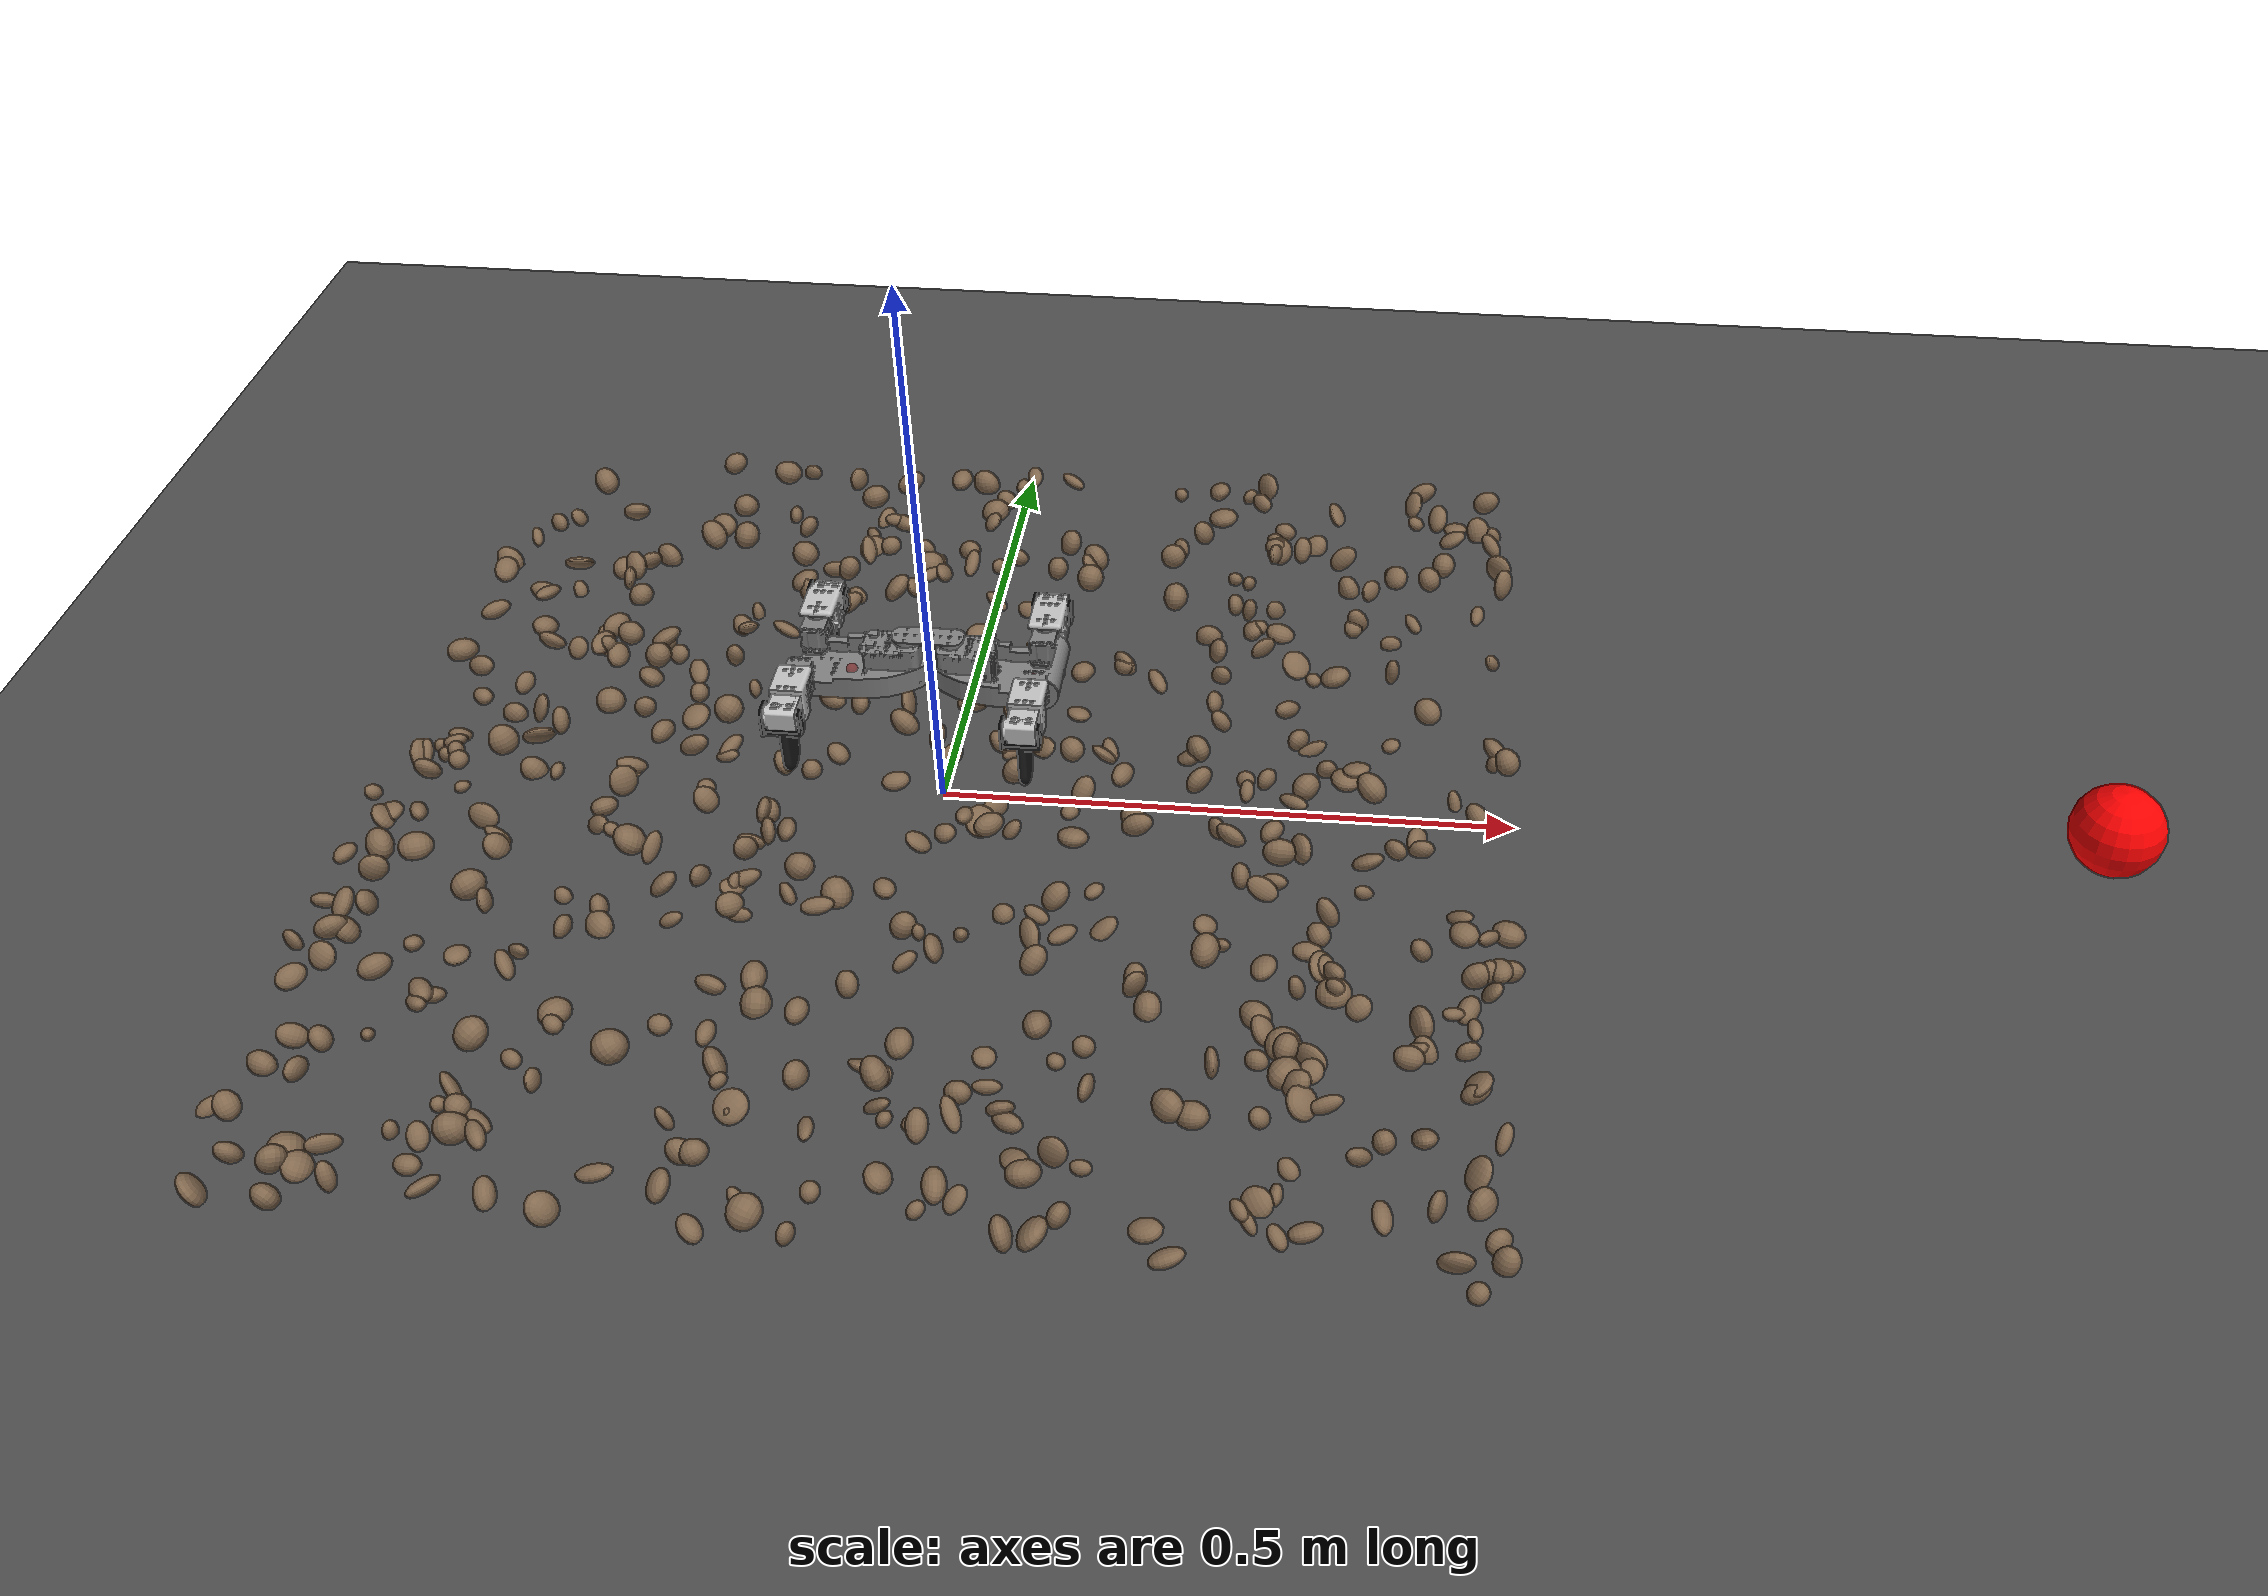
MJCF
<?xml version='1.0' encoding='utf-8'?>
<mujoco model="salamander_description">
  <include file="C:\Users\kevin\college_classes\SophomoreSpring\MiniRO\mujoco_box\assets\experiments\setup\../terrain_models\fixed_terrain.xml" /><compiler angle="radian" />
  <option solver="Newton" tolerance="1e-6" integrator="implicitfast" gravity="0 0 -9.81" />
  <include file="act2.xml" />

  <visual>
    <rgba haze="0.15 0.25 0.35 1" />
    <quality shadowsize="4096" />
    <map stiffness="700" shadowscale="0.5" fogstart="1" fogend="15" zfar="40" haze="1" />
  </visual>

  <asset>

    <texture type="skybox" builtin="gradient" rgb1="0.3 0.5 0.7" rgb2="0 0 0" width="512" height="512" />
    <texture name="texplane" type="2d" builtin="checker" rgb1=".2 .3 .4" rgb2=".1 0.15 0.2" width="512" height="512" mark="cross" markrgb=".8 .8 .8" />
    <material name="matplane" reflectance="0.3" texture="texplane" texrepeat="10 10" texuniform="true" />
    <material name="slope_mat" reflectance="0.3" rgba="1 1 0 .25" />

  <mesh file="C:\Users\kevin\college_classes\SophomoreSpring\MiniRO\mujoco_box\assets\experiments\setup\..\model_assets\salamander\meshes\body_front_link.STL" name="body_front_link" /><mesh file="C:\Users\kevin\college_classes\SophomoreSpring\MiniRO\mujoco_box\assets\experiments\setup\..\model_assets\salamander\meshes\body_rear_link.STL" name="body_rear_link" /><mesh file="C:\Users\kevin\college_classes\SophomoreSpring\MiniRO\mujoco_box\assets\experiments\setup\..\model_assets\salamander\meshes\dummy_base_link.STL" name="dummy_base_link" /><mesh file="C:\Users\kevin\college_classes\SophomoreSpring\MiniRO\mujoco_box\assets\experiments\setup\..\model_assets\salamander\meshes\leg1_link.STL" name="leg1_link" /><mesh file="C:\Users\kevin\college_classes\SophomoreSpring\MiniRO\mujoco_box\assets\experiments\setup\..\model_assets\salamander\meshes\leg2_link.STL" name="leg2_link" /><mesh file="C:\Users\kevin\college_classes\SophomoreSpring\MiniRO\mujoco_box\assets\experiments\setup\..\model_assets\salamander\meshes\leg3_link.STL" name="leg3_link" /><mesh file="C:\Users\kevin\college_classes\SophomoreSpring\MiniRO\mujoco_box\assets\experiments\setup\..\model_assets\salamander\meshes\leg4_link.STL" name="leg4_link" /><mesh file="C:\Users\kevin\college_classes\SophomoreSpring\MiniRO\mujoco_box\assets\experiments\setup\..\model_assets\salamander\meshes\shoulder1_link.STL" name="shoulder1_link" /><mesh file="C:\Users\kevin\college_classes\SophomoreSpring\MiniRO\mujoco_box\assets\experiments\setup\..\model_assets\salamander\meshes\shoulder2_link.STL" name="shoulder2_link" /><mesh file="C:\Users\kevin\college_classes\SophomoreSpring\MiniRO\mujoco_box\assets\experiments\setup\..\model_assets\salamander\meshes\shoulder3_link.STL" name="shoulder3_link" /><mesh file="C:\Users\kevin\college_classes\SophomoreSpring\MiniRO\mujoco_box\assets\experiments\setup\..\model_assets\salamander\meshes\shoulder4_link.STL" name="shoulder4_link" /></asset>

  <worldbody>
    <body name="ball" pos="1 0 .04">
      <geom type="sphere" size=".04" rgba="1 0 0 1" />
    </body>
    <light diffuse=".4 .4 .4" specular="0.1 0.1 0.1" pos="0 0 2.0" dir="0 0 -1" castshadow="false" />
    <light directional="true" diffuse=".8 .8 .8" specular="0.2 0.2 0.2" pos="0 0 4" dir="0 0 -1" />
    <geom name="ground" type="plane" size="0 0 1" pos="0 0 0" quat="1 0 0 0" material="matplane" condim="1" />

    <body name="body_rear_link" pos="0 0 0.0856">
      <geom pos="0 0 0.0856" quat="1 0 0 0" type="mesh" mesh="body_rear_link" />
      <joint name="fall" type="free" pos="0 0 0" axis="0 0 1" />
      <site name="torso_sensors" pos="-0.0682 0 .048" rgba="0.5 0 0 .5" />
      <body name="shoulder3_link" pos="-0.10533 0.043967 0.0784">
        <geom type="mesh" rgba="0.75294 0.75294 0.75294 1" mesh="shoulder3_link" />
        <inertial pos="-0.00035612 0.027895 -0.015524" quat="0.830241 0.554769 0.0182893 0.0509566" mass="0.022828" diaginertia="3.78438e-06 3.41587e-06 3.14145e-06" />
        <joint name="shoulder3_joint" type="hinge" pos="0 0 0" axis="0 0 1" range="-1.4 1.4" actuatorfrcrange="-0.39 0.39" frictionloss="0.1" />
        <body name="leg3_link" pos="-0.0174 0.041 -0.0164">
          <inertial pos="0.015303 -0.0075022 -0.031486" quat="0.991718 -0.121381 -0.0411625 0.00821591" mass="0.01174" diaginertia="4.05823e-06 3.86047e-06 1.0964e-06" />
          <joint name="leg3_joint" type="hinge" pos="0 0 0" axis="1 0 0" range="0 1.6" actuatorfrcrange="-0.39 0.39" frictionloss="0.1" />
          <geom type="mesh" rgba="0.10196 0.10196 0.10196 1" mesh="leg3_link" />
        </body>
      </body>
      <body name="shoulder4_link" pos="-0.10533 -0.044033 0.0784">
        <inertial pos="-0.00035261 -0.027895 -0.015524" quat="0.55469 0.830308 -0.0504036 -0.0191768" mass="0.022828" diaginertia="3.78439e-06 3.41596e-06 3.14135e-06" />
        <joint name="shoulder4_joint" type="hinge" pos="0 0 0" axis="0 0 1" range="-1.4 1.4" actuatorfrcrange="-0.39 0.39" frictionloss="0.1" />
        <geom type="mesh" rgba="0.75294 0.75294 0.75294 1" mesh="shoulder4_link" />
        <body name="leg4_link" pos="-0.0174 -0.041 -0.0164">
          <inertial pos="0.015303 0.0075097 -0.031486" quat="0.991713 0.121232 -0.0407594 -0.0121008" mass="0.01174" diaginertia="4.05702e-06 3.85955e-06 1.09592e-06" />
          <joint name="leg4_joint" type="hinge" pos="0 0 0" axis="1 0 0" range="-1.6 0" actuatorfrcrange="-0.39 0.39" frictionloss="0.1" />
          <geom type="mesh" rgba="0.10196 0.10196 0.10196 1" mesh="leg4_link" />
        </body>
      </body>
      <body name="body_front_link" pos="0.0185 0 0.0881">
        <site name="spinal_sensors" pos="-0.0182 0 0" rgba="0 0 0 .5" />
        <site name="front_sensors" pos="0.0682 0 -.04" rgba="0.5 0 0 .5" />
        <inertial pos="0.056805 2.3159e-05 -0.033606" quat="0.4638 0.4638 -0.53375 0.53375" mass="0.081874" diaginertia="3.73585e-05 2.58825e-05 1.9334e-05" />
        <joint name="spinal_joint" type="hinge" pos="0 0 0" axis="0 0 1" range="-1.5707 1.5707" actuatorfrcrange="-1.52 1.52" frictionloss="0.5" />
        <geom type="mesh" mesh="body_front_link" />
        <site name="tip_sensors" pos="0.09 0 -0.033" />
        <body name="shoulder1_link" pos="0.073327 0.044033 -0.0097">
          <inertial pos="-0.00035612 0.027895 -0.015524" quat="0.830241 0.554769 0.0182893 0.0509566" mass="0.022828" diaginertia="3.78438e-06 3.41587e-06 3.14145e-06" />
          <joint name="shoulder1_joint" type="hinge" pos="0 0 0" axis="0 0 1" range="-1.4 1.4" actuatorfrcrange="-0.39 0.39" frictionloss="0.1" />
          <geom type="mesh" rgba="0.75294 0.75294 0.75294 1" mesh="shoulder1_link" />
          <body name="leg1_link" pos="-0.0174 0.041 -0.0164">
            <inertial pos="0.015303 -0.0075022 -0.031486" quat="0.991718 -0.121381 -0.0411625 0.00821591" mass="0.01174" diaginertia="4.05823e-06 3.86047e-06 1.0964e-06" />
            <joint name="leg1_joint" type="hinge" pos="0 0 0" axis="1 0 0" range="0 1.6" actuatorfrcrange="-0.39 0.39" frictionloss="0.1" />
            <geom type="mesh" rgba="0.10196 0.10196 0.10196 1" mesh="leg1_link" />
          </body>
        </body>
        <body name="shoulder2_link" pos="0.073327 -0.043967 -0.0097">
          <inertial pos="-0.00035261 -0.027895 -0.015524" quat="0.55469 0.830308 -0.0504036 -0.0191768" mass="0.022828" diaginertia="3.78439e-06 3.41596e-06 3.14135e-06" />
          <joint name="shoulder2_joint" type="hinge" pos="0 0 0" axis="0 0 1" range="-1.4 1.4" actuatorfrcrange="-0.39 0.39" frictionloss="0.1" />
          <geom type="mesh" rgba="0.75294 0.75294 0.75294 1" mesh="shoulder2_link" />
          <body name="leg2_link" pos="-0.0174 -0.041 -0.0164">
            <inertial pos="0.015303 0.0075097 -0.031486" quat="0.991713 0.121232 -0.0407594 -0.0121008" mass="0.01174" diaginertia="4.05702e-06 3.85955e-06 1.09592e-06" />
            <joint name="leg2_joint" type="hinge" pos="0 0 0" axis="1 0 0" range="-1.6 0" actuatorfrcrange="-0.39 0.39" frictionloss="0.1" />
            <geom type="mesh" rgba="0.10196 0.10196 0.10196 1" mesh="leg2_link" />
          </body>
        </body>
      </body>
    </body>

  </worldbody>

  <sensor>
    <velocimeter name="velocity" site="tip_sensors" />
    <framequat name="spinal_quat" objtype="site" objname="spinal_sensors" reftype="body" refname="body_rear_link" />
    <gyro name="torso_angular_velocity" site="torso_sensors" />
    <velocimeter name="torso_velocity" site="torso_sensors" />
    <velocimeter name="front_velocity" site="front_sensors" />
  </sensor>
</mujoco>

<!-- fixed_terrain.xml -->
<mujoco model="rocky_terrain_scene">
    <compiler angle="radian" inertiafromgeom="true" />
    <option timestep="0.002" gravity="0 0 -9.81" />

    <worldbody>
        <light name="sunlight" pos="5 5 5" dir="-1 -1 -1" diffuse="1 1 1" specular="0.5 0.5 0.5"
            ambient="0.5 0.5 0.5" />

        <geom name="ground_plane" type="plane" size="50 50 0.1" rgba="0.3 0.3 0.3 1" />

        <body name="rocky_terrain_body">

            <geom name="rock1" type="ellipsoid"
                size="0.010635329534388465 0.01438497268166328 0.005914709779790252"
                pos="0.19766094696471626 -0.22830203840614738 0.012165606076402305"
                quat="0.32783077707404157 0.40384022101962697 0.13859230271326106 0.12973669919307032"
                rgba="0.5 0.4 0.3 1"
                friction="0.7076538686159093 0.006822938232096483 0.13898819962866898" />
            <geom name="rock2" type="ellipsoid"
                size="0.007549697196913122 0.006226975999176467 0.009902325620333798"
                pos="0.33364096705294966 -0.39726677178425895 0.0009356580722909386"
                quat="0.22152047504181566 0.5327339382001128 0.07792441060203474 0.1678211761560367"
                rgba="0.5 0.4 0.3 1"
                friction="0.5027348096229171 0.008166861743895849 0.2175676128429864" />
            <geom name="rock3" type="ellipsoid"
                size="0.009603010407880646 0.008018772851770982 0.006292896091625895"
                pos="-0.20657563549892854 -0.021198071883568148 0.008323692008858366"
                quat="0.41463230958369757 0.08695409240499098 0.04864640503899281 0.44976719297231854"
                rgba="0.5 0.4 0.3 1"
                friction="0.4634818558074052 0.0078275204567122 0.18419304534360814" />
            <geom name="rock4" type="ellipsoid"
                size="0.012854807629083267 0.007293470228937215 0.008262782673383304"
                pos="0.2887148159162285 0.3872261823801648 0.010448550860270054"
                quat="0.055083050881002564 0.41720708845566423 0.16833550711017176 0.3593743535531615"
                rgba="0.5 0.4 0.3 1"
                friction="0.4924647319452632 0.005341519932809004 0.2379988858267388" />
            <geom name="rock5" type="ellipsoid"
                size="0.007715462268432673 0.0069838281476833335 0.007476830804187965"
                pos="0.2567652341122689 0.2611299348356505 0.006102779294809925"
                quat="0.25117144134362274 0.25691217021030016 0.2566351983215148 0.23528119012456236"
                rgba="0.5 0.4 0.3 1"
                friction="0.654815431165773 0.003268720998159647 0.1699352009686685" />
            <geom name="rock6" type="ellipsoid"
                size="0.011614283001530872 0.009030121214860737 0.006862195047596255"
                pos="-0.02333878400759659 -0.13656125480532189 0.011534161002056202"
                quat="0.3483434195853974 0.006585834482556683 0.05586576446802133 0.5892049814640247"
                rgba="0.5 0.4 0.3 1"
                friction="0.6735344932218006 0.00722690779034822 0.28246089274797515" />
            <geom name="rock7" type="ellipsoid"
                size="0.010977013138227399 0.009887615031272489 0.007741650920848165"
                pos="-0.09643198615840864 0.10463589045498778 0.011777664844946852"
                quat="0.17973400371930512 0.22650209351633344 0.36798304031010287 0.2257808624542586"
                rgba="0.5 0.4 0.3 1"
                friction="0.7547369243881644 0.005194254972427546 0.20127816680936092" />
            <geom name="rock8" type="ellipsoid"
                size="0.009955922894802263 0.011719822000622108 0.008633897634852481"
                pos="0.4876884920742305 -0.18740863859739354 0.013239565602502664"
                quat="0.009308726538157848 0.8431050091413644 0.12095950158338654 0.02662676273709107"
                rgba="0.5 0.4 0.3 1"
                friction="0.4193142090841402 0.006232656378792862 0.15868697608355736" />
            <geom name="rock9" type="ellipsoid"
                size="0.009532427557680058 0.005276418878805391 0.009774427813825294"
                pos="-0.24912962716179965 -0.3671218782193859 0.005903951234031985"
                quat="0.016750985658835135 0.4859411742531373 0.4665415948409032 0.030766245247124343"
                rgba="0.5 0.4 0.3 1"
                friction="0.7147533748715074 0.0039851446821189875 0.2999422371516757" />
            <geom name="rock10" type="ellipsoid"
                size="0.014293391625170068 0.014249920675490853 0.012624215253232762"
                pos="-0.029737470910607744 0.4402961944849725 0.00016243618951769566"
                quat="0.1616227007911226 0.3609516336371201 0.39627113469578823 0.08115453087596912"
                rgba="0.5 0.4 0.3 1"
                friction="0.46829607877325563 0.004636004248869872 0.24148606458969715" />
            <geom name="rock11" type="ellipsoid"
                size="0.006381947097339432 0.007349540467864518 0.009042721808587072"
                pos="-0.26836126434628704 -0.3547447100340637 0.014101153203260292"
                quat="0.34351297160880434 0.2769556950774069 0.2889611144627638 0.09057021885102498"
                rgba="0.5 0.4 0.3 1"
                friction="0.5505567970428072 0.009166959110484742 0.2959861148115028" />
            <geom name="rock12" type="ellipsoid"
                size="0.01124128697120997 0.014267418743595588 0.013269710089145351"
                pos="-0.05458425505438591 -0.4796419270036447 0.009163655399797663"
                quat="0.29692040908178846 0.23400998522015407 0.3726247784752469 0.09644482722281059"
                rgba="0.5 0.4 0.3 1"
                friction="0.5687101113941729 0.008708191379441586 0.2874780375454394" />
            <geom name="rock13" type="ellipsoid"
                size="0.014460797859121112 0.013228223243312354 0.008123639162839428"
                pos="0.3510003146001497 0.04432370699385768 0.006253634868060097"
                quat="0.406605262382087 0.004776549842646252 0.06848673085184616 0.5201314569234207"
                rgba="0.5 0.4 0.3 1"
                friction="0.7825870480511765 0.0027095895864757795 0.11351634754626677" />
            <geom name="rock14" type="ellipsoid"
                size="0.0072577781523364615 0.01058246108978101 0.013947599149830438"
                pos="-0.18736346342838817 0.2794477740527913 0.008594168552321075"
                quat="0.04771043325103995 0.7272066730598803 0.21976575581050364 0.005317137878576072"
                rgba="0.5 0.4 0.3 1"
                friction="0.5690478013952535 0.004922945035198375 0.10626104090924052" />
            <geom name="rock15" type="ellipsoid"
                size="0.012120996950585683 0.011000784161331644 0.014823538200199503"
                pos="-0.30027632563290685 0.3577639884784609 0.011803356521964342"
                quat="0.2178398274317472 0.413537904284444 0.33305215414533323 0.03557011413847557"
                rgba="0.5 0.4 0.3 1"
                friction="0.5340569966233158 0.004893697537653676 0.126331269503663" />
            <geom name="rock16" type="ellipsoid"
                size="0.007680447567727041 0.010559118107941138 0.010661329520815171"
                pos="-0.2556475907981901 -0.17575032735823992 0.006807513654503314"
                quat="0.4088586422875096 0.44647359645633256 0.07116770222791279 0.07350005902824505"
                rgba="0.5 0.4 0.3 1"
                friction="0.4316846750729744 0.009240774052107489 0.27174943110715266" />
            <geom name="rock17" type="ellipsoid"
                size="0.005575263139917338 0.012746615665994034 0.010289095113995022"
                pos="0.26244053942735035 0.2309947412808422 0.0043840155170704635"
                quat="0.025764508660620574 0.2828416320590243 0.5397454590405636 0.15164840023979162"
                rgba="0.5 0.4 0.3 1"
                friction="0.6864599186939695 0.0020414758736039917 0.16609741305359643" />
            <geom name="rock18" type="ellipsoid"
                size="0.013361827062769192 0.0104971944041302 0.005547873148985555"
                pos="0.17471389678620564 -0.339331268347533 0.010738312288697812"
                quat="0.29529889778136537 0.2342087790665241 0.3027633896861161 0.16772893346599438"
                rgba="0.5 0.4 0.3 1"
                friction="0.7033220298932086 0.0038737169498997983 0.20796202999654134" />
            <geom name="rock19" type="ellipsoid"
                size="0.013776731525366022 0.006668647673593635 0.007602836416243437"
                pos="-0.19963263614807036 0.0365641944018289 0.008382345683458416"
                quat="0.35629652958584634 0.3029776846924261 0.08021166906889612 0.26051411665283136"
                rgba="0.5 0.4 0.3 1"
                friction="0.5413647775124508 0.009072709551698997 0.10546895307319613" />
            <geom name="rock20" type="ellipsoid"
                size="0.011102348208966797 0.0069643440410306 0.006683734143794725"
                pos="0.47793614439569176 0.4419144728016279 0.0012340035726950555"
                quat="0.5063837680644659 0.08691961922515726 0.38837915103159776 0.018317461678778926"
                rgba="0.5 0.4 0.3 1"
                friction="0.578504196410084 0.006831846133837 0.16563638706373646" />
            <geom name="rock21" type="ellipsoid"
                size="0.008921212396922465 0.014874075767500314 0.006064796229907665"
                pos="0.16271563048486493 -0.15818014403032332 0.0005563617064012943"
                quat="0.0629071330794635 0.27643627211247984 0.48222279084470115 0.1784338039633556"
                rgba="0.5 0.4 0.3 1"
                friction="0.5770218613215083 0.008968545299155448 0.16521143601145633" />
            <geom name="rock22" type="ellipsoid"
                size="0.010517007631809551 0.010892438487094995 0.006899004626633606"
                pos="-0.2808413948628985 -0.19665711935292596 0.0014022420213835928"
                quat="0.2559213068046039 0.2582845257543398 0.3071697367739514 0.17862443066710496"
                rgba="0.5 0.4 0.3 1"
                friction="0.6731192077260053 0.004014310646700165 0.2542201181916631" />
            <geom name="rock23" type="ellipsoid"
                size="0.012870218778722374 0.014462030841680976 0.007444252013808995"
                pos="-0.3002149623315975 0.18426492385478999 0.012987926743563576"
                quat="0.1791645663328773 0.30642511197959044 0.4952581767327347 0.01915214495479748"
                rgba="0.5 0.4 0.3 1"
                friction="0.5779815900619631 0.0015720922581403606 0.12479028227791918" />
            <geom name="rock24" type="ellipsoid"
                size="0.01024202364174998 0.010835445099620615 0.013504670233171853"
                pos="-0.36862132623364896 -0.002881885642289972 0.0011240596768769344"
                quat="0.12717378541575844 0.2395964448945419 0.5164103699936684 0.11681939969603114"
                rgba="0.5 0.4 0.3 1"
                friction="0.6914290685961348 0.009053094273956633 0.13182311863722507" />
            <geom name="rock25" type="ellipsoid"
                size="0.011519137183173789 0.008604376045421207 0.013183257870092769"
                pos="-0.3665502867395003 -0.10805189591633724 0.0038673893460688473"
                quat="0.032521074951472495 0.4157738598792641 0.36002924044544343 0.19167582472381997"
                rgba="0.5 0.4 0.3 1"
                friction="0.5256403470713129 0.0015080425753439043 0.10109549174855213" />
            <geom name="rock26" type="ellipsoid"
                size="0.0076796915702895315 0.010792962789720638 0.009443654233925522"
                pos="-0.29258977036590916 0.08576958120044664 0.0078065411023144115"
                quat="0.1464559444642473 0.31400696846861953 0.3145045338016125 0.22503255326552074"
                rgba="0.5 0.4 0.3 1"
                friction="0.5108455308760047 0.007009526837335931 0.15239563904476888" />
            <geom name="rock27" type="ellipsoid"
                size="0.013425997098950159 0.010742351114952784 0.005504678270688479"
                pos="0.39591380603304194 0.47449225705146525 0.012849279268282592"
                quat="0.030908285669959342 0.40862856199198716 0.29360631233893636 0.2668568399991171"
                rgba="0.5 0.4 0.3 1"
                friction="0.617272728056405 0.007166301957945798 0.276953493645385" />
            <geom name="rock28" type="ellipsoid"
                size="0.009185573336548004 0.005255670613888069 0.009430818744333564"
                pos="0.0902729375873702 -0.3079876734749242 0.0020778653830799266"
                quat="0.18606874496064704 0.29697776771292284 0.2418168838678753 0.27513660345855473"
                rgba="0.5 0.4 0.3 1"
                friction="0.7062228628037625 0.004204488524668141 0.28419348427304203" />
            <geom name="rock29" type="ellipsoid"
                size="0.011904390708677015 0.011440306831211822 0.013563658260025539"
                pos="-0.2518736940916979 0.47241558733913613 0.014376274178832825"
                quat="0.18004268255405848 0.19237177215508652 0.40252445379564344 0.22506109149521153"
                rgba="0.5 0.4 0.3 1"
                friction="0.5811254653877672 0.005807995377614454 0.29323940856238695" />
            <geom name="rock30" type="ellipsoid"
                size="0.006394698519760548 0.014746918580490952 0.009814086775353685"
                pos="0.3299111052543432 0.37401931849737546 0.012078518033792172"
                quat="0.20037223212312347 0.3359344651009194 0.36283611241174585 0.10085719036421133"
                rgba="0.5 0.4 0.3 1"
                friction="0.6967720610173918 0.0032744072005662476 0.22620095241466234" />
            <geom name="rock31" type="ellipsoid"
                size="0.009156213066346085 0.006617798951001 0.007868241371878706"
                pos="-0.3965275037032493 -0.22645921979437378 0.0011009392212919821"
                quat="0.2945648120089726 0.1434962930315848 0.34708084074469026 0.2148580542147523"
                rgba="0.5 0.4 0.3 1"
                friction="0.6276284477589492 0.007988793543086748 0.2564738333705957" />
            <geom name="rock32" type="ellipsoid"
                size="0.010617553931104518 0.005915208343649915 0.006763398881685397"
                pos="0.3307028295878055 -0.46713181441807816 0.009403794060148438"
                quat="0.026403788408503107 0.2683009879615 0.35992482686372 0.34537039676627684"
                rgba="0.5 0.4 0.3 1"
                friction="0.7142518131021358 0.005030345997729791 0.1393383751822796" />
            <geom name="rock33" type="ellipsoid"
                size="0.011213522661415187 0.010871406413662512 0.01269834442000536"
                pos="0.4925817918299654 0.08027345767098537 0.007709164729953285"
                quat="0.12327328712470961 0.35283405308607996 0.4827433036523363 0.041149356136874114"
                rgba="0.5 0.4 0.3 1"
                friction="0.6995740191814072 0.001689182728590915 0.1847814713137224" />
            <geom name="rock34" type="ellipsoid"
                size="0.00557642864696167 0.008364075043674531 0.012474018761234584"
                pos="-0.16713453466142525 0.31664266007440345 0.007273812483298124"
                quat="0.2293881178463558 0.21460384371186553 0.2857864503150674 0.27022158812671127"
                rgba="0.5 0.4 0.3 1"
                friction="0.6352472491092311 0.008717069804012184 0.23633504101200167" />
            <geom name="rock35" type="ellipsoid"
                size="0.014690276086754848 0.011132926536374675 0.013042352823352556"
                pos="-0.49131965353679974 0.15949251909480444 0.002895335340210999"
                quat="0.46688397378587837 0.23902680400210174 0.14224169134541811 0.15184753086660185"
                rgba="0.5 0.4 0.3 1"
                friction="0.5020876065821018 0.004886291284807146 0.16443531625976565" />
            <geom name="rock36" type="ellipsoid"
                size="0.011826091492063713 0.011206643553719477 0.008277626501929163"
                pos="-0.2877018308168885 -0.054359223600780715 0.009108616585693738"
                quat="0.18520895035848767 0.580212236002436 0.17807077270474722 0.05650804093432906"
                rgba="0.5 0.4 0.3 1"
                friction="0.4750780449056 0.0012657020416025672 0.12340592630645318" />
            <geom name="rock37" type="ellipsoid"
                size="0.01112234115383743 0.013872136544472693 0.0052659616544141995"
                pos="-0.01785641856446918 0.06760184762241772 0.008661169602427616"
                quat="0.2462814100128935 0.34672110960909414 0.1614316315727399 0.24556584880527244"
                rgba="0.5 0.4 0.3 1"
                friction="0.6406975565676961 0.006651770321092676 0.28154177244747897" />
            <geom name="rock38" type="ellipsoid"
                size="0.011984495410634328 0.006298971102636726 0.011510650362019384"
                pos="-0.47517857224014637 -0.07070907472105226 0.0014685670290363179"
                quat="0.319542812528416 0.3158775351627749 0.14891535499133526 0.21566429731747386"
                rgba="0.5 0.4 0.3 1"
                friction="0.7279886363465319 0.007564154841307717 0.1355410839922323" />
            <geom name="rock39" type="ellipsoid"
                size="0.008226001775791667 0.008990923985619965 0.01495228424573472"
                pos="-0.11937446823067 0.41118461872183676 0.0009017374371750585"
                quat="0.2851223111032205 0.3824526456257841 0.01209216253381579 0.32033288073717964"
                rgba="0.5 0.4 0.3 1"
                friction="0.5532769206434742 0.006226296972110461 0.133517696142669" />
            <geom name="rock40" type="ellipsoid"
                size="0.014885634430326745 0.010210032980912774 0.005184714856407897"
                pos="0.07723371113870636 0.06815306760336937 0.002142282444437314"
                quat="0.16875448499850804 0.11057261858010872 0.5409919255444824 0.17968097087690083"
                rgba="0.5 0.4 0.3 1"
                friction="0.6068481326517825 0.00832556953239741 0.1895145292924651" />
            <geom name="rock41" type="ellipsoid"
                size="0.0064603383378330605 0.005184905791048759 0.01455876737849749"
                pos="0.020694060581435747 -0.3745301425847074 0.013076572954453252"
                quat="0.42361179677955807 0.1786205029985936 0.148029178073594 0.2497385221482542"
                rgba="0.5 0.4 0.3 1"
                friction="0.5172188311296421 0.002097916844056372 0.15332507802873205" />
            <geom name="rock42" type="ellipsoid"
                size="0.007643165692609786 0.005572414696326414 0.012959834974825397"
                pos="0.044413427779711245 0.4859297816680582 0.012579448241024976"
                quat="0.3145007226078227 0.29174920572979735 0.3159671366563601 0.07778293500601995"
                rgba="0.5 0.4 0.3 1"
                friction="0.405360087144899 0.006611311618474905 0.15324874365865154" />
            <geom name="rock43" type="ellipsoid"
                size="0.008657119527781223 0.0077584797665317925 0.005914585178755339"
                pos="-0.06625310798948403 -0.1407286018466083 0.0011596457555716727"
                quat="0.16851475901005233 0.38635614487422654 0.18268242636058812 0.2624466697551331"
                rgba="0.5 0.4 0.3 1"
                friction="0.7177727029821392 0.004720476745757457 0.16900740087196547" />
            <geom name="rock44" type="ellipsoid"
                size="0.01455461524457152 0.010599145335146734 0.007311888107082453"
                pos="-0.4684203637438219 -0.19164722931729783 0.006707695389041487"
                quat="0.031797415430321045 0.42981314645439583 0.29952090441921847 0.23886853369606462"
                rgba="0.5 0.4 0.3 1"
                friction="0.4239791922903247 0.004984597101544218 0.2699451649073482" />
            <geom name="rock45" type="ellipsoid"
                size="0.005350666700525521 0.0071733900410206435 0.008387001268897756"
                pos="0.3572575981377244 -0.21860074068846969 0.014260209426438485"
                quat="0.34283434606126667 0.2857219424979967 0.17286026655391531 0.19858344488682128"
                rgba="0.5 0.4 0.3 1"
                friction="0.6209645522559241 0.003094516141741547 0.1770251595883132" />
            <geom name="rock46" type="ellipsoid"
                size="0.005366913290318794 0.014230097059943169 0.013834391053395106"
                pos="0.29579852634500603 0.20210207798360935 0.008743439167193466"
                quat="0.3144183361225534 0.06276764949571233 0.492892036563736 0.12992197781799833"
                rgba="0.5 0.4 0.3 1"
                friction="0.7369294981294361 0.007820681068120047 0.19861863930630025" />
            <geom name="rock47" type="ellipsoid"
                size="0.010207003241372935 0.005927196026703662 0.00514738436406678"
                pos="0.46839660987215315 -0.25225254722889645 0.011314350893703721"
                quat="0.030998121365185982 0.41096686957266276 0.45821997390703423 0.09981503515511707"
                rgba="0.5 0.4 0.3 1"
                friction="0.4351191758187654 0.0012838025764967448 0.21079956260975413" />
            <geom name="rock48" type="ellipsoid"
                size="0.013101869258214868 0.009074265436733647 0.01421057504223434"
                pos="-0.4634387978202389 -0.22568475691848477 0.013119610493934475"
                quat="0.44429311903997615 0.06627129082948985 0.28886867717779324 0.20056691295274082"
                rgba="0.5 0.4 0.3 1"
                friction="0.45120058999694534 0.0027331974699360715 0.27374171647080936" />
            <geom name="rock49" type="ellipsoid"
                size="0.013034938310991232 0.005258170329987263 0.005727248481770709"
                pos="0.04821469085982377 0.21530717653577225 0.002795291783205494"
                quat="0.15756090432569625 0.1226983183478749 0.4725187939830657 0.24722198334336318"
                rgba="0.5 0.4 0.3 1"
                friction="0.506091527159843 0.005252553871434728 0.10033290785287008" />
            <geom name="rock50" type="ellipsoid"
                size="0.013256260501935579 0.007347689086876403 0.005870882439389129"
                pos="-0.008711377147619048 0.48580220338353575 0.003659770907579889"
                quat="0.22295581676584184 0.29399519996583157 0.36076387872333965 0.1222851045449869"
                rgba="0.5 0.4 0.3 1"
                friction="0.4827967977000979 0.00240570635363345 0.20999568634750285" />
            <geom name="rock51" type="ellipsoid"
                size="0.00762142575432081 0.009382404829673032 0.009047207639013195"
                pos="0.07768333536639938 -0.14706442274377796 0.0003550195056789562"
                quat="0.2765301282792697 0.33913785580664235 0.366557404078303 0.017774611835784944"
                rgba="0.5 0.4 0.3 1"
                friction="0.4599834417658132 0.0011645773632526606 0.2751783234212062" />
            <geom name="rock52" type="ellipsoid"
                size="0.011500642337377265 0.012983601623257832 0.00879949885070994"
                pos="-0.4038761787688122 -0.4992755935759715 0.01013918479198239"
                quat="0.005825748496569551 0.15552207833083745 0.33352910809687053 0.5051230650757225"
                rgba="0.5 0.4 0.3 1"
                friction="0.6589439381155349 0.00409779216917187 0.2952669232041669" />
            <geom name="rock53" type="ellipsoid"
                size="0.0148471127050917 0.012581146093681165 0.005824391768869848"
                pos="0.3427773761935763 -0.28796728186627363 0.005077350161773937"
                quat="0.09390822536469821 0.12228038105450606 0.41174291011407665 0.372068483466719"
                rgba="0.5 0.4 0.3 1"
                friction="0.7931808025395529 0.0042923456652988095 0.14383500285313916" />
            <geom name="rock54" type="ellipsoid"
                size="0.006754799038946666 0.007938782648718834 0.011456840584607749"
                pos="0.29869280757900774 -0.09043512438097312 0.004348817074242448"
                quat="0.24193307842950543 0.3068579600749786 0.1430069114897169 0.3082020500057991"
                rgba="0.5 0.4 0.3 1"
                friction="0.5007841277674117 0.004127780176308431 0.11592951021656615" />
            <geom name="rock55" type="ellipsoid"
                size="0.012065726599963515 0.006616370360615163 0.014231325345428602"
                pos="-0.3893895373964408 -0.07361519760688606 0.006151946530910899"
                quat="0.11692333835208472 0.46862520691771564 0.020328102133087826 0.3941233525971118"
                rgba="0.5 0.4 0.3 1"
                friction="0.6859732290686102 0.005870859186907741 0.22886546451840475" />
            <geom name="rock56" type="ellipsoid"
                size="0.008295196104584422 0.007218681569250038 0.007909447264268371"
                pos="-0.010591790887010233 -0.4594067638217365 0.01206012875520725"
                quat="0.2933095872914488 0.27014704264555756 0.047775881244692966 0.38876748881830075"
                rgba="0.5 0.4 0.3 1"
                friction="0.6041309808026193 0.00825703794840309 0.2325523956564851" />
            <geom name="rock57" type="ellipsoid"
                size="0.005181937838211058 0.014646095741008069 0.0074453205251466545"
                pos="-0.2302449711012884 -0.10629512948270448 0.012693165391620426"
                quat="0.17371176592571758 0.15738841359634814 0.4787678623366357 0.19013195814129852"
                rgba="0.5 0.4 0.3 1"
                friction="0.5130534548726982 0.009963385571826976 0.2051184025796427" />
            <geom name="rock58" type="ellipsoid"
                size="0.0056443489214675615 0.013136517894664482 0.007645303206823083"
                pos="0.002294415416852047 0.49801665764255254 0.007499043828571462"
                quat="0.49498351998473855 0.027320376789058097 0.3836155016663536 0.09408060155984982"
                rgba="0.5 0.4 0.3 1"
                friction="0.45020449852442146 0.0024009850089982895 0.11197813142135232" />
            <geom name="rock59" type="ellipsoid"
                size="0.0066539399952247665 0.00849547324679847 0.007812371579412397"
                pos="-0.2923742092265903 -0.15959499809814448 5.76469371656102e-05"
                quat="0.37402585325869125 0.2201609566527733 0.18108888062776293 0.2247243094607726"
                rgba="0.5 0.4 0.3 1"
                friction="0.7752240700062696 0.007836832775918793 0.1488668521598145" />
            <geom name="rock60" type="ellipsoid"
                size="0.010075856599987672 0.007645877401999664 0.010817009086843889"
                pos="0.006812807834924772 0.35781317992865425 0.0037193829533901154"
                quat="0.28466692569783897 0.10584670741672209 0.5160740979043337 0.09341226898110518"
                rgba="0.5 0.4 0.3 1"
                friction="0.4568985987310234 0.008818838702174096 0.26110404338265136" />
            <geom name="rock61" type="ellipsoid"
                size="0.01008751517341219 0.008864549864868 0.010238248829402479"
                pos="0.26968893359915813 0.4123560218071116 0.013619594868294208"
                quat="0.258842199473387 0.17519269481816685 0.41350333069996464 0.15246177500848151"
                rgba="0.5 0.4 0.3 1"
                friction="0.5511490104001313 0.007761583801214687 0.281775055351109" />
            <geom name="rock62" type="ellipsoid"
                size="0.013097353708900236 0.007680118992183424 0.008593377313055504"
                pos="0.11934112880757808 -0.37242753797334627 0.003106695195396104"
                quat="0.06777348294877385 0.13362631312407922 0.6212254475932076 0.17737475633393932"
                rgba="0.5 0.4 0.3 1"
                friction="0.7892112937581783 0.001287956947496595 0.17889414201877643" />
            <geom name="rock63" type="ellipsoid"
                size="0.006830639410635336 0.008150535087926356 0.006470836911297682"
                pos="-0.4942780957673667 -0.05529475302610376 0.009763232990708743"
                quat="0.27545602635095057 0.25310067133378306 0.06566436579628039 0.40577893651898606"
                rgba="0.5 0.4 0.3 1"
                friction="0.5669718303872006 0.0015761994504777071 0.2837018089792011" />
            <geom name="rock64" type="ellipsoid"
                size="0.010056404868182756 0.011991126155934347 0.007806893034979409"
                pos="0.17151816820315857 -0.460811160525058 0.008170193738148993"
                quat="0.24204876156996433 0.3642086157228912 0.2106558716731835 0.18308675103396088"
                rgba="0.5 0.4 0.3 1"
                friction="0.5131787913374487 0.008719107930987326 0.1678199130853836" />
            <geom name="rock65" type="ellipsoid"
                size="0.011307065551344593 0.006627046535902214 0.006224904430745947"
                pos="0.010925865806751589 -0.22104065180492793 0.012669177015575706"
                quat="0.32794049998164226 0.41451819845107835 0.05321007580943524 0.2043312257578442"
                rgba="0.5 0.4 0.3 1"
                friction="0.6523862378340526 0.00329176845636895 0.1367721281329318" />
            <geom name="rock66" type="ellipsoid"
                size="0.012803759507855283 0.014892186495095106 0.011141778794113495"
                pos="0.37441256885764895 0.02975075153417117 0.011416915616382665"
                quat="0.38492332875578317 0.05987730761758126 0.24770985164678597 0.30748951197984964"
                rgba="0.5 0.4 0.3 1"
                friction="0.46868901830321286 0.0029860517394307783 0.14714732059896368" />
            <geom name="rock67" type="ellipsoid"
                size="0.006184255186366371 0.00928165344288951 0.005935692411430489"
                pos="-0.34100159608163183 -0.42311266618662813 0.00183841568340458"
                quat="0.30165101492265384 0.29540287249963343 0.22788339838170385 0.175062714196009"
                rgba="0.5 0.4 0.3 1"
                friction="0.5832214781667332 0.004918836638645289 0.260852161151642" />
            <geom name="rock68" type="ellipsoid"
                size="0.013686549945075725 0.009138368104365371 0.012233654283506002"
                pos="-0.2515337506277029 -0.1919056104284783 0.000773292359591709"
                quat="0.1809028208973029 0.14101977348361788 0.15705803990393652 0.5210193657151427"
                rgba="0.5 0.4 0.3 1"
                friction="0.5510121022821157 0.007810524900581679 0.19891080038091477" />
            <geom name="rock69" type="ellipsoid"
                size="0.005153065306273242 0.010281234881019112 0.006359804152094601"
                pos="0.48056197315462346 0.08116365561308703 0.0026140267885376134"
                quat="0.30159216352794327 0.37169397578681945 0.19026210493251008 0.13645175575272717"
                rgba="0.5 0.4 0.3 1"
                friction="0.7628090555006327 0.00423734920928074 0.22514303884005923" />
            <geom name="rock70" type="ellipsoid"
                size="0.009421519562130616 0.011549585069407618 0.012890284394938268"
                pos="-0.46534239791828136 -0.36620490923190385 0.00082464570449085"
                quat="0.2984669137556468 0.29912482011325736 0.19860635013030614 0.20380191600078965"
                rgba="0.5 0.4 0.3 1"
                friction="0.4521269426610611 0.0043516253601120205 0.1730839086956295" />
            <geom name="rock71" type="ellipsoid"
                size="0.011625948818682959 0.013560218478246466 0.008411789791558256"
                pos="0.22273094400392646 0.027227363848495556 0.010773669783798623"
                quat="0.3288178435856135 0.30782669353239905 0.34573203036884165 0.01762343251314583"
                rgba="0.5 0.4 0.3 1"
                friction="0.4631482221106227 0.007854863506571021 0.22329751523999025" />
            <geom name="rock72" type="ellipsoid"
                size="0.009296820023066595 0.006215450300200353 0.011432563359438347"
                pos="-0.4871266480857124 -0.186195656019414 0.003576082276849962"
                quat="0.36330973708630027 0.14145972680477037 0.35885784119098346 0.13637269491794587"
                rgba="0.5 0.4 0.3 1"
                friction="0.4647660035051844 0.00816736356823513 0.20646629267960268" />
            <geom name="rock73" type="ellipsoid"
                size="0.012520966869770462 0.01405868526201319 0.008526414712668889"
                pos="-0.2010375009213673 -0.4903873940958148 0.008925823969929185"
                quat="0.38633702475720677 0.2502960642454319 0.09097574942598283 0.2723911615713785"
                rgba="0.5 0.4 0.3 1"
                friction="0.5728399257845807 0.005217927916021099 0.15693146568093627" />
            <geom name="rock74" type="ellipsoid"
                size="0.010030406757535141 0.011244601453753349 0.00747011192124618"
                pos="-0.20958745408811652 0.38084104321073387 0.011335546889630638"
                quat="0.24325953726241273 0.3187056713502825 0.30308275370678905 0.13495203768051564"
                rgba="0.5 0.4 0.3 1"
                friction="0.4199715237406218 0.00883239372024815 0.29068320253150903" />
            <geom name="rock75" type="ellipsoid"
                size="0.007132002459024262 0.00910005723733568 0.013890103989543174"
                pos="0.3494748786064549 0.26997548024791396 0.013824231688253266"
                quat="0.04100061874293287 0.40056589336021603 0.45277564343331717 0.105657844463534"
                rgba="0.5 0.4 0.3 1"
                friction="0.41328012623099464 0.0011096288194980656 0.27084034203950724" />
            <geom name="rock76" type="ellipsoid"
                size="0.01417855917904641 0.006344986113823441 0.007656962168370085"
                pos="-0.07562954931143484 -0.1583804033850551 0.007583367324246335"
                quat="0.3547510903200933 0.5428425464953768 0.040338331398420135 0.06206803178610975"
                rgba="0.5 0.4 0.3 1"
                friction="0.5198154076681892 0.007875908425744236 0.2389436733070633" />
            <geom name="rock77" type="ellipsoid"
                size="0.011742974142101542 0.014468756593490721 0.01124561238480684"
                pos="-0.43907890176946685 0.4482898330943528 0.008229259860864572"
                quat="0.44166886874096245 0.005436495537048008 0.3410073239552188 0.21188731176677075"
                rgba="0.5 0.4 0.3 1"
                friction="0.62517809838465 0.0023928095528952 0.12167772934103699" />
            <geom name="rock78" type="ellipsoid"
                size="0.005530871566907626 0.011074160606398143 0.008689726381233595"
                pos="0.2694336249398186 0.2924007321304548 0.0038754289525693006"
                quat="0.22304614992452518 0.09850487769002503 0.27195566067326943 0.40649331171218045"
                rgba="0.5 0.4 0.3 1"
                friction="0.5098957641065099 0.0056443880597421905 0.18180070512259905" />
            <geom name="rock79" type="ellipsoid"
                size="0.014819405836732455 0.01042100485104494 0.010126806405091202"
                pos="-0.10718973704825108 -0.24493849276057922 0.008578115311242368"
                quat="0.2581401448834238 0.21774741639095868 0.2186440840220828 0.3054683547035346"
                rgba="0.5 0.4 0.3 1"
                friction="0.7593608806799773 0.007548843449662405 0.13074990772420528" />
            <geom name="rock80" type="ellipsoid"
                size="0.006158781242617396 0.008437359230975768 0.010116784347364276"
                pos="0.38223223259080696 0.25335360074308555 0.0006428779533091489"
                quat="0.19311695599118572 0.24281847912221816 0.31815077198661396 0.2459137928999821"
                rgba="0.5 0.4 0.3 1"
                friction="0.7558423054443726 0.009893576042457226 0.239051904696196" />
            <geom name="rock81" type="ellipsoid"
                size="0.014736406825440633 0.00576870149953996 0.006894467351689725"
                pos="0.07666005003429621 -0.37338763866475855 0.008385513322398716"
                quat="0.05829232538447641 0.29708235393959986 0.2766651299203593 0.3679601907555644"
                rgba="0.5 0.4 0.3 1"
                friction="0.7132877114762834 0.0013174191087625363 0.19191676274012898" />
            <geom name="rock82" type="ellipsoid"
                size="0.0050247038014514835 0.010726347359164178 0.008960077869393894"
                pos="-0.3794339536362642 0.16386978872627977 0.010088422255027263"
                quat="0.2960909584671623 0.22279496783254452 0.3419181934339639 0.13919588026632929"
                rgba="0.5 0.4 0.3 1"
                friction="0.7060184910889996 0.002187228842121417 0.15810601850608458" />
            <geom name="rock83" type="ellipsoid"
                size="0.008631911743633884 0.006146905046088048 0.01158326824188742"
                pos="-0.3126478438907968 -0.43549321765367643 0.012446744078610582"
                quat="0.2646692465904815 0.5885832208364897 0.0863434844783145 0.06040404809471422"
                rgba="0.5 0.4 0.3 1"
                friction="0.634062157725772 0.005702071666216927 0.2643501730360973" />
            <geom name="rock84" type="ellipsoid"
                size="0.008685812700961103 0.012141475641744892 0.01018430570171586"
                pos="-0.4658943156707738 -0.420959261979695 0.01440325999842076"
                quat="0.3217693723931414 0.04085912555406994 0.362775622531316 0.2745958795214725"
                rgba="0.5 0.4 0.3 1"
                friction="0.7717013668845255 0.0029727573672926385 0.2770684893308621" />
            <geom name="rock85" type="ellipsoid"
                size="0.009567613951136231 0.0065253033799974524 0.013491973485960183"
                pos="0.4369454650949943 0.4272534469310052 0.004881148534657617"
                quat="0.28038693147483656 0.1578627705741993 0.2269649526817358 0.3347853452692284"
                rgba="0.5 0.4 0.3 1"
                friction="0.5562103567547334 0.0033491875101076722 0.2561477686789149" />
            <geom name="rock86" type="ellipsoid"
                size="0.0063551686401660465 0.009592880117819004 0.005626564340044548"
                pos="0.25917167553703635 0.40348554957579597 0.01056299823864352"
                quat="0.17407225298298162 0.539216075666716 0.21228463038575848 0.07442704096454396"
                rgba="0.5 0.4 0.3 1"
                friction="0.6225186856052568 0.004567858771831015 0.13611724154595273" />
            <geom name="rock87" type="ellipsoid"
                size="0.01012010386394982 0.00874802648481353 0.010948566077827312"
                pos="0.07851910671546913 -0.3531607437317046 0.010597895191151655"
                quat="0.5471816900400157 0.1058599363932226 0.3439795352258812 0.002978838340880402"
                rgba="0.5 0.4 0.3 1"
                friction="0.768511428880252 0.00458340956881447 0.2956016455186533" />
            <geom name="rock88" type="ellipsoid"
                size="0.01360812389626228 0.013036234341046945 0.0068128950457109"
                pos="0.31874761390302075 -0.05547855807673119 0.01154024973127025"
                quat="0.2281053218669356 0.11672724714401228 0.40618873618441886 0.24897869480463325"
                rgba="0.5 0.4 0.3 1"
                friction="0.4332449769342299 0.0035302440041795136 0.2558110989567759" />
            <geom name="rock89" type="ellipsoid"
                size="0.010856589848229268 0.010592765842870245 0.009345564596660251"
                pos="0.34018176626140684 -0.15446583024920058 0.008275618107469115"
                quat="0.28396731177326306 0.14152401702600292 0.2262737338611138 0.34823493733962024"
                rgba="0.5 0.4 0.3 1"
                friction="0.7409910130139958 0.0013011271378024815 0.20370158552745588" />
            <geom name="rock90" type="ellipsoid"
                size="0.00723202161830257 0.007966054137081449 0.011679975235061016"
                pos="0.23470948360757582 0.10640219930204575 0.014347848073149998"
                quat="0.002792192100961826 0.6795169449120234 0.11243928708395584 0.20525157590305879"
                rgba="0.5 0.4 0.3 1"
                friction="0.42543578615445204 0.0017426114172844128 0.29085785468347863" />
            <geom name="rock91" type="ellipsoid"
                size="0.0076206831443344555 0.007596408620228938 0.005723321251248304"
                pos="-0.007408551546354114 0.3354755352408959 0.007826526326382643"
                quat="0.4351204416672874 0.28640968349510304 0.24497453233149044 0.03349534250611911"
                rgba="0.5 0.4 0.3 1"
                friction="0.532191669825983 0.008532208033089015 0.144770175764809" />
            <geom name="rock92" type="ellipsoid"
                size="0.00941450849418731 0.005520098588643714 0.005924689835261645"
                pos="0.30148784619810787 -0.4487547245048732 0.014086871540471314"
                quat="0.24533394109869736 0.13565001406223334 0.07599879627140915 0.5430172485676601"
                rgba="0.5 0.4 0.3 1"
                friction="0.7873489994339273 0.0031093304632736525 0.29649399057075243" />
            <geom name="rock93" type="ellipsoid"
                size="0.007483895123514325 0.012221826896335636 0.005685058330761404"
                pos="0.01666223856711735 -0.33688736927492446 0.0025232440950260504"
                quat="0.09718933614282656 0.2518606517217161 0.3731180995537572 0.27783191258170015"
                rgba="0.5 0.4 0.3 1"
                friction="0.7517151987760543 0.009076476074649228 0.10760284670250037" />
            <geom name="rock94" type="ellipsoid"
                size="0.011120872722936718 0.010970316025033688 0.012050373789282677"
                pos="-0.337807464683322 0.19353288529510526 0.008610499219221074"
                quat="0.3740735072174017 0.16176131509372996 0.39620494965801434 0.06796022803085397"
                rgba="0.5 0.4 0.3 1"
                friction="0.6747003248988824 0.005942041538186906 0.1484626286120155" />
            <geom name="rock95" type="ellipsoid"
                size="0.006514238095428203 0.009237894459164809 0.009316377745724642"
                pos="0.050418473835841415 -0.38445060979488244 0.007602555489672757"
                quat="0.11093447978672974 0.331803292397384 0.10940657195099776 0.44785565586488857"
                rgba="0.5 0.4 0.3 1"
                friction="0.7767984308068159 0.008894347852526446 0.13421721922690882" />
            <geom name="rock96" type="ellipsoid"
                size="0.011815808471083543 0.012547085900346188 0.013056335002482405"
                pos="-0.3289228108835399 0.09658844144192669 0.003569577315488456"
                quat="0.3471542248166543 0.15000423803201451 0.3376693879550606 0.16517214919627057"
                rgba="0.5 0.4 0.3 1"
                friction="0.7398203371588096 0.0012284992170358926 0.21124616499455368" />
            <geom name="rock97" type="ellipsoid"
                size="0.012543471767941653 0.009152917972904694 0.011806516194548932"
                pos="0.45858403858077534 -0.1434897048378888 0.008705859748950532"
                quat="0.09004827360327904 0.10904070021355311 0.3970901188005646 0.40382090738260323"
                rgba="0.5 0.4 0.3 1"
                friction="0.5400008421536878 0.007050099375855463 0.11040423066118571" />
            <geom name="rock98" type="ellipsoid"
                size="0.014158136703489487 0.014935760772041173 0.012424433272766449"
                pos="-0.10086114732139606 -0.2668239055371623 0.00021252641900481039"
                quat="0.18355773966925795 0.2725229945312236 0.2803545769839391 0.2635646888155793"
                rgba="0.5 0.4 0.3 1"
                friction="0.4162872337544048 0.00551918617974213 0.2263962819936207" />
            <geom name="rock99" type="ellipsoid"
                size="0.010282654464210103 0.01305769989857981 0.014615038406072412"
                pos="0.3008020346146374 -0.0583837238998407 0.008923102270381254"
                quat="0.1718914870491378 0.282442985017392 0.28461685713701274 0.2610486707964575"
                rgba="0.5 0.4 0.3 1"
                friction="0.561248081022318 0.0030169297687993066 0.2358538517846111" />
            <geom name="rock100" type="ellipsoid"
                size="0.0069088960953210925 0.005864206798347843 0.007517193982291096"
                pos="0.027649848382022224 -0.38251816706617114 0.008037443868926089"
                quat="0.4635170497561469 0.17921152875445445 0.01954952190172247 0.3377218995876763"
                rgba="0.5 0.4 0.3 1"
                friction="0.42679295951166524 0.0015427342153884528 0.14328671205307908" />
            <geom name="rock101" type="ellipsoid"
                size="0.013588471773562115 0.013723030804302035 0.008475213172922633"
                pos="-0.19075563247996796 0.2865014628953011 0.01372803157833925"
                quat="0.07144595329405908 0.6820994219708558 0.06046111244169249 0.18599351229339253"
                rgba="0.5 0.4 0.3 1"
                friction="0.754880969053212 0.001796993095900859 0.23954393990293993" />
            <geom name="rock102" type="ellipsoid"
                size="0.00841440914245075 0.009950086296855565 0.0141307321602177"
                pos="0.40425696345889905 0.49765003229231874 0.01209575957817375"
                quat="0.23167935315279578 0.181902912105328 0.21724589758198856 0.36917183715988766"
                rgba="0.5 0.4 0.3 1"
                friction="0.7335665720396393 0.006608834219771782 0.25053142809095624" />
            <geom name="rock103" type="ellipsoid"
                size="0.01274934287508401 0.008615686386880142 0.010527007712126245"
                pos="0.09861881489605284 0.1758577065088952 0.006968605718816273"
                quat="0.3234072832227683 0.22229956031552411 0.22857289571414627 0.22572026074756135"
                rgba="0.5 0.4 0.3 1"
                friction="0.483127147356345 0.001198915902132238 0.1334082645854" />
            <geom name="rock104" type="ellipsoid"
                size="0.012508585462587395 0.00526679733961543 0.00907168136198459"
                pos="0.03330742428306721 0.2728382654619568 0.001738397635628744"
                quat="0.046941147368089305 0.09167825253617098 0.1993731999721414 0.6620074001235984"
                rgba="0.5 0.4 0.3 1"
                friction="0.402844201050219 0.005148757164877066 0.2617426102718683" />
            <geom name="rock105" type="ellipsoid"
                size="0.00944927912827139 0.012313288144962999 0.012667646148560953"
                pos="0.20934315144874205 0.24833085575201075 0.001194904968726706"
                quat="0.06859151992947474 0.3835901033681243 0.3713521656195056 0.17646621108289537"
                rgba="0.5 0.4 0.3 1"
                friction="0.5687136423954784 0.00465851428966514 0.27751237712235277" />
            <geom name="rock106" type="ellipsoid"
                size="0.0063940547444823696 0.005766922474899624 0.00710032609806304"
                pos="-0.27026443492089935 -0.08851179476800208 0.01421364789312402"
                quat="0.2613522854338997 0.3238064033393556 0.2451228163976907 0.16971849482905393"
                rgba="0.5 0.4 0.3 1"
                friction="0.7691674127534214 0.0022086037212792698 0.19114336701337786" />
            <geom name="rock107" type="ellipsoid"
                size="0.014638796526866522 0.011810819834860427 0.01285318496689741"
                pos="-0.3116186986403955 -0.32670858611879916 0.008497375007626502"
                quat="0.18946425714529175 0.5064555059416153 0.0340767201348496 0.27000351677824336"
                rgba="0.5 0.4 0.3 1"
                friction="0.7859936984956616 0.009048351780733866 0.10716949744669123" />
            <geom name="rock108" type="ellipsoid"
                size="0.011596192025571137 0.008323422790338184 0.011619682690112003"
                pos="0.03978492675031142 0.06573225398399019 0.008259442356251005"
                quat="0.02154773963674958 0.27147403251597807 0.5158079125630605 0.19117031528421186"
                rgba="0.5 0.4 0.3 1"
                friction="0.5833393573705521 0.005668189987264652 0.13908734288020438" />
            <geom name="rock109" type="ellipsoid"
                size="0.013660343307331024 0.006605619835260955 0.008370961204194421"
                pos="0.4046134272191797 -0.44410970929136684 0.011784509059939063"
                quat="0.1126882661243868 0.3248644919253033 0.3469439310450844 0.21550331090522554"
                rgba="0.5 0.4 0.3 1"
                friction="0.4220233890245771 0.0027996904706290987 0.2307714148434594" />
            <geom name="rock110" type="ellipsoid"
                size="0.007044350758680932 0.008612638494846087 0.009606708108767762"
                pos="0.012489541259141035 -0.05877890594668678 0.007055338674614377"
                quat="0.45666599686104303 0.1205433908545263 0.3470271451440178 0.07576346714041289"
                rgba="0.5 0.4 0.3 1"
                friction="0.7180001694874283 0.008881542735174226 0.23512367228533912" />
            <geom name="rock111" type="ellipsoid"
                size="0.005055819523829226 0.011613451322188183 0.007770898443224653"
                pos="0.09557053014290995 -0.45647226252186734 0.011777990170361288"
                quat="0.3763172794066354 0.24741508562382883 0.3568183024007319 0.019449332568803896"
                rgba="0.5 0.4 0.3 1"
                friction="0.7261249018842069 0.0067818503656644335 0.15044505667988817" />
            <geom name="rock112" type="ellipsoid"
                size="0.005909030322548589 0.011073256170823621 0.00521733165897312"
                pos="-0.2006480530127488 0.027581558886518143 0.004978886756354299"
                quat="0.054206617708607026 0.45246834332661334 0.40988311368232117 0.08344192528245843"
                rgba="0.5 0.4 0.3 1"
                friction="0.438428112300266 0.0015850598039230984 0.173689208810705" />
            <geom name="rock113" type="ellipsoid"
                size="0.009640194497451859 0.009690236044364458 0.012184809019199085"
                pos="-0.04315353402080668 0.36725328037649796 0.002502393891861935"
                quat="0.3966814878167902 0.2706286726726667 0.049924649361083234 0.28276519014945983"
                rgba="0.5 0.4 0.3 1"
                friction="0.7491682110723277 0.006891589461505657 0.17272943233000998" />
            <geom name="rock114" type="ellipsoid"
                size="0.011803566592411503 0.011168166860487834 0.013812458789374"
                pos="0.2569943382175369 -0.3526135584849226 0.0028859392880450584"
                quat="0.3855489340938717 0.20557121079807547 0.2697039064552192 0.13917594865283373"
                rgba="0.5 0.4 0.3 1"
                friction="0.7651691392164245 0.007218393948468131 0.24728188922435804" />
            <geom name="rock115" type="ellipsoid"
                size="0.01267463324061743 0.007534788367049474 0.006751082718404951"
                pos="-0.44676897947511085 -0.07433903561873212 0.008148863330533797"
                quat="0.2872217167686851 0.07869419392722947 0.24020076237365842 0.3938833269304271"
                rgba="0.5 0.4 0.3 1"
                friction="0.4742878621776667 0.008595062669709202 0.13969544105774462" />
            <geom name="rock116" type="ellipsoid"
                size="0.01447841528296857 0.010740254397792106 0.010656464551804402"
                pos="-0.05526404508866012 0.19150627699390987 0.008188697976567232"
                quat="0.3467771780517632 0.15604274899697412 0.3141258456363765 0.18305422731488613"
                rgba="0.5 0.4 0.3 1"
                friction="0.7245590382516927 0.006749077693374602 0.14578644809922728" />
            <geom name="rock117" type="ellipsoid"
                size="0.007508097436402561 0.012593232077217856 0.008791594539755492"
                pos="0.33322281645099894 0.060346522309850825 0.0035221319488690094"
                quat="0.1442857324693462 0.292060782587807 0.2117324529187115 0.3519210320241354"
                rgba="0.5 0.4 0.3 1"
                friction="0.6308388297588389 0.0023482137442876203 0.14259450962505674" />
            <geom name="rock118" type="ellipsoid"
                size="0.007793813597214495 0.008955676087490472 0.014808098832276219"
                pos="-0.2330628721914224 0.035828707602774346 0.00832779154456663"
                quat="0.3090066554929874 0.1951662633204205 0.15027413569670892 0.3455529454898832"
                rgba="0.5 0.4 0.3 1"
                friction="0.6355167154229515 0.006605763228483374 0.13028904290681495" />
            <geom name="rock119" type="ellipsoid"
                size="0.011567274192967962 0.011600903749964532 0.013273039132017234"
                pos="-0.3000077627148492 0.1573010231100076 0.012488859823862709"
                quat="0.43416382635712536 0.18054724591565288 0.05764191207842769 0.3276470156487941"
                rgba="0.5 0.4 0.3 1"
                friction="0.5914502174416699 0.004504539869171933 0.16623215394353014" />
            <geom name="rock120" type="ellipsoid"
                size="0.012866347187089244 0.008577179412965747 0.012294449604335879"
                pos="-0.3960946784771301 -0.4641707097567508 0.002722129135495963"
                quat="0.11256587523545832 0.34701539751518484 0.31829733453605963 0.22212139271329723"
                rgba="0.5 0.4 0.3 1"
                friction="0.7859305499770145 0.0047288815494396265 0.10627714367567526" />
            <geom name="rock121" type="ellipsoid"
                size="0.013657641511005188 0.0074391957192044165 0.010271690371420197"
                pos="0.4162607363996059 -0.027499443099908594 0.003751483813004777"
                quat="0.08566880083151496 0.4457600202054581 0.3347941862042753 0.13377699275875155"
                rgba="0.5 0.4 0.3 1"
                friction="0.5995433986066983 0.0064378897028401685 0.1166612336732838" />
            <geom name="rock122" type="ellipsoid"
                size="0.007212615992723481 0.013069719631985374 0.008275489706925376"
                pos="-0.22818251037855874 0.1634969337345359 0.012672857043697267"
                quat="0.23757594737551507 0.3628150311899109 0.19727190025729932 0.20233712117727481"
                rgba="0.5 0.4 0.3 1"
                friction="0.4331459889712026 0.008579030169871372 0.2626994954834716" />
            <geom name="rock123" type="ellipsoid"
                size="0.006792768123031701 0.008431667150827432 0.00581004337731163"
                pos="0.23991743505477603 0.33650421877781944 0.0026681020634044556"
                quat="0.2289278923344478 0.3939945517237961 0.12986313852434705 0.24721441741740904"
                rgba="0.5 0.4 0.3 1"
                friction="0.5920535702189867 0.0038267538650853927 0.17442093291973887" />
            <geom name="rock124" type="ellipsoid"
                size="0.007229109278630979 0.008373742433500347 0.009348501620115282"
                pos="-0.16506787843339088 -0.3089474181565315 0.01423090731224171"
                quat="0.3732001627289585 0.15370831177741082 0.38102129159251075 0.09207023390111999"
                rgba="0.5 0.4 0.3 1"
                friction="0.6507568406357696 0.004038956821599474 0.23677257846781982" />
            <geom name="rock125" type="ellipsoid"
                size="0.007565216466689547 0.011130578837171157 0.010525885600350664"
                pos="0.48873479223337335 -0.45545170406078084 0.00830082288989745"
                quat="0.24964028617958756 0.05384995965318189 0.18161614432436246 0.5148936098428681"
                rgba="0.5 0.4 0.3 1"
                friction="0.7619960269061853 0.005287604752652389 0.2808147256549865" />
            <geom name="rock126" type="ellipsoid"
                size="0.012367844072779927 0.013978470046365658 0.0064229263705355"
                pos="-0.2394757644336114 0.0684758949042612 0.0145247022576603"
                quat="0.045754911597952065 0.05495832892031787 0.7949059293834723 0.10438083009825778"
                rgba="0.5 0.4 0.3 1"
                friction="0.6331269623633689 0.007816675691426892 0.27421227385131475" />
            <geom name="rock127" type="ellipsoid"
                size="0.012798411814675583 0.006121023349796389 0.01377166039515336"
                pos="-0.09700452773543577 0.19859925838877834 0.011343377525945416"
                quat="0.5323616329736981 0.3073631063827348 0.12519198232269907 0.03508327832086804"
                rgba="0.5 0.4 0.3 1"
                friction="0.7896774282615185 0.003971358584059377 0.25662979087706617" />
            <geom name="rock128" type="ellipsoid"
                size="0.013813538088728188 0.011661677436375193 0.01205125615136083"
                pos="-0.10203356505400762 -0.11122588997448302 0.006536832246092857"
                quat="0.21968194354339976 0.1358467724417476 0.5458404921435988 0.09863079187125394"
                rgba="0.5 0.4 0.3 1"
                friction="0.7740113980449643 0.004250235529421165 0.2515784837227032" />
            <geom name="rock129" type="ellipsoid"
                size="0.007511328509237813 0.006814652752137865 0.012740631534312877"
                pos="0.05225582694415898 0.06386468955012936 1.2923069590995428e-05"
                quat="0.32501757741811516 0.0010705619042087075 0.3618777452133431 0.31203411546433296"
                rgba="0.5 0.4 0.3 1"
                friction="0.5019640909853703 0.009228697964378581 0.2916513053692072" />
            <geom name="rock130" type="ellipsoid"
                size="0.00871194456125964 0.010382035376196128 0.014271731212155126"
                pos="0.17592082571934076 -0.03599278352172752 0.010232005212086061"
                quat="0.27985460651818367 0.20810015449308147 0.1712566138156115 0.34078862517312336"
                rgba="0.5 0.4 0.3 1"
                friction="0.6497272984557827 0.009186500606508989 0.2322623954355857" />
            <geom name="rock131" type="ellipsoid"
                size="0.007115505412470736 0.005948415492170059 0.007196603709169866"
                pos="0.3136176030144121 0.1752337105595012 0.01327580269673334"
                quat="0.2844321837757313 0.3423507775178568 0.23254270663873583 0.14067433206767604"
                rgba="0.5 0.4 0.3 1"
                friction="0.6432717349105721 0.008757824657549977 0.1477789691221903" />
            <geom name="rock132" type="ellipsoid"
                size="0.014370468332930968 0.007080626385445402 0.012840033993441715"
                pos="-0.47801316531460525 -0.07727361892216988 0.0013164071168371406"
                quat="0.16256061422095444 0.3132520558026488 0.41786681012034516 0.10632051985605163"
                rgba="0.5 0.4 0.3 1"
                friction="0.4237533126728261 0.0013112576355147263 0.10378667472240187" />
            <geom name="rock133" type="ellipsoid"
                size="0.008669101192314886 0.01148870018381297 0.005185461788227068"
                pos="-0.1698897422681931 0.2473707486457909 0.006211957255726951"
                quat="0.08760507265366452 0.5038158937714158 0.14006971558578546 0.2685093179891342"
                rgba="0.5 0.4 0.3 1"
                friction="0.5605530069696452 0.006082940053998272 0.2900706993352985" />
            <geom name="rock134" type="ellipsoid"
                size="0.013100719912702265 0.010566402846722599 0.00816818924072251"
                pos="-0.34209330853319786 0.16435241623868735 0.004160409934972172"
                quat="0.33246212784383816 0.19826995709141268 0.09593880702765899 0.37332910803709013"
                rgba="0.5 0.4 0.3 1"
                friction="0.4125924396033878 0.00274366956945222 0.2310002007101904" />
            <geom name="rock135" type="ellipsoid"
                size="0.0106964027934741 0.007676929250099295 0.011518242447493946"
                pos="-0.14784742366401893 0.021518655501753026 0.006478936695698375"
                quat="0.13721803552533235 0.39269134137561384 0.43006385151292054 0.04002677158613336"
                rgba="0.5 0.4 0.3 1"
                friction="0.41585782478445793 0.009702072042446743 0.27408610031958525" />
            <geom name="rock136" type="ellipsoid"
                size="0.014365359225128042 0.0076819724451055145 0.010939339373958756"
                pos="0.2989074968322152 -0.20234027653990794 0.014143143942783454"
                quat="0.321479890094665 0.1998740062936831 0.2108056466415757 0.2678404569700762"
                rgba="0.5 0.4 0.3 1"
                friction="0.4529317974064386 0.008420355804751686 0.1338946403275355" />
            <geom name="rock137" type="ellipsoid"
                size="0.013778766253067249 0.014893375435795268 0.014243972284668269"
                pos="-0.19818057125175836 -0.3328993485794155 0.011677880146176819"
                quat="0.22197353558817898 0.20365192286740633 0.1635348298140691 0.41083971173034567"
                rgba="0.5 0.4 0.3 1"
                friction="0.7049169158204796 0.0011770439732577465 0.23356659517034764" />
            <geom name="rock138" type="ellipsoid"
                size="0.014593410021290554 0.012717377979679053 0.012999785232011632"
                pos="-0.06433282030027765 -0.13802925967326907 0.0036541279100935557"
                quat="0.007674504367505677 0.3207033721869406 0.37176590476308813 0.29985621868246554"
                rgba="0.5 0.4 0.3 1"
                friction="0.718158710738332 0.008377920151967413 0.27577021233891086" />
            <geom name="rock139" type="ellipsoid"
                size="0.014741650634367616 0.011164458636801093 0.01381659386260171"
                pos="-0.46308968786190763 -0.12154958517875714 0.009961499906264859"
                quat="0.2610516613795862 0.16621411599561722 0.019402742880512667 0.5533314797442839"
                rgba="0.5 0.4 0.3 1"
                friction="0.5261841521991621 0.005233880532697716 0.17884707258920435" />
            <geom name="rock140" type="ellipsoid"
                size="0.014565596200695047 0.007131664536379409 0.009425744955147437"
                pos="0.12172332028884703 0.012765936965805857 0.0017024599175813231"
                quat="0.1307981027961281 0.4669981122877803 0.07482640244830341 0.32737738246778814"
                rgba="0.5 0.4 0.3 1"
                friction="0.6621633184931827 0.004491764336911955 0.1958002904134491" />
            <geom name="rock141" type="ellipsoid"
                size="0.011493581565147803 0.01498100478850306 0.013414263003370716"
                pos="-0.04712153934640306 0.48667927674645883 0.0038173377588351363"
                quat="0.31453734230239994 0.28898651739885567 0.14587395840983777 0.2506021818889066"
                rgba="0.5 0.4 0.3 1"
                friction="0.44467051796259827 0.008377257737546308 0.2757255952234001" />
            <geom name="rock142" type="ellipsoid"
                size="0.014087844335646332 0.006586968541659998 0.00954870875541651"
                pos="0.005593029249146286 0.11443666999851998 0.010656082678203617"
                quat="0.7379844127927302 0.1238408200596308 0.04821982866182608 0.08995493848581289"
                rgba="0.5 0.4 0.3 1"
                friction="0.7947177614102926 0.006059447926363087 0.10170081198550163" />
            <geom name="rock143" type="ellipsoid"
                size="0.008264186022297539 0.008108755354353191 0.006290293950028201"
                pos="0.3994932966887472 0.45664899958712457 0.0022371390980256796"
                quat="0.6383730944955562 0.006875232364463887 0.2036858692531855 0.1510658038867943"
                rgba="0.5 0.4 0.3 1"
                friction="0.42277277327625207 0.0033855304994519376 0.19718718650608885" />
            <geom name="rock144" type="ellipsoid"
                size="0.014466491714507979 0.007285315629080196 0.008948546759503097"
                pos="0.3545740474533915 -0.19493577607061396 0.00712040177853343"
                quat="0.21048661821747605 0.2421693535582824 0.5057924151145613 0.04155161310968015"
                rgba="0.5 0.4 0.3 1"
                friction="0.541377309445512 0.006446814293794141 0.25807831719140867" />
            <geom name="rock145" type="ellipsoid"
                size="0.006729875761504673 0.011224138918086645 0.010055103152364355"
                pos="0.37683578389133465 -0.2342301987689257 0.008390943344622823"
                quat="0.285535109406158 0.3367467122970109 0.373163623686157 0.004554554610674032"
                rgba="0.5 0.4 0.3 1"
                friction="0.4314328100848466 0.00949971737429383 0.19737637442842798" />
            <geom name="rock146" type="ellipsoid"
                size="0.005787585282479092 0.013405618162964636 0.005581398653555692"
                pos="0.4475131690292209 0.02697893805184326 0.0003968525988051663"
                quat="0.2676661424225317 0.1440794762722341 0.32177685330189737 0.2664775280033368"
                rgba="0.5 0.4 0.3 1"
                friction="0.7081004853800215 0.007886089690053496 0.1915575685232746" />
            <geom name="rock147" type="ellipsoid"
                size="0.008998357870660226 0.01033502891947339 0.013801593675776231"
                pos="0.4944711033374748 -0.46894500982443377 0.0034199316603352407"
                quat="0.5471228650264947 0.026729069185214928 0.07469320780237317 0.3514548579859173"
                rgba="0.5 0.4 0.3 1"
                friction="0.7919978375507141 0.00289010499620458 0.2241705537792668" />
            <geom name="rock148" type="ellipsoid"
                size="0.007515169941010532 0.008687417999440963 0.010903038725924779"
                pos="0.478121876771485 -0.18895468730467047 0.01233636502998447"
                quat="0.09806925674416168 0.08273848085386222 0.049852947270727185 0.769339315131249"
                rgba="0.5 0.4 0.3 1"
                friction="0.4518563001989026 0.0015345198930165006 0.2564258587463679" />
            <geom name="rock149" type="ellipsoid"
                size="0.009454847229073852 0.007803457052136366 0.010934156491598774"
                pos="-0.10245728269961407 0.03876059456666903 0.006037666701678935"
                quat="0.2674884953519596 0.3763144100300838 0.26926240599811996 0.08693468861983664"
                rgba="0.5 0.4 0.3 1"
                friction="0.7552220818450532 0.0047348016906106575 0.14157984857189893" />
            <geom name="rock150" type="ellipsoid"
                size="0.006371510343463848 0.008039450343774908 0.011643128724419999"
                pos="0.4640143422706059 0.4461765369772228 0.0034407291242939536"
                quat="0.37585368627349414 0.13822097805897063 0.3478083662688243 0.138116969398711"
                rgba="0.5 0.4 0.3 1"
                friction="0.6485564215167111 0.0033634512546956924 0.16265871087364292" />
            <geom name="rock151" type="ellipsoid"
                size="0.01288874305498711 0.009575956078551762 0.005672817312010768"
                pos="0.04972070349756774 -0.018365926452470593 0.00504807640051399"
                quat="0.4543384855941914 0.22242738302010373 0.2047025928527949 0.1185315385329099"
                rgba="0.5 0.4 0.3 1"
                friction="0.5660278591640902 0.002412206267818034 0.17577060145946402" />
            <geom name="rock152" type="ellipsoid"
                size="0.007248286654596367 0.007377295029797726 0.008951622468308062"
                pos="-0.24792823210207526 -0.31676833820242445 0.014793043692887723"
                quat="0.3307325357056225 0.3025063481842795 0.262917179774821 0.103843936335277"
                rgba="0.5 0.4 0.3 1"
                friction="0.5431075098247666 0.009733099053621831 0.18590158850612004" />
            <geom name="rock153" type="ellipsoid"
                size="0.012004215348738509 0.009411648638839202 0.01379462786620133"
                pos="0.05634950297430974 0.3853486525535036 0.005457287588102054"
                quat="0.3329324669887568 0.12549674430793717 0.0326595196204535 0.5089112690828526"
                rgba="0.5 0.4 0.3 1"
                friction="0.7554505400797795 0.003010890560088964 0.20399571173506034" />
            <geom name="rock154" type="ellipsoid"
                size="0.00554956476596268 0.0087300354747342 0.005152582048949182"
                pos="-0.2001477138986083 0.12464622169487705 0.005323790888652004"
                quat="0.29202205693729855 0.19800958167941868 0.27613262146719936 0.23383573991608347"
                rgba="0.5 0.4 0.3 1"
                friction="0.5158038652757655 0.009324452875483839 0.27456139359027026" />
            <geom name="rock155" type="ellipsoid"
                size="0.00500249965268052 0.007506386526292871 0.005193630477836865"
                pos="0.015490628182941224 -0.18709013644863193 0.013128499068676807"
                quat="0.2660884738071215 0.21211821513993045 0.2682459791919846 0.2535473318609634"
                rgba="0.5 0.4 0.3 1"
                friction="0.4394437262264011 0.009534095100960458 0.10313102512256125" />
            <geom name="rock156" type="ellipsoid"
                size="0.014966584791831914 0.006270218133683173 0.007285191375561337"
                pos="-0.03641541369122836 0.34309600671299034 0.003893853113820181"
                quat="0.30001127233581026 0.2653928322006208 0.075164838771644 0.3594310566919249"
                rgba="0.5 0.4 0.3 1"
                friction="0.42530172542844197 0.009945513913475104 0.12246626183681297" />
            <geom name="rock157" type="ellipsoid"
                size="0.008950300485440276 0.007105811102217494 0.012988604996535938"
                pos="0.3503795179617366 -0.4631662301417243 0.01243118147404943"
                quat="0.308140331557088 0.13953217636707818 0.3110069367715768 0.24132055530425708"
                rgba="0.5 0.4 0.3 1"
                friction="0.6654289976449108 0.008714878462898694 0.2820978980161182" />
            <geom name="rock158" type="ellipsoid"
                size="0.011451954806256619 0.0076547709901452245 0.009919816005072496"
                pos="0.261488989013994 0.3881306511814484 0.013012453304739411"
                quat="0.31533998681377984 0.15925107651624024 0.3000861063815868 0.2253228302883932"
                rgba="0.5 0.4 0.3 1"
                friction="0.7323195565134522 0.007853002375877015 0.2867707726632793" />
            <geom name="rock159" type="ellipsoid"
                size="0.006616824585661203 0.01413472142664355 0.012839948274028672"
                pos="-0.2802047195220069 -0.021730826996287145 0.011322180570309431"
                quat="0.1953783529343871 0.11197002218086524 0.3814524891169516 0.31119913576779606"
                rgba="0.5 0.4 0.3 1"
                friction="0.7249468663310022 0.0020769477975661026 0.12750805355529554" />
            <geom name="rock160" type="ellipsoid"
                size="0.010375771119847041 0.009615150347056949 0.007110860430073675"
                pos="0.34687990352389875 -0.18749067892858096 0.004383041688679915"
                quat="0.27897249275854524 0.2942544590215748 0.14816869912230998 0.27860434909757004"
                rgba="0.5 0.4 0.3 1"
                friction="0.48818865647027754 0.007766443490731814 0.11828245448472295" />
            <geom name="rock161" type="ellipsoid"
                size="0.007437227698284038 0.00814592343315983 0.013274550696986551"
                pos="-0.44272735070197844 0.25489244407806244 0.007282284710001407"
                quat="0.32792779762484214 0.18572846099080925 0.3416352462147784 0.14470849516957018"
                rgba="0.5 0.4 0.3 1"
                friction="0.5068117204804644 0.00539608262710109 0.23359209514940762" />
            <geom name="rock162" type="ellipsoid"
                size="0.009215374728162886 0.01099822821182881 0.013196330845338881"
                pos="0.4693415568496425 0.4847664522853933 0.013340653432696477"
                quat="0.2976749871314401 0.17014315082685424 0.1938353634912426 0.3383464985504631"
                rgba="0.5 0.4 0.3 1"
                friction="0.6119469998801774 0.004632710232173825 0.22537365060489506" />
            <geom name="rock163" type="ellipsoid"
                size="0.005035874466091653 0.014748129584732563 0.006770436382650098"
                pos="0.3179047441672911 0.08943859769863116 4.1896715385147944e-05"
                quat="0.1896855126768275 0.3711056267852367 0.40802544504873645 0.031183415489199392"
                rgba="0.5 0.4 0.3 1"
                friction="0.5345868132752052 0.00669628104517478 0.17238196008611611" />
            <geom name="rock164" type="ellipsoid"
                size="0.007117999228121762 0.006543063474869838 0.00524073155975974"
                pos="-0.4249251105872952 -0.0308833599069408 0.0006504389687119283"
                quat="0.1250752965776603 0.598851451354223 0.24429063532809078 0.03178261674002579"
                rgba="0.5 0.4 0.3 1"
                friction="0.78683627111474 0.008388914046458154 0.23056066600092723" />
            <geom name="rock165" type="ellipsoid"
                size="0.011115902284664643 0.013277933002377878 0.006085985918186878"
                pos="0.4439323052647237 -0.4263303205396818 0.007342477461456591"
                quat="0.2896044605476455 0.29918685635856007 0.20531897869904425 0.20588970439475027"
                rgba="0.5 0.4 0.3 1"
                friction="0.5784958836615801 0.0021754148346351506 0.14664237761882154" />
            <geom name="rock166" type="ellipsoid"
                size="0.007977956865707259 0.012708441406506014 0.007429251029546981"
                pos="-0.3628911841905115 0.05847889453070165 0.008775749321838179"
                quat="0.2642540799324524 0.13626488857961444 0.36982201061725617 0.2296590208706769"
                rgba="0.5 0.4 0.3 1"
                friction="0.42708254855347616 0.005102261988894625 0.2628382480747138" />
            <geom name="rock167" type="ellipsoid"
                size="0.01338679056098313 0.006780313928476829 0.008852354377116907"
                pos="-0.13778175563269512 0.4168121302992932 0.00027701165859085554"
                quat="0.000694215217041603 0.49964666302199773 0.31776645328625286 0.18189266847470792"
                rgba="0.5 0.4 0.3 1"
                friction="0.6412680242750665 0.00968739044210637 0.1799964865318774" />
            <geom name="rock168" type="ellipsoid"
                size="0.014076505368688135 0.014068098595027313 0.008163432064519237"
                pos="0.4268232826454105 -0.24757763279394873 0.009734297151775446"
                quat="0.2622226848231446 0.11340071159322625 0.38200853983027766 0.24236806375335146"
                rgba="0.5 0.4 0.3 1"
                friction="0.6784205485895431 0.007260828765497343 0.17687752329995812" />
            <geom name="rock169" type="ellipsoid"
                size="0.006591082215317304 0.00824047744556918 0.008184745166946695"
                pos="0.2636046659531541 0.035138035913642396 0.007051640223590813"
                quat="0.34636619970203636 0.21079930461441135 0.2402490662741161 0.20258542940943614"
                rgba="0.5 0.4 0.3 1"
                friction="0.6044414097116999 0.009311742474146293 0.2662676956116398" />
            <geom name="rock170" type="ellipsoid"
                size="0.012180224758016129 0.010171800870337252 0.014940299422686466"
                pos="-0.05283645053375852 0.08963861705451637 0.004360764331513515"
                quat="0.18404976554723954 0.22284413436766945 0.5148712213521258 0.0782348787329651"
                rgba="0.5 0.4 0.3 1"
                friction="0.5718519061549766 0.009996161634341208 0.1724770020747521" />
            <geom name="rock171" type="ellipsoid"
                size="0.008361013451886192 0.006006480380979436 0.011066473209558182"
                pos="-0.4459079148030566 0.017170687381714234 0.011452032514664244"
                quat="0.3835764963800341 0.10633275104603407 0.2924994557103279 0.21759129686360387"
                rgba="0.5 0.4 0.3 1"
                friction="0.5329965342279139 0.002394815698810276 0.14704177044052527" />
            <geom name="rock172" type="ellipsoid"
                size="0.010756771159544445 0.005567990722582333 0.006036625571387462"
                pos="0.40213418594527206 0.2703637000982223 0.013307276022244215"
                quat="0.029666030557095976 0.26594722479181354 0.41334767383874765 0.291039070812343"
                rgba="0.5 0.4 0.3 1"
                friction="0.6537248247474723 0.005342881219047528 0.2747500457455131" />
            <geom name="rock173" type="ellipsoid"
                size="0.007473429571565026 0.010194966020608504 0.010710092935433086"
                pos="0.398888284638495 -0.04899715213681177 0.011298469730287364"
                quat="0.4668320631714273 0.2336679945543227 0.0051694828372821295 0.2943304594369679"
                rgba="0.5 0.4 0.3 1"
                friction="0.6003045344403231 0.0022345561186378777 0.20544543498902013" />
            <geom name="rock174" type="ellipsoid"
                size="0.009982935967123662 0.013704758947997702 0.011262281558203522"
                pos="-0.4135570291640742 -0.4650957027389018 0.0106855460510211"
                quat="0.09027713700930484 0.26311252944005786 0.35781864412678777 0.2887916894238495"
                rgba="0.5 0.4 0.3 1"
                friction="0.6832276899622474 0.008084026598859373 0.2996405675020324" />
            <geom name="rock175" type="ellipsoid"
                size="0.01210071337743971 0.008479058780191406 0.009669339162448139"
                pos="0.29231997599423254 -0.0379147270698037 0.013489411383026265"
                quat="0.48528534292805303 0.1627138903785202 0.07875964970419806 0.2732411169892287"
                rgba="0.5 0.4 0.3 1"
                friction="0.7800565272332249 0.004404871654070712 0.16522314109078018" />
            <geom name="rock176" type="ellipsoid"
                size="0.006237451794359664 0.01332841509242512 0.013443620238205719"
                pos="0.24500648112215972 0.4988571160972859 0.009705194476010023"
                quat="0.43918105309773214 0.2705565404031487 0.17211531974618305 0.11814708675293605"
                rgba="0.5 0.4 0.3 1"
                friction="0.5106398993126862 0.004306175513997937 0.2789726403736854" />
            <geom name="rock177" type="ellipsoid"
                size="0.005162847133325785 0.006175524457286704 0.011500773583724309"
                pos="0.10049848088148561 -0.3494685857030637 0.01491552191035698"
                quat="0.2608472847728978 0.22091486130440383 0.27464640500492027 0.24359144891777812"
                rgba="0.5 0.4 0.3 1"
                friction="0.4943787668324087 0.0024714800072602344 0.2186037326539889" />
            <geom name="rock178" type="ellipsoid"
                size="0.005301619242728661 0.008966093342435439 0.013817356484593"
                pos="-0.38509133012135677 -0.44193199145898243 0.003561151535393259"
                quat="0.17977745028435343 0.19524174667779456 0.3453428995374907 0.27963790350036133"
                rgba="0.5 0.4 0.3 1"
                friction="0.5778007855252318 0.001012151454247487 0.11789896489568377" />
            <geom name="rock179" type="ellipsoid"
                size="0.013670157950495664 0.006564166535948171 0.011650199368572988"
                pos="-0.4112831409827098 0.1813288593513327 0.003153750319921753"
                quat="0.5218784455142237 0.1861532866887347 0.27945112193263 0.012517145864411607"
                rgba="0.5 0.4 0.3 1"
                friction="0.7945522643915759 0.00660822442611383 0.20819600580017705" />
            <geom name="rock180" type="ellipsoid"
                size="0.014683163949056503 0.013988602329472844 0.010940220463684982"
                pos="0.08682425743785305 0.3514772470396559 0.012951048048761422"
                quat="0.28791270644692407 0.09473647851018734 0.29804542981067256 0.3193053852322161"
                rgba="0.5 0.4 0.3 1"
                friction="0.4512012125860644 0.0032970116824404543 0.22243353947588584" />
            <geom name="rock181" type="ellipsoid"
                size="0.008720752608461606 0.01092361721393243 0.010431014022315041"
                pos="-0.4245429174409511 -0.34484553721342015 0.011018686957358777"
                quat="0.46883056146323643 0.35396392478707456 0.006690691558266916 0.17051482219142214"
                rgba="0.5 0.4 0.3 1"
                friction="0.6609403339556424 0.0038392262416798045 0.20006369171373017" />
            <geom name="rock182" type="ellipsoid"
                size="0.0069495873321975404 0.007776401472278187 0.01427712167478877"
                pos="-0.2720456177355237 -0.4279173810303699 0.009953136081242266"
                quat="0.4026788487011339 0.36407078775586654 0.21199958863479898 0.02125077490820062"
                rgba="0.5 0.4 0.3 1"
                friction="0.5468231031539816 0.0021044463766844 0.1509564871363458" />
            <geom name="rock183" type="ellipsoid"
                size="0.014022728751010183 0.008423431227476155 0.011946420464004012"
                pos="-0.30275329019747166 0.13832924749689512 0.0007418100995582733"
                quat="0.242493590552743 0.2540336907238832 0.38810465329014376 0.11536806543322994"
                rgba="0.5 0.4 0.3 1"
                friction="0.627084018516664 0.007916453484230323 0.1292544265637041" />
            <geom name="rock184" type="ellipsoid"
                size="0.012924550867264822 0.012219585525041671 0.012973012268481392"
                pos="-0.21567505523688568 0.08981171100051799 0.008250777121325442"
                quat="0.021282703998087432 0.6025204815391676 0.12481027585553564 0.25138653860720916"
                rgba="0.5 0.4 0.3 1"
                friction="0.5727997675679714 0.005332198116968974 0.13541856770132868" />
            <geom name="rock185" type="ellipsoid"
                size="0.005691101206678332 0.011319630236364283 0.005119863323850314"
                pos="-0.13507065641642557 -0.4015282150039924 0.012739207549793633"
                quat="0.19073554563717623 0.022008174206515362 0.38682975692482735 0.400426523231481"
                rgba="0.5 0.4 0.3 1"
                friction="0.6239529124678858 0.0023153418800040343 0.22599068257570581" />
            <geom name="rock186" type="ellipsoid"
                size="0.013848204763867372 0.007288502184695048 0.011943247376666029"
                pos="-0.4603070528902178 -0.016606511022767223 0.00660815109897747"
                quat="0.4201974744141218 0.13596368448892096 0.3896703175932839 0.054168523503673315"
                rgba="0.5 0.4 0.3 1"
                friction="0.7030299405963432 0.005239617957545199 0.16617778964468266" />
            <geom name="rock187" type="ellipsoid"
                size="0.01334775997821954 0.010571731864702696 0.00717537522218605"
                pos="0.23664932569032815 -0.4721343166259284 0.012782250670271793"
                quat="0.09286923370448996 0.054997702621499285 0.8453114777531426 0.00682158592086817"
                rgba="0.5 0.4 0.3 1"
                friction="0.42847128107464827 0.002936592061588925 0.1659349122882454" />
            <geom name="rock188" type="ellipsoid"
                size="0.00904380763271153 0.007963511199350124 0.011973720252725136"
                pos="0.4241565308180212 -0.16067968252178977 0.0041641883924214826"
                quat="0.03318533158629196 0.301272299212 0.5129352060051433 0.15260716319656462"
                rgba="0.5 0.4 0.3 1"
                friction="0.6438852590203796 0.0021411677466397177 0.2805529822064582" />
            <geom name="rock189" type="ellipsoid"
                size="0.010929297111523857 0.014060298894425869 0.01005351157974987"
                pos="-0.15490181072774867 0.3190937084472747 0.007292695743618555"
                quat="0.20513075234983866 0.37463844043514444 0.2400455794738785 0.1801852277411384"
                rgba="0.5 0.4 0.3 1"
                friction="0.6294528077499828 0.004100536365468156 0.24446052199245608" />
            <geom name="rock190" type="ellipsoid"
                size="0.009314737458292293 0.007867405451276921 0.007336006271200248"
                pos="-0.44238746017809605 0.007547873321718912 0.009836461379995592"
                quat="0.3126778113867006 0.057939844535950316 0.45596364341505996 0.17341870066228912"
                rgba="0.5 0.4 0.3 1"
                friction="0.6276238629609168 0.007130520205158835 0.2002582653613249" />
            <geom name="rock191" type="ellipsoid"
                size="0.014976850665661477 0.006287128268627017 0.013488066283280638"
                pos="0.040275662578569404 -0.040926702949966254 0.007073150043967825"
                quat="0.12523983613111217 0.34551047435094656 0.24585629296964 0.28339339654830137"
                rgba="0.5 0.4 0.3 1"
                friction="0.565247181363405 0.004915776813861046 0.24833783842086357" />
            <geom name="rock192" type="ellipsoid"
                size="0.013430218856331996 0.011646456740439902 0.007748128061524336"
                pos="0.3032510513949922 -0.2631911361886411 0.006689178320151069"
                quat="0.20475434490294042 0.25376257313505796 0.08316707710612406 0.4583160048558775"
                rgba="0.5 0.4 0.3 1"
                friction="0.70458036849312 0.00611298511704667 0.14949610526338136" />
            <geom name="rock193" type="ellipsoid"
                size="0.00960620135240435 0.009016571143900292 0.010134409304673712"
                pos="-0.2932193524564517 -0.4051111950979315 0.014000466708311234"
                quat="0.20651412834165692 0.38518142825992063 0.18646205171738892 0.2218423916810336"
                rgba="0.5 0.4 0.3 1"
                friction="0.7466322083225306 0.004816349047495158 0.22696808804967902" />
            <geom name="rock194" type="ellipsoid"
                size="0.012282452171029662 0.013873767134346803 0.009685618708050117"
                pos="0.3374799310265586 0.33822565656330283 0.0011514799065243464"
                quat="0.22364899883272038 0.18181809325651568 0.25676638694736104 0.33776652096340287"
                rgba="0.5 0.4 0.3 1"
                friction="0.4998353121311772 0.007877338424233347 0.22321461366934142" />
            <geom name="rock195" type="ellipsoid"
                size="0.01403349571525166 0.007478354146877942 0.010993654027341353"
                pos="-0.49041162939636207 0.28469508424839907 0.008156873080365518"
                quat="0.15983781910230363 0.31564481820248086 0.25423667104204184 0.27028069165317364"
                rgba="0.5 0.4 0.3 1"
                friction="0.7359835795818592 0.008077569660192558 0.21816520383960153" />
            <geom name="rock196" type="ellipsoid"
                size="0.00955042842027086 0.009806663239668459 0.006184418105648242"
                pos="-0.2310429797906608 0.41382523742982025 0.0014369666713800894"
                quat="0.08897215273305624 0.3773843156942902 0.18398453894480055 0.34965899262785294"
                rgba="0.5 0.4 0.3 1"
                friction="0.6431905046192276 0.008303058416820264 0.2622848122743194" />
            <geom name="rock197" type="ellipsoid"
                size="0.007239195424549573 0.006552168077808975 0.0075433968717627305"
                pos="0.14610179231143894 -0.3065784615511945 0.0012393088003069801"
                quat="0.4270885364671643 0.2904760494351096 0.23467702992330816 0.04775838417441788"
                rgba="0.5 0.4 0.3 1"
                friction="0.40792895065021295 0.0025874830700275066 0.1464695424006009" />
            <geom name="rock198" type="ellipsoid"
                size="0.005546583045963872 0.00844316181983348 0.009466123595884019"
                pos="-0.13741029850205655 0.27804701777688223 0.004847573576627088"
                quat="0.2172631709917414 0.3611922990381472 0.28872345014725703 0.13282107982285432"
                rgba="0.5 0.4 0.3 1"
                friction="0.5752455066023627 0.007905448815916686 0.2905088745844303" />
            <geom name="rock199" type="ellipsoid"
                size="0.014220852759084256 0.009037388987294288 0.00909415583995435"
                pos="-0.3534441778972751 0.17085245216402567 0.00936435424085861"
                quat="0.3204193154117695 0.14546985752004205 0.4703271130471354 0.0637837140210531"
                rgba="0.5 0.4 0.3 1"
                friction="0.655037460135586 0.0059955760769420585 0.1408651469990274" />
            <geom name="rock200" type="ellipsoid"
                size="0.008195254609054565 0.01336828788471546 0.00870968010443262"
                pos="0.054785165420708215 -0.3917290692194747 0.014164403966823056"
                quat="0.3913055985699914 0.14461290495406603 0.324690849318806 0.13939064715713645"
                rgba="0.5 0.4 0.3 1"
                friction="0.636461049900651 0.007175572276963918 0.1936318723516925" />
            <geom name="rock201" type="ellipsoid"
                size="0.009224025836309869 0.010177091807701467 0.007231644821471084"
                pos="0.2818744665034577 0.034630943023483574 0.009758062695698741"
                quat="0.3404007890263941 0.29818142881049725 0.2888814959257493 0.07253628623735935"
                rgba="0.5 0.4 0.3 1"
                friction="0.7658460206020362 0.008628677198536432 0.2697675883766276" />
            <geom name="rock202" type="ellipsoid"
                size="0.013836553972079755 0.010244721367174416 0.005798982361228428"
                pos="0.10630161704526775 -0.18266568052098597 0.014870018752917845"
                quat="0.0328317029554664 0.32106137736441964 0.3520947185098324 0.29401220117028154"
                rgba="0.5 0.4 0.3 1"
                friction="0.7788800500225248 0.004550312993650933 0.128372323232308" />
            <geom name="rock203" type="ellipsoid"
                size="0.013413857638899712 0.011851028777273405 0.010559978508766076"
                pos="0.20968591673543202 -0.2423918950252666 0.0007284790385650235"
                quat="0.018025781416148363 0.405520047520826 0.2794396855126521 0.2970144855503735"
                rgba="0.5 0.4 0.3 1"
                friction="0.5220051052093091 0.0052210839683261645 0.14173079953309795" />
            <geom name="rock204" type="ellipsoid"
                size="0.012261901315156233 0.013500670072527695 0.014573036151206968"
                pos="-0.3690158103498492 -0.16585707361555257 0.012970537841632492"
                quat="0.14210047134625806 0.1979132608260161 0.25189470668274166 0.4080915611449843"
                rgba="0.5 0.4 0.3 1"
                friction="0.6970373863956159 0.005822515424194196 0.23421543527628474" />
            <geom name="rock205" type="ellipsoid"
                size="0.006874807247029135 0.006713036661030925 0.012941624117521828"
                pos="-0.36562240920665434 -0.2986101212921507 0.008923669404260601"
                quat="0.43936196407992684 0.2646428054166211 0.14170274284454576 0.1542924876589063"
                rgba="0.5 0.4 0.3 1"
                friction="0.6825917936026704 0.005985117108293422 0.1998152215087396" />
            <geom name="rock206" type="ellipsoid"
                size="0.01322628944895943 0.010118796919126665 0.014564153111821403"
                pos="-0.40566084313841655 0.026777305742427537 0.008275562156531021"
                quat="0.05707716282471871 0.6526105238118247 0.20167586671418633 0.08863644664927024"
                rgba="0.5 0.4 0.3 1"
                friction="0.48846443967914044 0.005556953073375737 0.22691783026999868" />
            <geom name="rock207" type="ellipsoid"
                size="0.009665300956880589 0.009099270618061312 0.008288994305661223"
                pos="-0.24938300774890254 0.11288356176231862 0.006305108613961323"
                quat="0.2592191347553853 0.23281790501110064 0.2705632698355289 0.23739969039798506"
                rgba="0.5 0.4 0.3 1"
                friction="0.5924099279236001 0.0044915424362787434 0.16686812747346969" />
            <geom name="rock208" type="ellipsoid"
                size="0.011749953164583618 0.011005201496620626 0.005737274710973894"
                pos="-0.13714507230279893 -0.07594730469394384 0.012321178178486603"
                quat="0.0307185627529948 0.38483347209587054 0.21989413130440058 0.36455383384673407"
                rgba="0.5 0.4 0.3 1"
                friction="0.43455648489529586 0.002327529364559372 0.215482552011951" />
            <geom name="rock209" type="ellipsoid"
                size="0.01441873751757895 0.008024611593550023 0.010291124073799247"
                pos="0.19736046937777385 0.48030796690763067 0.013211808838863533"
                quat="0.3036924672034267 0.13735591014904716 0.26373288001645967 0.29521874263106646"
                rgba="0.5 0.4 0.3 1"
                friction="0.6360387166818393 0.0031922762789212376 0.10892870797149408" />
            <geom name="rock210" type="ellipsoid"
                size="0.011509813781392621 0.01033307528253323 0.011845086909253056"
                pos="0.4157103567564877 0.3469184535191865 0.012052929558335706"
                quat="0.16633125251627123 0.4164240392278713 0.3855736442953295 0.03167106396052794"
                rgba="0.5 0.4 0.3 1"
                friction="0.5124844305205256 0.007495994420831762 0.22972705391972084" />
            <geom name="rock211" type="ellipsoid"
                size="0.00828328032608623 0.010348197242495617 0.009564150000817357"
                pos="0.3009045466090906 -0.290493845878806 0.00012274477582240427"
                quat="0.2989795564009773 0.2677849775786716 0.1825924009748478 0.25064306504550327"
                rgba="0.5 0.4 0.3 1"
                friction="0.6955194487295502 0.0023297706495387844 0.17818893389763732" />
            <geom name="rock212" type="ellipsoid"
                size="0.009508822115180265 0.005371474744056314 0.005163655069247137"
                pos="-0.07419953020098369 0.1550492498745314 0.004411078821829452"
                quat="0.22759917177308436 0.38096999456943337 0.19320137483468625 0.1982294588227959"
                rgba="0.5 0.4 0.3 1"
                friction="0.5958365321969409 0.009894867037259749 0.10559599023580678" />
            <geom name="rock213" type="ellipsoid"
                size="0.013520147865639594 0.013776922295438743 0.011867112116637069"
                pos="-0.2703074849136127 0.3675370221070372 0.005927021334701158"
                quat="0.14260389869840687 0.3129872716415825 0.2770916639056945 0.2673171657543161"
                rgba="0.5 0.4 0.3 1"
                friction="0.5285746718802286 0.004322340608933328 0.24560826567829414" />
            <geom name="rock214" type="ellipsoid"
                size="0.01154757613736592 0.010601180364305851 0.005569809730178304"
                pos="0.1025546202006492 0.11977057798101698 0.0017429250734333733"
                quat="0.3373780302153191 0.004454499329450988 0.10053012360375059 0.5576373468514794"
                rgba="0.5 0.4 0.3 1"
                friction="0.46656923453464133 0.009356897081053115 0.2968351424839276" />
            <geom name="rock215" type="ellipsoid"
                size="0.005680500735050326 0.011043215787865407 0.008511754254301493"
                pos="-0.23185822436330483 0.49197889915782467 0.0018929074745758139"
                quat="0.175437891042724 0.3660207930689809 0.26720871811796854 0.19133259777032663"
                rgba="0.5 0.4 0.3 1"
                friction="0.690125129708917 0.00643657538492457 0.2938026245486077" />
            <geom name="rock216" type="ellipsoid"
                size="0.013307381657822276 0.0057048367040944 0.007561215175285959"
                pos="0.45467441345151927 -0.11680037815775157 0.0014298041520036102"
                quat="0.2004400324423781 0.009627818752493274 0.4300253158293248 0.35990683297580384"
                rgba="0.5 0.4 0.3 1"
                friction="0.5368166657783764 0.004512653544510997 0.11046939969604413" />
            <geom name="rock217" type="ellipsoid"
                size="0.005896009863502586 0.007546665980447383 0.013989866870434818"
                pos="0.3577753188203173 -0.33975767324406103 0.010946748244084753"
                quat="0.2532906499755844 0.18539164264661098 0.23489831858704022 0.32641938879076426"
                rgba="0.5 0.4 0.3 1"
                friction="0.41746567608653296 0.002390615656755985 0.22762197294087805" />
            <geom name="rock218" type="ellipsoid"
                size="0.00704214459288475 0.0055149225909112976 0.008924069255580343"
                pos="0.15131222404834765 -0.1266690380134985 0.014270872965880817"
                quat="0.17000850738285994 0.0851827221220555 0.3600925076616541 0.38471626283343047"
                rgba="0.5 0.4 0.3 1"
                friction="0.41502989358577574 0.001698887359848464 0.136532447352414" />
            <geom name="rock219" type="ellipsoid"
                size="0.012185122820568177 0.009831920171862754 0.006255738245378014"
                pos="0.04380912848864649 0.10730331986351394 0.013041092931923052"
                quat="0.5098367373236649 0.13025688717180128 0.3404951496985336 0.019411225806000274"
                rgba="0.5 0.4 0.3 1"
                friction="0.6554661717604107 0.0017330753263122057 0.23091627732026035" />
            <geom name="rock220" type="ellipsoid"
                size="0.009229404237144159 0.012535434094149566 0.013081438777145012"
                pos="0.4695830998707857 -0.1918821085081458 0.010407975149534069"
                quat="0.25244284205790773 0.18021329884216272 0.16729328755269704 0.4000505715472325"
                rgba="0.5 0.4 0.3 1"
                friction="0.42535340343564554 0.00763125016352269 0.2562041791333055" />
            <geom name="rock221" type="ellipsoid"
                size="0.013268909745087567 0.01141792367559024 0.014860380863729435"
                pos="-0.43572562672480464 -0.11374193125380483 0.0032348972734219427"
                quat="0.1500302608771093 0.24931934347946416 0.27629259320419525 0.3243578024392313"
                rgba="0.5 0.4 0.3 1"
                friction="0.751157690575331 0.004546670496706772 0.24807802751024452" />
            <geom name="rock222" type="ellipsoid"
                size="0.012043563864670448 0.00810535873930776 0.010498367005064808"
                pos="-0.14739610869516362 -0.16622348501665296 0.009921179866134638"
                quat="0.19878116483491443 0.5718107901059469 0.21058969963113325 0.0188183454280054"
                rgba="0.5 0.4 0.3 1"
                friction="0.46234812009992515 0.0073162420033991244 0.20429030454846808" />
            <geom name="rock223" type="ellipsoid"
                size="0.009214239332240904 0.014160658857220818 0.007115288231967912"
                pos="-0.12079862235189254 -0.07499519780221042 0.014591992209395506"
                quat="0.025446191532511805 0.5768817569797394 0.11973767065455786 0.2779343808331909"
                rgba="0.5 0.4 0.3 1"
                friction="0.6679612189914865 0.007350077665018999 0.28677514336069587" />
            <geom name="rock224" type="ellipsoid"
                size="0.01488595241119901 0.01137857966739393 0.006893361481019315"
                pos="0.028603713658077234 -0.196249395743749 0.0050535296011903616"
                quat="0.30400586889157627 0.14935416444524902 0.2627928371712443 0.28384712949193047"
                rgba="0.5 0.4 0.3 1"
                friction="0.44303147601468884 0.004468363723224385 0.1109393848235454" />
            <geom name="rock225" type="ellipsoid"
                size="0.0073215454188538115 0.014287083823923772 0.00854018751695881"
                pos="-0.13911267541416739 0.25199186682857067 0.014839839281620765"
                quat="0.06576296074686083 0.2586480118002838 0.6196750409058629 0.05591398654699253"
                rgba="0.5 0.4 0.3 1"
                friction="0.5984411846671623 0.006878298155798389 0.18344747142825435" />
            <geom name="rock226" type="ellipsoid"
                size="0.010590360483153876 0.012729262211172581 0.007059162809334106"
                pos="-0.4469673187611466 -0.1920738561537002 0.010814465681909819"
                quat="0.16175039573763528 0.2740865931910098 0.17129202104945318 0.3928709900219016"
                rgba="0.5 0.4 0.3 1"
                friction="0.6264045311209456 0.0020458546433885297 0.12844945958037066" />
            <geom name="rock227" type="ellipsoid"
                size="0.012863765482872103 0.009955788768835922 0.006702864819369079"
                pos="-0.43481872585305326 -0.3722877463615718 0.00484699753200376"
                quat="0.32650704016581983 0.21652594547030854 0.3092400095683725 0.14772700479549922"
                rgba="0.5 0.4 0.3 1"
                friction="0.5147948268492764 0.009972071780386327 0.233840097253963" />
            <geom name="rock228" type="ellipsoid"
                size="0.005262865961608263 0.011482413122268186 0.010063650049656281"
                pos="-0.49441924508792545 -0.23441361945491357 0.0028837536883310044"
                quat="0.2802421383404548 0.3552766400860525 0.18200590233893546 0.18247531923455723"
                rgba="0.5 0.4 0.3 1"
                friction="0.5636259378789991 0.009104345502665777 0.28499688800480427" />
            <geom name="rock229" type="ellipsoid"
                size="0.006333689379907126 0.007886101987188076 0.013487304408282705"
                pos="0.38493614713276547 -0.3843811913530113 0.006339726631586735"
                quat="0.05155362301632514 0.30257731321237524 0.4349539320053083 0.21091513176599133"
                rgba="0.5 0.4 0.3 1"
                friction="0.6130753931740939 0.007452806564210779 0.17803707695941423" />
            <geom name="rock230" type="ellipsoid"
                size="0.008847191736989925 0.007470725524577939 0.008856565655364905"
                pos="0.3457624373094965 0.26405293075356673 0.008647144363717071"
                quat="0.06739296273075274 0.3089747274658642 0.2951544157645847 0.3284778940387983"
                rgba="0.5 0.4 0.3 1"
                friction="0.6533752236397075 0.003826479592444022 0.1706495122874328" />
            <geom name="rock231" type="ellipsoid"
                size="0.0111125180712935 0.0139806982556825 0.005565107380295094"
                pos="-0.30600451250708915 -0.38450399396597523 0.01052786842616124"
                quat="0.3287954005296007 0.036513603994125635 0.33894539920253736 0.2957455962737363"
                rgba="0.5 0.4 0.3 1"
                friction="0.6210598701225212 0.002709182699247309 0.10611292210197841" />
            <geom name="rock232" type="ellipsoid"
                size="0.013938976658784949 0.008860124503598455 0.01420912063169854"
                pos="0.20366583808922234 0.4504274683363998 0.0007969716718409786"
                quat="0.18084711351205449 0.12266714466913303 0.36679978117455425 0.32968596064425826"
                rgba="0.5 0.4 0.3 1"
                friction="0.5404356901273778 0.0011748729538474671 0.28751285519055025" />
            <geom name="rock233" type="ellipsoid"
                size="0.008536177035996921 0.009912835485325604 0.012571318810800947"
                pos="0.4673048131130747 0.0042989840502500876 0.007695206179993826"
                quat="0.20926124700503554 0.515014349808132 0.1325331236492742 0.14319127953755834"
                rgba="0.5 0.4 0.3 1"
                friction="0.48593995290440456 0.001329157204104633 0.18858683797721615" />
            <geom name="rock234" type="ellipsoid"
                size="0.014424504969128199 0.013654860414576243 0.009744061226940832"
                pos="-0.33926313583143497 0.3294454870446112 0.0022310510248827213"
                quat="0.20977727979524607 0.051510480105684334 0.37054174883012553 0.368170491268944"
                rgba="0.5 0.4 0.3 1"
                friction="0.4751794434088573 0.0016995839740130796 0.1790728604148773" />
            <geom name="rock235" type="ellipsoid"
                size="0.008975984582519131 0.012391960003407037 0.011110587343843483"
                pos="-0.41199347686449195 0.07374861984837211 0.0001371853457845218"
                quat="0.1636530967346359 0.39286598946456014 0.3020428506094445 0.1414380631913594"
                rgba="0.5 0.4 0.3 1"
                friction="0.7630113074289591 0.0018534418060200792 0.11686025782457576" />
            <geom name="rock236" type="ellipsoid"
                size="0.013102787130007443 0.01317940396359282 0.012412433178725162"
                pos="0.0849253863693491 0.3226378659998562 0.009411842583629456"
                quat="0.2775349929154012 0.28953965878559496 0.21266999190660654 0.22025535639239743"
                rgba="0.5 0.4 0.3 1"
                friction="0.7753772864172759 0.0043206325013645 0.19062079642902616" />
            <geom name="rock237" type="ellipsoid"
                size="0.009713078747250295 0.014949497554670305 0.006154560522462316"
                pos="-0.08246791096500805 0.28708707039598313 0.01216765211298148"
                quat="0.10509011975316757 0.3105800642723119 0.12240563419828733 0.46192418177623323"
                rgba="0.5 0.4 0.3 1"
                friction="0.5407204509123139 0.0072460614087713785 0.10630698105923005" />
            <geom name="rock238" type="ellipsoid"
                size="0.006402032727891848 0.006657489598331195 0.011166015791241863"
                pos="-0.2811261825894257 0.004981559025146076 0.00039712877479538997"
                quat="0.177488656452008 0.5422293159846524 0.1627860991966465 0.11749592836669308"
                rgba="0.5 0.4 0.3 1"
                friction="0.6858906878556501 0.0028466333784662214 0.1983956833786191" />
            <geom name="rock239" type="ellipsoid"
                size="0.014696997416757458 0.010372916186317065 0.008487407714965051"
                pos="-0.07111292870259922 0.4809112575940553 0.010800625851948974"
                quat="0.01841121579013084 0.4893723391151174 0.4754905784065595 0.016725866688192273"
                rgba="0.5 0.4 0.3 1"
                friction="0.5924099148801314 0.005888276346939607 0.14489576183650413" />
            <geom name="rock240" type="ellipsoid"
                size="0.014427296793489464 0.009360227590202063 0.01413389467664121"
                pos="0.33258741834276495 0.19748705257044674 0.0005723816258491037"
                quat="0.3686245631182851 0.20436121896751022 0.19000000951581905 0.2370142083983856"
                rgba="0.5 0.4 0.3 1"
                friction="0.7181209459873914 0.0036194165231270927 0.2645518879320616" />
            <geom name="rock241" type="ellipsoid"
                size="0.008928160149958241 0.006988135119324999 0.007671362390275686"
                pos="0.11400667862207181 -0.013695015335234872 4.142398697773386e-05"
                quat="0.3211013647142945 0.2824565709650148 0.21151927379516278 0.18492279052552787"
                rgba="0.5 0.4 0.3 1"
                friction="0.6812974091794488 0.006011756427913323 0.13398273014113155" />
            <geom name="rock242" type="ellipsoid"
                size="0.007108577520038244 0.013805774124917066 0.013455035937812682"
                pos="0.13541260508032393 0.19757691993255488 0.0024582057157206687"
                quat="0.12493470835332586 0.5569663171420064 0.18690795062923546 0.13119102387543233"
                rgba="0.5 0.4 0.3 1"
                friction="0.7179047191076859 0.009573951870272684 0.11131480705361288" />
            <geom name="rock243" type="ellipsoid"
                size="0.008367055958279458 0.014503795880035506 0.00567956424772751"
                pos="-0.2886100366711011 -0.0730932419240573 0.004739656163541772"
                quat="0.01778299413384541 0.41815381352288783 0.29394447524364803 0.2701187170996188"
                rgba="0.5 0.4 0.3 1"
                friction="0.7386336434079714 0.0018226772063113027 0.14676450627731386" />
            <geom name="rock244" type="ellipsoid"
                size="0.012555822318574508 0.005623653537877146 0.0059322125420207365"
                pos="0.4918092932072463 -0.36309656226001885 0.013148518749779427"
                quat="0.18510542201886654 0.38712172684633195 0.10620196699326329 0.3215708841415382"
                rgba="0.5 0.4 0.3 1"
                friction="0.6352177162592342 0.005539245349153561 0.28747039039465144" />
            <geom name="rock245" type="ellipsoid"
                size="0.006701628174584002 0.014566873990054175 0.01295521266913115"
                pos="0.48278717092872625 0.3746469210197281 0.010048112879435415"
                quat="0.27329105429012784 0.35357870614295017 0.2089380683699496 0.16419217119697244"
                rgba="0.5 0.4 0.3 1"
                friction="0.6185930525554244 0.009139486464789195 0.1783004072417376" />
            <geom name="rock246" type="ellipsoid"
                size="0.005508114114627743 0.006610201927747994 0.011397884944445946"
                pos="0.1083812677754924 -0.15961550559980076 0.014937655147698512"
                quat="0.34268466774629375 0.17815544070105582 0.4639151647479951 0.015244726804655377"
                rgba="0.5 0.4 0.3 1"
                friction="0.6897100764577273 0.002545198186393591 0.26098600044185427" />
            <geom name="rock247" type="ellipsoid"
                size="0.006199512191357736 0.00559449653347429 0.01385383873990777"
                pos="0.30798734878771195 0.002282320025571938 0.013517399941646604"
                quat="0.29608845126609673 0.33192224953150956 0.12439800271622684 0.24759129648616693"
                rgba="0.5 0.4 0.3 1"
                friction="0.6489871439883481 0.0045890247753953475 0.2564312495660344" />
            <geom name="rock248" type="ellipsoid"
                size="0.006059034237075975 0.011333468440138399 0.005545718871750703"
                pos="-0.22804625084304275 0.2458431040319069 0.0008422627970883312"
                quat="0.23047963724675463 0.16708107576078918 0.32029645224006303 0.2821428347523931"
                rgba="0.5 0.4 0.3 1"
                friction="0.5685551208167827 0.008416343814478436 0.13429057449390852" />
            <geom name="rock249" type="ellipsoid"
                size="0.008458751593527075 0.014392045868928578 0.011277757718599565"
                pos="0.4622264612986887 0.4434980531532835 0.005495225763793054"
                quat="0.29531277119173094 0.14567213721951952 0.3097514261639166 0.2492636654248329"
                rgba="0.5 0.4 0.3 1"
                friction="0.5508521532324849 0.008305507037524596 0.11592668419385393" />
            <geom name="rock250" type="ellipsoid"
                size="0.006662148215106382 0.01219952266379428 0.013662745514836285"
                pos="-0.45793458552276123 -0.14939224455241318 0.00906713067055641"
                quat="0.3440501104334904 0.10791153821196939 0.13809879250791898 0.40993955884662114"
                rgba="0.5 0.4 0.3 1"
                friction="0.7406050012745292 0.008477335394779989 0.24951921459918128" />
            <geom name="rock251" type="ellipsoid"
                size="0.009413578544041618 0.005139845125689265 0.006243484515426909"
                pos="0.4514070311146443 -0.23703363231882613 0.011540541317238001"
                quat="0.48901183062429143 0.34454910580358467 0.12128838391134124 0.04515067966078263"
                rgba="0.5 0.4 0.3 1"
                friction="0.5451548580394003 0.005410134650722642 0.24650683322593667" />
            <geom name="rock252" type="ellipsoid"
                size="0.006293442247723892 0.008375699866343166 0.010925316658660342"
                pos="0.2420121145797972 0.46608125088265184 0.0111911593369537"
                quat="0.31744714350569386 0.3454620332578681 0.24389344482717423 0.09319737840926387"
                rgba="0.5 0.4 0.3 1"
                friction="0.5017954691188764 0.003534133317762402 0.2568277395012968" />
            <geom name="rock253" type="ellipsoid"
                size="0.011360429983016812 0.012283908651493855 0.008483661139691127"
                pos="0.035887719525240724 -0.44201504665068214 0.012321698352371012"
                quat="0.6986474979487677 0.015427289833787364 0.2365618058644738 0.049363406352971095"
                rgba="0.5 0.4 0.3 1"
                friction="0.7796101313684484 0.0022264522044988227 0.26702349250528346" />
            <geom name="rock254" type="ellipsoid"
                size="0.0072436331463190985 0.007195858182366989 0.012857362786721945"
                pos="0.47548460181627317 0.4190649255134783 0.005925082994519528"
                quat="0.23927157948380168 0.4339601022079672 0.2661599816863572 0.06060833662187386"
                rgba="0.5 0.4 0.3 1"
                friction="0.7705870448193337 0.005468825278968744 0.26118349335350094" />
            <geom name="rock255" type="ellipsoid"
                size="0.007764588770198749 0.005253610213368323 0.008211790120297737"
                pos="0.38885456497668125 0.09362685567765383 0.007468200059292925"
                quat="0.21783179243212963 0.14715928672140696 0.2869760297882863 0.34803289105817703"
                rgba="0.5 0.4 0.3 1"
                friction="0.6137688052255478 0.009203298974018184 0.18931593780898215" />
            <geom name="rock256" type="ellipsoid"
                size="0.00767866954891358 0.009325116786685064 0.005545948119531664"
                pos="-0.44389655473901335 0.3735867935123748 0.012528448616199082"
                quat="0.3431029755092186 0.2332126142927893 0.12877086030237964 0.29491354989561247"
                rgba="0.5 0.4 0.3 1"
                friction="0.5633350178643004 0.0064142365087588105 0.10724430911122847" />
            <geom name="rock257" type="ellipsoid"
                size="0.008856570729165163 0.005989449374479928 0.014657710649660757"
                pos="-0.43374620597506697 0.24278986291846583 0.013880571752586805"
                quat="0.11774248441604926 0.025117475519472347 0.4866967785053256 0.37044326155915275"
                rgba="0.5 0.4 0.3 1"
                friction="0.5523615562642799 0.009665514996003623 0.21879544937513729" />
            <geom name="rock258" type="ellipsoid"
                size="0.014197091428450593 0.01454922874850961 0.007228920789019849"
                pos="0.3393870304911967 -0.33897008640707105 0.010198994151740772"
                quat="0.4258156743371786 0.18798042757266847 0.0987531380646625 0.28745076002549047"
                rgba="0.5 0.4 0.3 1"
                friction="0.551626247037551 0.0035642868771746756 0.10215268202944923" />
            <geom name="rock259" type="ellipsoid"
                size="0.011882061180208063 0.011108111799269337 0.00994869674373523"
                pos="0.3228854364203463 -0.28222958882446736 0.008921619619708585"
                quat="0.15507978937761585 0.4365114177624824 0.07255338050368161 0.33585541235622013"
                rgba="0.5 0.4 0.3 1"
                friction="0.5984930326417168 0.004704922446787578 0.20277990844988575" />
            <geom name="rock260" type="ellipsoid"
                size="0.005724315756209813 0.01036537212613631 0.01080150504377693"
                pos="-0.35374975721663193 -0.17532756982690934 0.005094834933037929"
                quat="0.09335062518359105 0.788319285963874 0.05249261942462688 0.06583746942790801"
                rgba="0.5 0.4 0.3 1"
                friction="0.41792164534307263 0.009879418965130109 0.2967951943198267" />
            <geom name="rock261" type="ellipsoid"
                size="0.013616584464209786 0.006748491987223609 0.005559886854974444"
                pos="0.478480772309991 -0.15006118531990653 0.012431789712234033"
                quat="0.33509159514771714 0.35016683386919695 0.2588716883905572 0.05586988259252876"
                rgba="0.5 0.4 0.3 1"
                friction="0.4678390097826611 0.0023243369059541166 0.21708479165399974" />
            <geom name="rock262" type="ellipsoid"
                size="0.005087241794641061 0.014286563790295938 0.008681636232685416"
                pos="-0.38434316794213386 0.06999210814099666 0.012056225019325205"
                quat="0.37467261956390924 0.34931008944751446 0.21305920321610655 0.06295808777246967"
                rgba="0.5 0.4 0.3 1"
                friction="0.748300990907987 0.004253677774413682 0.12255698252574404" />
            <geom name="rock263" type="ellipsoid"
                size="0.0097821602285691 0.012290723788722778 0.014865726752432487"
                pos="-0.4947600651497396 0.3064343091540491 0.0032176139250443135"
                quat="0.1776755781549966 0.38061647455781467 0.35348442877619324 0.08822351851099547"
                rgba="0.5 0.4 0.3 1"
                friction="0.6595173349164001 0.0068931531884416485 0.17689299068625716" />
            <geom name="rock264" type="ellipsoid"
                size="0.014575271745269056 0.014822496509873547 0.007405225583774218"
                pos="-0.4635796601872696 -0.4938682783605918 0.004532246173462375"
                quat="0.2989781708049255 0.07234513463275273 0.2864927103228364 0.34218398423948526"
                rgba="0.5 0.4 0.3 1"
                friction="0.6543408571383793 0.0059651035787243005 0.2681748929099312" />
            <geom name="rock265" type="ellipsoid"
                size="0.014691565101727436 0.012146137687593055 0.006264018895915116"
                pos="0.3439315171043933 -0.185864734569414 0.0032381632588379264"
                quat="0.3918427830322761 0.17690509235873933 0.15291171897553468 0.27834040563344997"
                rgba="0.5 0.4 0.3 1"
                friction="0.7816168060951407 0.003454273159109958 0.2100872184096299" />
            <geom name="rock266" type="ellipsoid"
                size="0.013726097159641185 0.009857528648944106 0.00976663916745081"
                pos="0.05003332962424045 -0.05273404396652359 0.014565118979836896"
                quat="0.6050686990054995 0.13351334140625026 0.030571693184523276 0.23084626640372702"
                rgba="0.5 0.4 0.3 1"
                friction="0.7961106573301147 0.006156975848828704 0.18782208383578963" />
            <geom name="rock267" type="ellipsoid"
                size="0.006260181309022791 0.011737936638812329 0.005022763879174286"
                pos="0.3077571806934294 -0.4507380357888232 0.004995008985758009"
                quat="0.35797726726925366 0.039733197830857735 0.33356376850366193 0.2687257663962267"
                rgba="0.5 0.4 0.3 1"
                friction="0.46242510185609476 0.005809274145526497 0.2242819493488299" />
            <geom name="rock268" type="ellipsoid"
                size="0.005687900107458941 0.00915730490493345 0.014181971902890497"
                pos="-0.1900856933591648 0.20932676704785547 0.01159511558095656"
                quat="0.15794468690682406 0.46845949133754117 0.06356184651109038 0.3100339752445444"
                rgba="0.5 0.4 0.3 1"
                friction="0.4911397247429651 0.0011443476818396518 0.1336218020371048" />
            <geom name="rock269" type="ellipsoid"
                size="0.0074441048399747686 0.014619356964943344 0.011227545516433953"
                pos="0.2567566502787154 -0.03540060692720903 0.003839187863600193"
                quat="0.4374640146263 0.24871213271505357 0.0005842239534232765 0.31323962870522315"
                rgba="0.5 0.4 0.3 1"
                friction="0.6366438991477426 0.0035296024607295597 0.2886668793366519" />
            <geom name="rock270" type="ellipsoid"
                size="0.014259112108248304 0.010317171533027282 0.013971554196756327"
                pos="0.49473468393217623 -0.1365063212625911 0.005463672475460372"
                quat="0.31030833688491677 0.23941227540943946 0.3062162608371127 0.1440631268685311"
                rgba="0.5 0.4 0.3 1"
                friction="0.5905974748409469 0.004499472653065861 0.2651975588338331" />
            <geom name="rock271" type="ellipsoid"
                size="0.01373329962720669 0.00800568471024268 0.012626048497919762"
                pos="-0.3895789157830273 0.39099389920743677 0.011696097518018488"
                quat="0.2622093944234414 0.0731041199665103 0.4500804410095748 0.21460604460047358"
                rgba="0.5 0.4 0.3 1"
                friction="0.7459709902808004 0.0019920208637838454 0.2566313932101736" />
            <geom name="rock272" type="ellipsoid"
                size="0.00549213494541829 0.005448527592742792 0.010272511388452438"
                pos="-0.4802627323043964 0.3476532917773355 0.00419450126675343"
                quat="0.2986244333764804 0.5218522858387227 0.1432407132281067 0.03628256755669022"
                rgba="0.5 0.4 0.3 1"
                friction="0.7790461286026469 0.006360703786486151 0.2646027462722522" />
            <geom name="rock273" type="ellipsoid"
                size="0.005719329958328384 0.008170525671887866 0.008113608766966846"
                pos="0.2284785276520377 0.48412468843586653 0.006106197320416393"
                quat="0.12585828825144907 0.1753836601137734 0.2853722722032523 0.4133857794315253"
                rgba="0.5 0.4 0.3 1"
                friction="0.6301681933773682 0.006786951932109323 0.2125036485125442" />
            <geom name="rock274" type="ellipsoid"
                size="0.0062188720254550585 0.010124315880689131 0.006063803553990467"
                pos="0.26590717271252107 0.01949395277198751 0.007714783338847367"
                quat="0.0964739324589372 0.04398757984899828 0.6467453325959598 0.2127931550961047"
                rgba="0.5 0.4 0.3 1"
                friction="0.5175050128774448 0.007035551653358887 0.11269996408996535" />
            <geom name="rock275" type="ellipsoid"
                size="0.014707796631239643 0.008608052935378654 0.013397580097936016"
                pos="-0.005573207787150536 0.2189022929394574 0.008458220611335731"
                quat="0.23271777401937968 0.42082731907943516 0.21131577643326643 0.13513913046791878"
                rgba="0.5 0.4 0.3 1"
                friction="0.7157227458867585 0.00237285500725358 0.2337614531116257" />
            <geom name="rock276" type="ellipsoid"
                size="0.006695546240070113 0.011642874891220387 0.006248090535668632"
                pos="0.3265526127129872 -0.22013568075603507 0.012221396975662532"
                quat="0.28361035063468676 0.2453549993667843 0.2059998574626478 0.2650347925358813"
                rgba="0.5 0.4 0.3 1"
                friction="0.49734451254103434 0.0018041326316791798 0.23448320512389445" />
            <geom name="rock277" type="ellipsoid"
                size="0.0053071552504622465 0.006280199334666277 0.008561239925877408"
                pos="0.18206494067196333 -0.4177240900275805 0.01073350369929871"
                quat="0.3020693590037354 0.22055942209454824 0.2861690994553483 0.19120211944636803"
                rgba="0.5 0.4 0.3 1"
                friction="0.4411224767188787 0.004979229237013774 0.11007268779261875" />
            <geom name="rock278" type="ellipsoid"
                size="0.009046862182327527 0.008587167692881304 0.010330975313965658"
                pos="0.13538775955924354 0.19313780613223264 0.0038485971542394424"
                quat="0.35454391791755874 0.26616285144787505 0.11190287911475437 0.26739035151981194"
                rgba="0.5 0.4 0.3 1"
                friction="0.7719042232035844 0.006825218316020584 0.27317556782908325" />
            <geom name="rock279" type="ellipsoid"
                size="0.009298018397463588 0.005201500045049141 0.005223358436158153"
                pos="-0.39476663821344204 -0.32921137659257993 0.0020677002628419947"
                quat="0.2539718061811941 0.16834717189277634 0.46506544597419774 0.11261557595183186"
                rgba="0.5 0.4 0.3 1"
                friction="0.4306797463984634 0.0017487618357935985 0.11747610994091916" />
            <geom name="rock280" type="ellipsoid"
                size="0.013564723483987764 0.008493064088945776 0.007488643432778605"
                pos="0.2924724382052034 0.14060773723106046 0.004664064057768094"
                quat="0.31904086701968676 0.3976655820287727 0.24261762148739915 0.04067592946414143"
                rgba="0.5 0.4 0.3 1"
                friction="0.5342583731798676 0.00786911591231769 0.26952008654531723" />
            <geom name="rock281" type="ellipsoid"
                size="0.00688315249996149 0.008915676976286915 0.012490624808527598"
                pos="0.33197513136867873 -0.16782490663692062 0.0014094702190200375"
                quat="0.47316203031073456 0.02498264624308486 0.47994544218835905 0.021909881257821513"
                rgba="0.5 0.4 0.3 1"
                friction="0.48786690968652907 0.0035833963843074127 0.18266153257611592" />
            <geom name="rock282" type="ellipsoid"
                size="0.006270412024208955 0.007716000483504704 0.005285134408782638"
                pos="-0.06830833565878114 -0.4591347759881017 0.0003912554370831106"
                quat="0.20895077994284883 0.12291169454048968 0.3308497517235003 0.33728777379316116"
                rgba="0.5 0.4 0.3 1"
                friction="0.7661344742990915 0.007744909878069087 0.27436790607927475" />
            <geom name="rock283" type="ellipsoid"
                size="0.010813728606749784 0.010120285852616064 0.013050304622718292"
                pos="-0.02135635841984307 0.45990953664918777 0.0001406082444045026"
                quat="0.04344479932656982 0.3061822372488142 0.5716014539188321 0.0787715095057839"
                rgba="0.5 0.4 0.3 1"
                friction="0.5601478272879854 0.005957566924135036 0.18392621485203187" />
            <geom name="rock284" type="ellipsoid"
                size="0.008658451535394818 0.005623500312905636 0.012396913263578427"
                pos="0.48196453348520696 -0.2066566128358479 0.007725258778310713"
                quat="0.4188506622705507 0.1788021272539164 0.056231494260722915 0.3461157162148101"
                rgba="0.5 0.4 0.3 1"
                friction="0.4382798528548745 0.00738238302973019 0.17229912001763065" />
            <geom name="rock285" type="ellipsoid"
                size="0.013222243512223033 0.011003781973124523 0.0055364836483566306"
                pos="-0.14698497385500442 -0.05159397668273891 0.01433219009846294"
                quat="0.25911137795503303 0.20892117191692106 0.35452451597532353 0.17744293415272241"
                rgba="0.5 0.4 0.3 1"
                friction="0.7300884846638348 0.009075549532637225 0.23630245939160668" />
            <geom name="rock286" type="ellipsoid"
                size="0.014396984823152999 0.008154181189511375 0.01352961618195131"
                pos="0.15637534347104087 -0.48305851953173984 0.01336695715850386"
                quat="0.39355209441327355 0.1630353592525567 0.12484939689827997 0.31856314943588987"
                rgba="0.5 0.4 0.3 1"
                friction="0.6909574234950444 0.0060822936749327415 0.1769718845614326" />
            <geom name="rock287" type="ellipsoid"
                size="0.005671939339014712 0.012243347324475632 0.007251818638449077"
                pos="-0.4874541612797859 -0.4133915210875555 0.0004758508144368995"
                quat="0.29929361988716613 0.30918241932751855 0.3894688718036042 0.0020550889817111625"
                rgba="0.5 0.4 0.3 1"
                friction="0.6529350256980648 0.007969045484316966 0.2693456896187564" />
            <geom name="rock288" type="ellipsoid"
                size="0.013244797019039887 0.009337670579429606 0.007147388003526746"
                pos="-0.14056303965278405 -0.2545310593824085 0.006118384979922896"
                quat="0.0936726444563488 0.05044608117291939 0.30992734502481223 0.5459539293459196"
                rgba="0.5 0.4 0.3 1"
                friction="0.6152984343603511 0.00496019946916278 0.2580108262414446" />
            <geom name="rock289" type="ellipsoid"
                size="0.012297037358245003 0.009052379563171356 0.013180366197331084"
                pos="-0.2980977996673283 0.3834180370285668 0.004982677570986747"
                quat="0.1969564081754998 0.36108249191518016 0.09483787191733152 0.34712322799198847"
                rgba="0.5 0.4 0.3 1"
                friction="0.606169192952853 0.008101460929089711 0.26558360746895626" />
            <geom name="rock290" type="ellipsoid"
                size="0.0063941913312773584 0.010795901242116487 0.009940564502950094"
                pos="0.46418009011513506 -0.2668366540306365 0.0007426675072401117"
                quat="0.15076535189409412 0.23897084094838814 0.33191788787416426 0.2783459192833534"
                rgba="0.5 0.4 0.3 1"
                friction="0.4426726607294063 0.0019338169582089216 0.1697648282466559" />
            <geom name="rock291" type="ellipsoid"
                size="0.010046339924494451 0.005819284654828312 0.014173783278947336"
                pos="0.1327129303200827 -0.41605057241614596 0.01120990287302431"
                quat="0.3827452332940771 0.3310394716404737 0.10860263730356795 0.17761265776188115"
                rgba="0.5 0.4 0.3 1"
                friction="0.5100147719128002 0.004752945064720345 0.13064336087116662" />
            <geom name="rock292" type="ellipsoid"
                size="0.014954791803163801 0.012015863504066982 0.008804040017248486"
                pos="-0.1407080694582833 0.36438731841119576 0.0007065526918589765"
                quat="0.4768635228161764 0.19824114159426867 0.06765220998337929 0.25724312560617574"
                rgba="0.5 0.4 0.3 1"
                friction="0.797076994328799 0.005653041858531285 0.27953161010695093" />
            <geom name="rock293" type="ellipsoid"
                size="0.014423095149783037 0.009410845348886393 0.0060538608686170345"
                pos="-0.059074222883917726 0.3162804465800537 0.01031972353014174"
                quat="0.3675699963414822 0.11183198816854467 0.2288595828649213 0.2917384326250519"
                rgba="0.5 0.4 0.3 1"
                friction="0.5149522652551115 0.0043386600390525835 0.17697770752837147" />
            <geom name="rock294" type="ellipsoid"
                size="0.011432200579477386 0.009550076886916361 0.005657923073121121"
                pos="0.26279259649991193 0.37368947052977075 0.013432863610749779"
                quat="0.3201642452018181 0.23669707099017273 0.24299250779046294 0.20014617601754625"
                rgba="0.5 0.4 0.3 1"
                friction="0.5631567695859241 0.003902505909192344 0.29025556905043004" />
            <geom name="rock295" type="ellipsoid"
                size="0.010704458169708914 0.014275645287708326 0.01312775365400716"
                pos="0.13996457362030956 -0.42412954845637496 0.007864818737760603"
                quat="0.24915280099179254 0.29834220608553 0.01837634612306731 0.43412864679961005"
                rgba="0.5 0.4 0.3 1"
                friction="0.4136943475679754 0.0066183986378775175 0.14205025823853298" />
            <geom name="rock296" type="ellipsoid"
                size="0.010536789090483611 0.009063799695142958 0.01285088447018086"
                pos="-0.4535876409569404 -0.2222485833389175 0.007674377519077456"
                quat="0.11435014532820494 0.34414376070332175 0.4231506320278982 0.11835546194057504"
                rgba="0.5 0.4 0.3 1"
                friction="0.6484506461077586 0.00837055368977406 0.29269546763253373" />
            <geom name="rock297" type="ellipsoid"
                size="0.008157980654717373 0.006989895404025696 0.014429773277849178"
                pos="-0.2793554057949089 0.0007539975091032103 0.010544341992610796"
                quat="0.1733709540791397 0.1743497052661093 0.43288692303840054 0.21939241761635042"
                rgba="0.5 0.4 0.3 1"
                friction="0.4825624004436897 0.005249754803176927 0.14550649747222633" />
            <geom name="rock298" type="ellipsoid"
                size="0.006222162428163056 0.006833657045412167 0.006652505096673273"
                pos="0.15799271745839272 0.4757378965714635 0.009840990925102234"
                quat="0.29628394525839125 0.4252686091658053 0.17860083897675094 0.09984660659905252"
                rgba="0.5 0.4 0.3 1"
                friction="0.4421588197858192 0.006092003369246671 0.2419485177609614" />
            <geom name="rock299" type="ellipsoid"
                size="0.010824892397724252 0.012886135323198357 0.007240309126137154"
                pos="0.22145963637191446 0.21165841632197246 0.01343966244328327"
                quat="0.09893837380699802 0.33651184039657683 0.25983132143069526 0.30471846436572986"
                rgba="0.5 0.4 0.3 1"
                friction="0.6494475605741289 0.004035556163685331 0.29842540243100657" />
            <geom name="rock300" type="ellipsoid"
                size="0.005987565525335403 0.006558057723697592 0.013822678592557858"
                pos="-0.14469162510803646 0.3858598509373472 0.0019107596070520082"
                quat="0.44232644569717094 0.37291997288895257 0.06981195971221842 0.11494162170165803"
                rgba="0.5 0.4 0.3 1"
                friction="0.48234635606554377 0.003364724125524086 0.2068115881723857" />
            <geom name="rock301" type="ellipsoid"
                size="0.007333616730747401 0.013809610669894713 0.006355072260427903"
                pos="0.1702463846822554 0.16230526386590405 0.011619656988915854"
                quat="0.5817899336972486 0.0410562573164432 0.18865336339453997 0.18850044559176823"
                rgba="0.5 0.4 0.3 1"
                friction="0.6891802149534766 0.008475578892521754 0.20669393516757217" />
            <geom name="rock302" type="ellipsoid"
                size="0.014480075254826842 0.007365463851324645 0.009862661180241492"
                pos="0.43284089410924875 -0.3681469474854847 0.012901420180573907"
                quat="0.32876043281396705 0.12192662938020757 0.34676394946239475 0.20254898834343066"
                rgba="0.5 0.4 0.3 1"
                friction="0.6620098224574733 0.006807297966088307 0.2958710176078577" />
            <geom name="rock303" type="ellipsoid"
                size="0.008292424012564862 0.013091222499750726 0.005952783318770927"
                pos="-0.1530899170482134 -0.13731954895743903 0.003153418494191558"
                quat="0.26056682673519 0.2423276636398659 0.3381839717425945 0.1589215378823496"
                rgba="0.5 0.4 0.3 1"
                friction="0.6587661549265922 0.003912360815094309 0.18246110260574244" />
            <geom name="rock304" type="ellipsoid"
                size="0.014135338924329197 0.005911886339774167 0.013849284537698455"
                pos="-0.0883718487176346 -0.3854353229933286 0.012889523100686712"
                quat="0.22962098434046432 0.4375716917571943 0.10034579909327902 0.23246152480906243"
                rgba="0.5 0.4 0.3 1"
                friction="0.47943361107379256 0.006144202302721013 0.26221724244069594" />
            <geom name="rock305" type="ellipsoid"
                size="0.011622580237761635 0.010775937597631492 0.011946892536646127"
                pos="-0.34865953829362284 0.26212017610262195 0.002696628933860624"
                quat="0.390856202062861 0.13372699394744578 0.13614973758454854 0.33926706640514465"
                rgba="0.5 0.4 0.3 1"
                friction="0.4364798375281889 0.00700277122897705 0.27036620570577796" />
            <geom name="rock306" type="ellipsoid"
                size="0.007965169998132352 0.007432283662307157 0.010975018241982508"
                pos="-0.4423884895343452 0.08151460966554769 0.012516839105309931"
                quat="0.3305346629157821 0.34081389244770915 0.09848545285790083 0.23016599177860797"
                rgba="0.5 0.4 0.3 1"
                friction="0.5388697560846002 0.0047512750687672325 0.20888096998135303" />
            <geom name="rock307" type="ellipsoid"
                size="0.006641813082361498 0.005314304391016536 0.011194466396886168"
                pos="0.26200062230600574 -0.17302418314312595 0.007213061778767771"
                quat="0.6214056464952029 0.23125271145855722 0.14517226789178592 0.002169374154453981"
                rgba="0.5 0.4 0.3 1"
                friction="0.7402975192317041 0.009937557910655693 0.20521005462770323" />
            <geom name="rock308" type="ellipsoid"
                size="0.011119744762291873 0.00969995573432796 0.00746289428456962"
                pos="0.27076919668772115 -0.09414543019129229 0.011975263718885009"
                quat="0.060804602249722506 0.40203437654836843 0.10050580176288643 0.43665521943902263"
                rgba="0.5 0.4 0.3 1"
                friction="0.483044877415505 0.002095853114687729 0.16165594085173834" />
            <geom name="rock309" type="ellipsoid"
                size="0.009818152669366578 0.013578191495096738 0.007970292883437521"
                pos="0.4308108053611234 -0.2695207011958338 0.0014835265221519644"
                quat="0.1981140844932064 0.019101219381299786 0.4568017909143197 0.3259829052111742"
                rgba="0.5 0.4 0.3 1"
                friction="0.547677244010812 0.0033773452982254547 0.15026514350927173" />
            <geom name="rock310" type="ellipsoid"
                size="0.006361882549064467 0.0063587805896038714 0.012290450947690587"
                pos="0.24487095901081402 0.28355905020962224 0.00961319309978449"
                quat="0.500162997312486 0.03712129645488763 0.02518484344025337 0.437530862792373"
                rgba="0.5 0.4 0.3 1"
                friction="0.6031300412582824 0.009490712704274568 0.27326925223307386" />
            <geom name="rock311" type="ellipsoid"
                size="0.011941937147031543 0.01138531803149968 0.013189762357570554"
                pos="-0.2851138098040179 0.42256814398564124 0.0037443527564133302"
                quat="0.582520079537965 0.2909897581118795 0.04553372288093744 0.08095643946921795"
                rgba="0.5 0.4 0.3 1"
                friction="0.697610577513823 0.008078010985454917 0.12766530497572473" />
            <geom name="rock312" type="ellipsoid"
                size="0.010538594175846659 0.009614186986946154 0.007040357900538818"
                pos="-0.4674914932347942 0.37751555587361807 0.0018235482893484473"
                quat="0.10560516704580093 0.18118938563950507 0.36632443819321614 0.3468810091214778"
                rgba="0.5 0.4 0.3 1"
                friction="0.6877336887428225 0.003489193192511048 0.1139578974559608" />
            <geom name="rock313" type="ellipsoid"
                size="0.014927879290107214 0.014063428154081903 0.008102013068840772"
                pos="-0.11558127274674279 -0.3354733920591102 0.003411050992404258"
                quat="0.294223686932964 0.10943356275552113 0.3070228869465364 0.2893198633649784"
                rgba="0.5 0.4 0.3 1"
                friction="0.6422234111919586 0.006030444652507257 0.10491210596099365" />
            <geom name="rock314" type="ellipsoid"
                size="0.011684155796613062 0.005633781503222921 0.005398753040262422"
                pos="-0.4691451147216452 0.006576690611317493 0.006897712783669152"
                quat="0.05209919058111014 0.3589022892602802 0.2764435509479163 0.31255496921069337"
                rgba="0.5 0.4 0.3 1"
                friction="0.6602621198567711 0.009014193543940716 0.24302135510764156" />
            <geom name="rock315" type="ellipsoid"
                size="0.013852825054894817 0.011146165197383895 0.012408050536329878"
                pos="-0.25642099322206924 -0.2924244059429627 0.002180806390325835"
                quat="0.3705976571714736 0.3388911406453323 0.1234456051348662 0.16706559704832796"
                rgba="0.5 0.4 0.3 1"
                friction="0.4994299010241223 0.004964365406724361 0.14029537476431267" />
            <geom name="rock316" type="ellipsoid"
                size="0.012494610273888183 0.005403886148045559 0.011343406058429635"
                pos="0.35999952821762504 0.050082975066285784 0.013897187811250053"
                quat="0.42693312888330864 0.3204853861713409 0.1263265618801041 0.12625492306524624"
                rgba="0.5 0.4 0.3 1"
                friction="0.420502566140742 0.008273755257124813 0.13368267803797457" />
            <geom name="rock317" type="ellipsoid"
                size="0.01355045395256798 0.008595504462838535 0.008281057862766117"
                pos="-0.2494491954281911 -0.4765823015080338 0.002899365003423065"
                quat="0.2155280233674738 0.25464045920851963 0.11126898400931556 0.41856253341469113"
                rgba="0.5 0.4 0.3 1"
                friction="0.4840780560605157 0.004829431237983982 0.23802753719630712" />
            <geom name="rock318" type="ellipsoid"
                size="0.013344718772336568 0.013542823730211317 0.013319264961653997"
                pos="-0.07576819928649814 0.3329742467383673 0.006730261669775963"
                quat="0.1597166205586287 0.1548255768918357 0.4698329643289414 0.21562483822059428"
                rgba="0.5 0.4 0.3 1"
                friction="0.6096922900834945 0.007641603551659399 0.2912390026361375" />
            <geom name="rock319" type="ellipsoid"
                size="0.014654924645846182 0.005535036206991594 0.00660957633184677"
                pos="-0.37014854268424435 -0.09430234606174281 0.0035198853732369704"
                quat="0.024466272275374474 0.15689258749450585 0.5069862490326493 0.31165489119747025"
                rgba="0.5 0.4 0.3 1"
                friction="0.4271068441950919 0.009835212870769747 0.23810104195092366" />
            <geom name="rock320" type="ellipsoid"
                size="0.014215963906979424 0.010467763140262678 0.013800855711363056"
                pos="0.012317788685573317 -0.34271726743913977 0.013866935190172298"
                quat="0.05895945830764092 0.3417349450658175 0.553325347066292 0.04598024956024965"
                rgba="0.5 0.4 0.3 1"
                friction="0.7066250064245402 0.007815009307030595 0.13182037835307875" />
            <geom name="rock321" type="ellipsoid"
                size="0.01136079461577805 0.014656967337486951 0.01310421185139424"
                pos="0.2503104593711938 -0.1873322399470012 0.014665450663594756"
                quat="0.008361140293499068 0.05760879556111663 0.8508563584222849 0.08317370572309944"
                rgba="0.5 0.4 0.3 1"
                friction="0.6321988860361927 0.006106484579846005 0.11026059649433838" />
            <geom name="rock322" type="ellipsoid"
                size="0.00862075597280186 0.012339776936636588 0.010789110678554904"
                pos="-0.11779591347776064 -0.42454341416165153 0.0039024817680666252"
                quat="0.3802162937150211 0.15045289204890283 0.13800012218260818 0.3313306920534679"
                rgba="0.5 0.4 0.3 1"
                friction="0.7802520063063083 0.0010224299033597972 0.10281952462849149" />
            <geom name="rock323" type="ellipsoid"
                size="0.0055024447544152885 0.006580439919907704 0.009535035473968645"
                pos="0.37417433893758445 -0.09456705128246023 0.0016644307557522108"
                quat="0.10854728038260192 0.2862514246144835 0.3991056361524059 0.20609565885050868"
                rgba="0.5 0.4 0.3 1"
                friction="0.5545583105915802 0.009765390776932361 0.16874340084909023" />
            <geom name="rock324" type="ellipsoid"
                size="0.010288396353000835 0.011736712410828111 0.009386631090502327"
                pos="0.05062269305833833 0.3364622019466825 0.008575727270247564"
                quat="0.19688345834806026 0.27317311353250473 0.27310953990238307 0.2568338882170519"
                rgba="0.5 0.4 0.3 1"
                friction="0.6603184711167236 0.00943917804045432 0.2245968852958183" />
            <geom name="rock325" type="ellipsoid"
                size="0.012048815343974307 0.011512590233456525 0.008801998774288585"
                pos="-0.05066472366176311 -0.34089254600044194 0.0033866053860056736"
                quat="0.45529095444508944 0.14700535438380968 0.33624298578683925 0.06146070538426166"
                rgba="0.5 0.4 0.3 1"
                friction="0.5905295516948884 0.001085430691839181 0.1956912565065852" />
            <geom name="rock326" type="ellipsoid"
                size="0.01306323097449296 0.012964171130254592 0.01076947336242064"
                pos="0.3173257631384604 0.02284270834369495 0.01376370769417609"
                quat="0.29739531265907193 0.3706278824908951 0.19904083991246743 0.1329359649375656"
                rgba="0.5 0.4 0.3 1"
                friction="0.6492210371452729 0.007622881011191698 0.2795033619123589" />
            <geom name="rock327" type="ellipsoid"
                size="0.013689092440568349 0.007907764495403041 0.009053972613148394"
                pos="0.15383163237720188 0.036550438437305766 0.0035840015588798134"
                quat="0.15303687994888884 0.43661812743524675 0.3170708943708248 0.09327409824503956"
                rgba="0.5 0.4 0.3 1"
                friction="0.7193663310868588 0.005787730853462618 0.2242009064411442" />
            <geom name="rock328" type="ellipsoid"
                size="0.009304498819537618 0.009389371360962281 0.010448796759343288"
                pos="-0.12359562847715877 0.36766125869427657 0.0021657538852854945"
                quat="0.448055751414152 0.03346972780841405 0.2819376594432137 0.23653686133422025"
                rgba="0.5 0.4 0.3 1"
                friction="0.6423652766688825 0.0032915027376783233 0.15421929481860144" />
            <geom name="rock329" type="ellipsoid"
                size="0.00976667860623303 0.005429272141814917 0.010750411286826075"
                pos="-0.3518357560199892 -0.24429582058984067 0.009522039968021727"
                quat="0.07877665207589787 0.1458615971765373 0.3913130087015852 0.38404874204597955"
                rgba="0.5 0.4 0.3 1"
                friction="0.5881175365577253 0.008876702884135904 0.11878098705957213" />
            <geom name="rock330" type="ellipsoid"
                size="0.0060727478139109715 0.006176226362218156 0.007827450155319476"
                pos="0.06932357787510013 -0.46945959956522965 0.012827831500130716"
                quat="0.3835174608981014 0.019242307911288514 0.2389807075581711 0.35825952363243907"
                rgba="0.5 0.4 0.3 1"
                friction="0.49560035787512496 0.00552507912184769 0.14405735677850345" />
            <geom name="rock331" type="ellipsoid"
                size="0.013065474824462978 0.006225810394712017 0.008064194178425766"
                pos="0.13088766168002386 -0.17012424789010794 0.004447520659795764"
                quat="0.3807998530358165 0.35321983426119075 0.11163300823219574 0.15434730447079703"
                rgba="0.5 0.4 0.3 1"
                friction="0.6436307067013539 0.006627735955394184 0.19537412975876517" />
            <geom name="rock332" type="ellipsoid"
                size="0.005207663757064496 0.012754238010066286 0.005969284959157058"
                pos="-0.0011571322325136801 0.2814093645253384 0.004880872488964232"
                quat="0.4845284862496091 0.03970253180551443 0.1740259181927323 0.3017430637521441"
                rgba="0.5 0.4 0.3 1"
                friction="0.4595898791103172 0.003629564115810905 0.21940503420394242" />
            <geom name="rock333" type="ellipsoid"
                size="0.010561101845864802 0.0070793374146218505 0.012487497880401738"
                pos="-0.1999916430715003 -0.043091303188652175 0.014487499400809088"
                quat="0.10119987956977136 0.513706377108176 0.23906127719239506 0.14603246612965753"
                rgba="0.5 0.4 0.3 1"
                friction="0.7127238909350759 0.006462280478639791 0.24448091355375343" />
            <geom name="rock334" type="ellipsoid"
                size="0.007434927093211139 0.01205250193441013 0.010235006494003527"
                pos="-0.45139662779594614 -0.4575515911066582 0.004972350055340207"
                quat="0.27454884827883497 0.27361133227392803 0.1333823770581255 0.3184574423891115"
                rgba="0.5 0.4 0.3 1"
                friction="0.48544081953925733 0.007766252356883 0.2871382850049986" />
            <geom name="rock335" type="ellipsoid"
                size="0.014181184503157796 0.011272190342371723 0.011230451484283543"
                pos="0.29662907291006857 -0.25019487345093616 0.008548916433763126"
                quat="0.1715804034486393 0.09387793887380082 0.2737248103232262 0.46081684735433365"
                rgba="0.5 0.4 0.3 1"
                friction="0.6563572631208233 0.0015314681321044583 0.11340047300579546" />
            <geom name="rock336" type="ellipsoid"
                size="0.005419735528673999 0.005015808217030939 0.007245502082726238"
                pos="-0.4601488359207453 0.015239324677309263 0.007106010853938789"
                quat="0.23834969226850047 0.18644679304765188 0.03771512034445648 0.5374883943393911"
                rgba="0.5 0.4 0.3 1"
                friction="0.4377663898218557 0.0029533848132056555 0.10212467173198428" />
            <geom name="rock337" type="ellipsoid"
                size="0.0076507629763994285 0.009379193557431664 0.008970096263436166"
                pos="-0.2841339086775755 0.16891761035213249 0.005801450719761549"
                quat="0.3245318014637129 0.3128396291255138 0.3095652040649371 0.05306336534583623"
                rgba="0.5 0.4 0.3 1"
                friction="0.5030036281841849 0.009552414749913054 0.18054508778182415" />
            <geom name="rock338" type="ellipsoid"
                size="0.013593265503398223 0.005126496622275164 0.0064801241006367085"
                pos="-0.029360338580934897 -0.3964590269932141 0.006905014597657576"
                quat="0.3064473867442839 0.1232971254600347 0.22557198701470615 0.3446835007809752"
                rgba="0.5 0.4 0.3 1"
                friction="0.6469533386312669 0.005162233438191216 0.25362191232463926" />
            <geom name="rock339" type="ellipsoid"
                size="0.006730197526208968 0.009722564836902701 0.014189223804990516"
                pos="0.25308728356698895 -0.4863908886215558 0.0013670579309355095"
                quat="0.04435209320005762 0.3450943720588735 0.12797634500707136 0.4825771897339975"
                rgba="0.5 0.4 0.3 1"
                friction="0.7481537901310044 0.008841894349085798 0.27785934670739343" />
            <geom name="rock340" type="ellipsoid"
                size="0.00926911654764046 0.014425161566228424 0.0129604332219331"
                pos="0.47694139133911295 -0.41786210247090805 0.0022433895039289764"
                quat="0.15518908157461633 0.09747851776752046 0.39704639311374185 0.3502860075441214"
                rgba="0.5 0.4 0.3 1"
                friction="0.5933907861940695 0.009756777355543967 0.2898684518047131" />
            <geom name="rock341" type="ellipsoid"
                size="0.011014283953639712 0.008721028312093003 0.01396146180533615"
                pos="0.3002621473646834 0.4063740468112953 0.0005580136301567968"
                quat="0.1455107659229215 0.14834896665371286 0.16693593254707115 0.5392043348762945"
                rgba="0.5 0.4 0.3 1"
                friction="0.5930638228944753 0.004534563583549867 0.26625632366503704" />
            <geom name="rock342" type="ellipsoid"
                size="0.005546698696429848 0.014546858661760087 0.01169470193266917"
                pos="0.15973301266145812 -0.40747405786382085 0.0141222359178134"
                quat="0.26662547985167 0.3095767425854248 0.2554171588350021 0.16838061872790308"
                rgba="0.5 0.4 0.3 1"
                friction="0.6232266491856535 0.002020774612747256 0.2552395892154663" />
            <geom name="rock343" type="ellipsoid"
                size="0.010395404128619974 0.01113536294473593 0.0065784760601740955"
                pos="-0.35259632268500984 0.31271662526166366 0.008075240405400294"
                quat="0.2685602817024045 0.4956479107664357 0.08376386203070958 0.1520279455004502"
                rgba="0.5 0.4 0.3 1"
                friction="0.728961039716349 0.008739131378133789 0.22223276819494686" />
            <geom name="rock344" type="ellipsoid"
                size="0.008091507829217779 0.007723649191908076 0.012526902779054952"
                pos="0.47021128245625865 -0.31736873671289967 0.010946201286091042"
                quat="0.45097270891171315 0.07680196751016977 0.26956217963093054 0.20266314394718654"
                rgba="0.5 0.4 0.3 1"
                friction="0.558334653873118 0.00756157844895629 0.2485283427475387" />
            <geom name="rock345" type="ellipsoid"
                size="0.009306581039986042 0.014087478842800174 0.010136979619248324"
                pos="0.119961449414698 -0.13356819591402103 0.012324988969849933"
                quat="0.3313915710844656 0.3393118285986036 0.3023428650254799 0.02695373529145085"
                rgba="0.5 0.4 0.3 1"
                friction="0.635139717620097 0.00656368035533624 0.20425480489452205" />
            <geom name="rock346" type="ellipsoid"
                size="0.014333752325749013 0.0071835486717716605 0.010057872990451522"
                pos="-0.16925942264580396 0.22094544689925155 0.0017433022744575703"
                quat="0.26276340521587116 0.22531893675748732 0.19942286465584913 0.31249479337079245"
                rgba="0.5 0.4 0.3 1"
                friction="0.7342674947423804 0.009964922132433437 0.24710375874236912" />
            <geom name="rock347" type="ellipsoid"
                size="0.006688713809411567 0.014345466154489825 0.006087242270878811"
                pos="0.38546887557399345 0.19251073802378948 0.014456801285198643"
                quat="0.22067533121809327 0.26708866763728795 0.2474492943188681 0.26478670682575073"
                rgba="0.5 0.4 0.3 1"
                friction="0.5219784705698484 0.008294454404160208 0.11693488141071712" />
            <geom name="rock348" type="ellipsoid"
                size="0.008725370784661391 0.0055113852497755715 0.006956132631830241"
                pos="-0.34238525171766443 -0.014156058588645104 0.011310455163120299"
                quat="0.37979542628782303 0.12967380513890342 0.09269679597624868 0.39783397259702485"
                rgba="0.5 0.4 0.3 1"
                friction="0.6269697236340188 0.0093061758430877 0.13621970369002187" />
            <geom name="rock349" type="ellipsoid"
                size="0.01212234503474744 0.00864343606286529 0.007596733642890145"
                pos="-0.08962268040819465 -0.49838032997610493 0.00881709506174942"
                quat="0.19659231403494698 0.16741414682578257 0.07152560817442477 0.5644679309648457"
                rgba="0.5 0.4 0.3 1"
                friction="0.721854109415432 0.006074839526835344 0.2428438931059848" />
            <geom name="rock350" type="ellipsoid"
                size="0.006124997607525742 0.011062756856170971 0.00808656552868876"
                pos="-0.41412532248487566 0.11180377619358128 0.00645404304514357"
                quat="0.2189419067712769 0.16002103557682523 0.5045211286220808 0.11651592902981706"
                rgba="0.5 0.4 0.3 1"
                friction="0.5865002089672103 0.007576554502902441 0.20061232610722102" />
            <geom name="rock351" type="ellipsoid"
                size="0.005308155742854146 0.01072109244840651 0.009620407299110678"
                pos="-0.22924354422056026 0.2127675475389602 0.008045434110082628"
                quat="0.047135735029835354 0.31793588979077453 0.2599701211129551 0.374958254066435"
                rgba="0.5 0.4 0.3 1"
                friction="0.5643886549479634 0.006928369054018402 0.2115874162395347" />
            <geom name="rock352" type="ellipsoid"
                size="0.011910584508036729 0.014650738865145285 0.005073041922509117"
                pos="0.13483035682141853 0.056097136456523256 0.009070758732392896"
                quat="0.15185899430609565 0.1084451845232193 0.22815167505404968 0.5115441461166353"
                rgba="0.5 0.4 0.3 1"
                friction="0.7399128655070175 0.003699334180528199 0.24128005221164564" />
            <geom name="rock353" type="ellipsoid"
                size="0.009936845716120728 0.01456171089659498 0.00692969880608866"
                pos="-0.18470887818117177 -0.1255038329296474 0.0009388857516772291"
                quat="0.20051262960950217 0.37832760617065414 0.13374883415752759 0.2874109300623161"
                rgba="0.5 0.4 0.3 1"
                friction="0.5465802395789475 0.004463767942445062 0.28359786603282544" />
            <geom name="rock354" type="ellipsoid"
                size="0.013910488924934523 0.010807570410987264 0.00910133255171256"
                pos="-0.2695296582435366 0.05972955070867969 0.0016467359127053927"
                quat="0.24837497372606068 0.31002269660325416 0.29560192056203227 0.1460004091086529"
                rgba="0.5 0.4 0.3 1"
                friction="0.48262128647652114 0.003597204658453029 0.153728781487691" />
            <geom name="rock355" type="ellipsoid"
                size="0.013838520218706928 0.0124100171551893 0.0059327659212247185"
                pos="0.47201234341485887 -0.31113219420076743 0.013385613125690279"
                quat="0.15698742779224592 0.36926751938516034 0.39813749916951735 0.07560755365307636"
                rgba="0.5 0.4 0.3 1"
                friction="0.6642995288025104 0.008485359232821316 0.12477092366021517" />
            <geom name="rock356" type="ellipsoid"
                size="0.005816511057757225 0.009459340334344899 0.011210401665165234"
                pos="-0.10570120596689103 -0.14046642246961605 0.0005861959000055011"
                quat="0.19325435299136384 0.5502860348241179 0.16134059556717262 0.09511901661734569"
                rgba="0.5 0.4 0.3 1"
                friction="0.6849317250278864 0.0030094745833664006 0.27743458183836256" />
            <geom name="rock357" type="ellipsoid"
                size="0.0075313428201243555 0.011714971815113249 0.010878964222641577"
                pos="0.4203336295846042 -0.036091049810741516 0.0018287251711020223"
                quat="0.03924401969366977 0.3923276750722731 0.35258377266589047 0.21584453256816669"
                rgba="0.5 0.4 0.3 1"
                friction="0.6076037287295766 0.007473442430201786 0.20009681668436152" />
            <geom name="rock358" type="ellipsoid"
                size="0.014450309065589837 0.009552918455300784 0.00930816165970004"
                pos="0.07666141833194151 -0.44045448869844184 0.006302370322823496"
                quat="0.12611895353371325 0.3085553117967471 0.2973551500023511 0.26797058466718854"
                rgba="0.5 0.4 0.3 1"
                friction="0.5911827500835389 0.0054716163757601455 0.1874800932363037" />
            <geom name="rock359" type="ellipsoid"
                size="0.01449799579393447 0.010306654424947055 0.007334979847442939"
                pos="-0.0033860534958357613 0.048400619487361296 0.0008538580249546556"
                quat="0.33143614095518703 0.3369426285546142 0.052743141369875915 0.2788780891203229"
                rgba="0.5 0.4 0.3 1"
                friction="0.7511933845777723 0.006945665156417424 0.2839248671051402" />
            <geom name="rock360" type="ellipsoid"
                size="0.005793931027630692 0.007687624564903524 0.012800361014544204"
                pos="-0.27668964419290587 -0.4104534928788257 0.0051972827591497085"
                quat="0.22677519222733525 0.4557429493917018 0.05801733262494943 0.2594645257560136"
                rgba="0.5 0.4 0.3 1"
                friction="0.78678923751653 0.004358821442264249 0.1785527322562928" />
            <geom name="rock361" type="ellipsoid"
                size="0.00569929410278654 0.010505584315740321 0.010808669435036495"
                pos="0.4239469494040139 -0.27186574632213334 0.0050623939784174"
                quat="0.11803519714162086 0.28056819941610267 0.027461918677636556 0.5739346847646398"
                rgba="0.5 0.4 0.3 1"
                friction="0.4054382720552321 0.004199146125512898 0.11671063219571175" />
            <geom name="rock362" type="ellipsoid"
                size="0.010681102750226209 0.013275102975804975 0.013594731801494477"
                pos="0.2383220736175402 -0.35021094590456736 0.008963605900800404"
                quat="0.3248666140374418 0.3318680350268354 0.21953732361838904 0.12372802731733375"
                rgba="0.5 0.4 0.3 1"
                friction="0.41952937738340584 0.002606047732690058 0.1688733132843368" />
            <geom name="rock363" type="ellipsoid"
                size="0.00910563415478137 0.014418472348908869 0.007332183650600452"
                pos="0.3458312095695779 -0.1284652016504455 0.00890295019678969"
                quat="0.18876932854013448 0.03874073099825798 0.3906989492497572 0.38179099121185023"
                rgba="0.5 0.4 0.3 1"
                friction="0.5051563732944879 0.004308296224481383 0.10423650384634674" />
            <geom name="rock364" type="ellipsoid"
                size="0.012091941102492726 0.005451668638518843 0.011443288482765641"
                pos="0.4395940802260485 0.4528050261988428 0.0001402876534319003"
                quat="0.32582199186258964 0.26557900852752014 0.21786419799383397 0.19073480161605633"
                rgba="0.5 0.4 0.3 1"
                friction="0.5044076517324272 0.0060245595707535725 0.2920377027958868" />
            <geom name="rock365" type="ellipsoid"
                size="0.010934482095501886 0.010379496135269693 0.005497530047248292"
                pos="-0.36582328483248017 0.2833861733410936 0.0069931719534150295"
                quat="0.14651932396433406 0.28852300396400543 0.28481106414709134 0.2801466079245692"
                rgba="0.5 0.4 0.3 1"
                friction="0.6117519405345335 0.0024707936633576203 0.15484431410898586" />
            <geom name="rock366" type="ellipsoid"
                size="0.008809489359875885 0.007246654550027084 0.005024485007992941"
                pos="0.3265537813007934 -0.42479162259915315 0.005153962845209026"
                quat="0.20646447643570984 0.2857347784053647 0.2509302902553361 0.25687045490358945"
                rgba="0.5 0.4 0.3 1"
                friction="0.5657352160364899 0.004592158364955325 0.18169131581454012" />
            <geom name="rock367" type="ellipsoid"
                size="0.0063476502866432315 0.006276883485877578 0.0061249608005391285"
                pos="-0.31006497335770933 -0.4009827470020403 0.009756243028922697"
                quat="0.4448576304831538 0.06555166241332495 0.4255660937944424 0.06402461330907883"
                rgba="0.5 0.4 0.3 1"
                friction="0.4728548271065762 0.004563804399640908 0.21400215222919478" />
            <geom name="rock368" type="ellipsoid"
                size="0.009426305569293823 0.005948421941767052 0.006565700647263437"
                pos="-0.4108085972923562 0.2665693791575865 0.0013845118190756638"
                quat="0.03360830194975464 0.33332013205636535 0.24121562500567503 0.39185594098820503"
                rgba="0.5 0.4 0.3 1"
                friction="0.682125370443572 0.007011313765019637 0.19012530945309752" />
            <geom name="rock369" type="ellipsoid"
                size="0.011947933398145547 0.010190190440256453 0.01004277355868672"
                pos="-0.3112447180257548 0.4848710445429011 0.013916208473742895"
                quat="0.3062614793918801 0.43602877246882393 0.06363682473220868 0.19407292340708737"
                rgba="0.5 0.4 0.3 1"
                friction="0.6957600205748788 0.008394823846131577 0.14766272468680047" />
            <geom name="rock370" type="ellipsoid"
                size="0.010687099836177247 0.01487714300077142 0.006555548616444767"
                pos="0.4873529745742726 0.3438108430566136 0.01260664186078594"
                quat="0.40068335735937594 0.29015732902165575 0.18991139225891268 0.11924792136005563"
                rgba="0.5 0.4 0.3 1"
                friction="0.6409250450609457 0.009534675805588332 0.2546239069757572" />
            <geom name="rock371" type="ellipsoid"
                size="0.012206985965292247 0.005151804208000784 0.00647993840342522"
                pos="-0.07055567734767354 0.3093843769172021 0.012214927190616608"
                quat="0.2643949609167071 0.39253095011611133 0.2054734167780665 0.13760067218911506"
                rgba="0.5 0.4 0.3 1"
                friction="0.7245353342824228 0.003957318256098343 0.17276514167033155" />
            <geom name="rock372" type="ellipsoid"
                size="0.008411279930094514 0.006939121327807617 0.0087038201095483"
                pos="-0.4346079980885642 -0.006521429617615149 0.010770202917355354"
                quat="0.058176068374217745 0.3044941173379474 0.23225112156801514 0.4050786927198197"
                rgba="0.5 0.4 0.3 1"
                friction="0.5792354403865876 0.008544816652136342 0.1652585409772021" />
            <geom name="rock373" type="ellipsoid"
                size="0.013994789578837135 0.007473061095758217 0.01142890888608581"
                pos="0.4814545542602173 0.10060340891170694 0.004625479347326011"
                quat="0.15381137160888528 0.28141057461002766 0.4327245622850271 0.13205349149605997"
                rgba="0.5 0.4 0.3 1"
                friction="0.7214732581960326 0.002715374280051652 0.25172782736070914" />
            <geom name="rock374" type="ellipsoid"
                size="0.012948436300537752 0.008238370296146004 0.013602481787240477"
                pos="0.12208274431666333 -0.050879174802239024 0.004284610690038439"
                quat="0.37775392343526426 0.2568294347249471 0.22266094144276044 0.14275570039702817"
                rgba="0.5 0.4 0.3 1"
                friction="0.6076584871069063 0.0018606652258116633 0.28077229415923266" />
            <geom name="rock375" type="ellipsoid"
                size="0.014993028040092882 0.007255435240469088 0.007196481187229895"
                pos="-0.1446985802279026 -0.13141609830952883 0.00686908296297248"
                quat="0.4736219404615938 0.390198233401404 0.005547920495610615 0.13063190564139163"
                rgba="0.5 0.4 0.3 1"
                friction="0.4195203441997808 0.00964584467516856 0.2828571542829128" />
            <geom name="rock376" type="ellipsoid"
                size="0.005112135386826246 0.013981759838339162 0.01448591725761687"
                pos="-0.37606539827300134 0.03657088332723368 0.007876079539819381"
                quat="0.08110718636340358 0.3008541121319598 0.29396437820777793 0.3240743232968587"
                rgba="0.5 0.4 0.3 1"
                friction="0.5287501064706409 0.0051596632697116455 0.10080491991201589" />
            <geom name="rock377" type="ellipsoid"
                size="0.008847527583638772 0.007103088008556359 0.007507018214205609"
                pos="0.0476157480333913 0.20974192323767882 0.004410813297804294"
                quat="0.32500615617845685 0.3901291619675334 0.026018154070528682 0.258846527783481"
                rgba="0.5 0.4 0.3 1"
                friction="0.4304960439437621 0.005108417304651617 0.25234406475040716" />
            <geom name="rock378" type="ellipsoid"
                size="0.011194740809897661 0.009025949114330686 0.013641211956825643"
                pos="0.27667865230575595 0.2591287544636516 0.0009947370239474379"
                quat="0.2098876910767059 0.2930607870931815 0.28077094333439506 0.21628057849571758"
                rgba="0.5 0.4 0.3 1"
                friction="0.530439732961821 0.003799968011624702 0.18336122395602128" />
            <geom name="rock379" type="ellipsoid"
                size="0.00895162561327861 0.01385185226289648 0.013225254267457937"
                pos="0.2660505128062892 0.3862887818319458 0.008666917071000414"
                quat="0.24239680970915436 0.16712251360184477 0.5424915997250066 0.047989076963994244"
                rgba="0.5 0.4 0.3 1"
                friction="0.6838404378102587 0.002686536443365458 0.28655455620200965" />
            <geom name="rock380" type="ellipsoid"
                size="0.014489610689834655 0.010774677964073194 0.00986574342691446"
                pos="-0.35410937306050627 0.2029610446054788 0.009518495113317055"
                quat="0.33218632834941525 0.3054834480970696 0.16031139530514185 0.20201882824837328"
                rgba="0.5 0.4 0.3 1"
                friction="0.4758076251800596 0.008329466858583436 0.1038591388540864" />
            <geom name="rock381" type="ellipsoid"
                size="0.0053704097307399334 0.014094149856674749 0.012057682091350896"
                pos="0.2675187353907278 -0.3085196766160394 0.01467988589228709"
                quat="0.3442212151450217 0.5788510960822237 0.052660137353016986 0.024267551419737552"
                rgba="0.5 0.4 0.3 1"
                friction="0.43971682453548744 0.0037239298044511294 0.14444512778611823" />
            <geom name="rock382" type="ellipsoid"
                size="0.012389531800570203 0.011463802082119202 0.009381928473412406"
                pos="0.3830655848752711 0.35750599806896577 0.0038208606897691807"
                quat="0.02607556088564804 0.3403032456666689 0.4273661713375939 0.2062550221100892"
                rgba="0.5 0.4 0.3 1"
                friction="0.5021849956303533 0.007697951552822677 0.17056038649642408" />
            <geom name="rock383" type="ellipsoid"
                size="0.008760545358286197 0.008387377930587374 0.014914660101378093"
                pos="-0.3656256131273834 -0.287661672069667 0.011267541835849009"
                quat="0.37244264259593 0.3637875673545787 0.054290309398415754 0.2094794806510755"
                rgba="0.5 0.4 0.3 1"
                friction="0.5409553649870755 0.008028908790525698 0.1929591104477016" />
            <geom name="rock384" type="ellipsoid"
                size="0.008846911011327483 0.009980346046778173 0.014038094056227295"
                pos="0.463568916664464 -0.22137234441443576 0.0002810768347683251"
                quat="0.10905321975118372 0.056117272091328774 0.4062424401427197 0.42858706801476787"
                rgba="0.5 0.4 0.3 1"
                friction="0.6791423023714658 0.0022764207789609746 0.11239871597608773" />
            <geom name="rock385" type="ellipsoid"
                size="0.00632849340764437 0.012247705908932384 0.010701042726881493"
                pos="-0.1793268093891932 0.47730254477504286 0.006922607866541068"
                quat="0.12821506174042713 0.08257903271028874 0.378741898188063 0.41046400736122113"
                rgba="0.5 0.4 0.3 1"
                friction="0.6533499007417987 0.008997727780961667 0.14856260138108682" />
            <geom name="rock386" type="ellipsoid"
                size="0.014094652570580363 0.013419444594585172 0.007742051455955317"
                pos="-0.08925291126134827 0.17203348612118807 0.012198290870043179"
                quat="0.2555975203764819 0.19556259858644798 0.2920027490073482 0.25683713202972186"
                rgba="0.5 0.4 0.3 1"
                friction="0.5714796207757974 0.0033507287776001382 0.22902861139734723" />
            <geom name="rock387" type="ellipsoid"
                size="0.005753773148935843 0.010932072120411456 0.009297376446215476"
                pos="0.24432798425974744 -0.028888505958964972 0.00479959178958514"
                quat="0.37060152194562124 0.32939798273957915 0.137603492069058 0.16239700324574158"
                rgba="0.5 0.4 0.3 1"
                friction="0.527311818500006 0.00415664998955525 0.11265448431777714" />
            <geom name="rock388" type="ellipsoid"
                size="0.009243229700649858 0.010790567389391137 0.008862748448477984"
                pos="-0.2355255839205217 0.21702187042264165 0.007426557647936823"
                quat="0.4707210618981815 0.013438628127957321 0.2974473815716168 0.21839292840224434"
                rgba="0.5 0.4 0.3 1"
                friction="0.6198159214423534 0.0026302780121028914 0.1158599204973184" />
            <geom name="rock389" type="ellipsoid"
                size="0.005851774735558259 0.006688738090377487 0.007554428900747465"
                pos="-0.10697577914385481 -0.3553453741137106 0.0068359435053834145"
                quat="0.05553397893998056 0.20950791125341517 0.24956632462279543 0.4853917851838088"
                rgba="0.5 0.4 0.3 1"
                friction="0.6878383725844556 0.0016961084914068566 0.28700603345031234" />
            <geom name="rock390" type="ellipsoid"
                size="0.014953000543561155 0.013333893921407932 0.008475378082854779"
                pos="-0.09857105890618656 0.2826326771149952 0.01390856940069933"
                quat="0.06529250526409613 0.5802011613108218 0.09294376332882948 0.2615625700962525"
                rgba="0.5 0.4 0.3 1"
                friction="0.6456301842264579 0.0021045742838383874 0.24878602872100386" />
            <geom name="rock391" type="ellipsoid"
                size="0.005624793321738435 0.01120864658589062 0.013022303669431176"
                pos="-0.1356459022880484 0.19584812086964765 0.004699090764433898"
                quat="0.10522441959492801 0.4456951803251194 0.16184439708383438 0.2872360029961181"
                rgba="0.5 0.4 0.3 1"
                friction="0.5315830504601974 0.005816791849635197 0.29034498952679905" />
            <geom name="rock392" type="ellipsoid"
                size="0.006885183006601446 0.013280637806124675 0.007023343356187287"
                pos="-0.36570658758804886 -0.47899065244139616 0.012521522734677083"
                quat="0.23575610141560807 0.14386414194991726 0.33126489002575105 0.2891148666087236"
                rgba="0.5 0.4 0.3 1"
                friction="0.5611166485609087 0.004567139669688134 0.20859236358732458" />
            <geom name="rock393" type="ellipsoid"
                size="0.007667949035409585 0.01496482716498286 0.005707055855583814"
                pos="-0.1758082014302511 -0.4495659651008339 0.003037800931599678"
                quat="0.05082442194826118 0.42857412855225463 0.46656238895766805 0.05403906054181611"
                rgba="0.5 0.4 0.3 1"
                friction="0.6304598233102583 0.0023897261050577065 0.14999902371117108" />
            <geom name="rock394" type="ellipsoid"
                size="0.013650383507657054 0.01152666274314319 0.014613465921544003"
                pos="0.35604157528564595 -0.21335600510494723 0.00127649107807345"
                quat="0.22036769909379003 0.2856074373878531 0.19120576067739842 0.3028191028409585"
                rgba="0.5 0.4 0.3 1"
                friction="0.705237365596639 0.009431726812468486 0.29536034395538846" />
            <geom name="rock395" type="ellipsoid"
                size="0.0059476573427416 0.00524753008074166 0.010881218137093236"
                pos="-0.18880034425875847 -0.19289726514119043 0.01444607395990165"
                quat="0.19900231736341326 0.24340118185877035 0.12752039282525363 0.4300761079525628"
                rgba="0.5 0.4 0.3 1"
                friction="0.609695068193759 0.002730668712944183 0.22360885192702523" />
            <geom name="rock396" type="ellipsoid"
                size="0.009901064975875278 0.010713378614062371 0.01154868932680862"
                pos="-0.10699046576894156 -0.42616205319174083 0.006573632754800886"
                quat="0.26591218673934625 0.21866665020577206 0.15201570126999792 0.36340546178488375"
                rgba="0.5 0.4 0.3 1"
                friction="0.7683433893935144 0.009679278062512859 0.19846662026599848" />
            <geom name="rock397" type="ellipsoid"
                size="0.010414990931411496 0.01015262065214691 0.014045038222959834"
                pos="-0.4155415626290885 -0.25906703094329064 0.005434325121111408"
                quat="0.33902656479870524 0.02390085376938782 0.3660677980577555 0.27100478337415146"
                rgba="0.5 0.4 0.3 1"
                friction="0.5911670536460576 0.007275341133970287 0.2100566716766694" />
            <geom name="rock398" type="ellipsoid"
                size="0.005336577259469392 0.011189257569504958 0.005586985221867851"
                pos="-0.08832462332088442 -0.3880630526367943 0.005961328903611699"
                quat="0.16630963803119198 0.14652367636727895 0.2777979390068734 0.4093687465946556"
                rgba="0.5 0.4 0.3 1"
                friction="0.5357075238024167 0.005473362959796567 0.1966909604057105" />
            <geom name="rock399" type="ellipsoid"
                size="0.008456517246702093 0.011456385799909947 0.009127320698660537"
                pos="-0.028994357516643032 -0.25197708471975366 0.01441720505545601"
                quat="0.39626515324685563 0.2419476700368501 0.2037845715388101 0.15800260517748418"
                rgba="0.5 0.4 0.3 1"
                friction="0.6675457540826109 0.0012571505056667314 0.20086105783211494" />
            <geom name="rock400" type="ellipsoid"
                size="0.014426357325773947 0.010257635891074118 0.006874725608215606"
                pos="-0.12368050500509276 0.4731973115607462 0.009169382132388567"
                quat="0.40786137048594834 0.38250481391595986 0.011470802255644157 0.1981630133424477"
                rgba="0.5 0.4 0.3 1"
                friction="0.7568259899890948 0.008169863447857837 0.2917418123385105" />
            <geom name="rock401" type="ellipsoid"
                size="0.009375862273892865 0.010030566380197128 0.013388337008102973"
                pos="0.11350856596888192 -0.20866514059377905 0.011876262544504865"
                quat="0.37757214957179874 0.01685319412059299 0.20647599497058647 0.3990986613370218"
                rgba="0.5 0.4 0.3 1"
                friction="0.7695265916268818 0.009309047920908566 0.1789233841916238" />
            <geom name="rock402" type="ellipsoid"
                size="0.014004681891406256 0.012526346781208297 0.007781600561025476"
                pos="0.13406197271236808 -0.4847424014381452 0.01274990142370783"
                quat="0.05109894745045719 0.3557905368654584 0.13827283629449516 0.45483767938958924"
                rgba="0.5 0.4 0.3 1"
                friction="0.5009047337405534 0.008197106257733457 0.1162595235322196" />
            <geom name="rock403" type="ellipsoid"
                size="0.013280894512798416 0.011310236921838947 0.01344253645841732"
                pos="-0.15592887630088803 0.4487372521515387 0.0058619132622188515"
                quat="0.2943835867616877 0.05282803634468952 0.39674174097060055 0.2560466359230222"
                rgba="0.5 0.4 0.3 1"
                friction="0.43272635894880224 0.003909360956747947 0.27300646299486864" />
            <geom name="rock404" type="ellipsoid"
                size="0.011139060039529036 0.009641283340614551 0.0067449454416445825"
                pos="0.22501115854530584 0.14416011251712002 0.005575088117213215"
                quat="0.2972458386357537 0.22254102071835669 0.20937462606531007 0.27083851458057967"
                rgba="0.5 0.4 0.3 1"
                friction="0.4004166387452692 0.006366648743194333 0.2401564226466023" />
            <geom name="rock405" type="ellipsoid"
                size="0.012788240130544117 0.008736904814697619 0.011058739956906172"
                pos="-0.42124532540833937 0.19463425186565086 0.010149379735412316"
                quat="0.29605002032460903 0.29738055333333446 0.2706900451070009 0.13587938123505566"
                rgba="0.5 0.4 0.3 1"
                friction="0.7522019090863976 0.002659891774327834 0.20927515748261932" />
            <geom name="rock406" type="ellipsoid"
                size="0.006159077682753521 0.005938725650051425 0.01148444345165966"
                pos="0.04920674534185898 -0.18233931660605096 0.008688366588894101"
                quat="0.5761662017471271 0.24534974731789785 0.02476875849173167 0.15371529244324336"
                rgba="0.5 0.4 0.3 1"
                friction="0.7349952843942342 0.008676302003895051 0.12272029232653912" />
            <geom name="rock407" type="ellipsoid"
                size="0.014677876937044976 0.012767889265756262 0.005526286340128624"
                pos="-0.05261953203843606 0.11027329613106907 0.012223042384609641"
                quat="0.1531086744822432 0.31901029908641143 0.13505880473857892 0.3928222216927666"
                rgba="0.5 0.4 0.3 1"
                friction="0.6734095848394281 0.002868345054016593 0.2687478122645581" />
            <geom name="rock408" type="ellipsoid"
                size="0.010383588596411093 0.010606173804041996 0.011401902420643336"
                pos="0.10528952500169075 0.06108876157692211 0.008717084847216717"
                quat="0.3174574973077588 0.3707199066002402 0.2482120224047329 0.06361057368726805"
                rgba="0.5 0.4 0.3 1"
                friction="0.4051965990210259 0.008832034723506695 0.11674710587607835" />
            <geom name="rock409" type="ellipsoid"
                size="0.010975742298276258 0.013826686650022794 0.006114537937710459"
                pos="0.112328876967971 -0.36227345538086286 0.005822680113258954"
                quat="0.2899440808276351 0.5703260257525365 0.12881293627308776 0.01091695714674051"
                rgba="0.5 0.4 0.3 1"
                friction="0.6377123607868541 0.0011023164851663807 0.2098039252162745" />
            <geom name="rock410" type="ellipsoid"
                size="0.013583483980397534 0.007591301904016022 0.012718042030324327"
                pos="-0.12578139417790712 -0.4567905294173499 0.0023477710808315717"
                quat="0.3575537493399269 0.22287449447977772 0.02604199252710984 0.3935297636531855"
                rgba="0.5 0.4 0.3 1"
                friction="0.712509998760432 0.007311475489023729 0.2658067725752171" />
            <geom name="rock411" type="ellipsoid"
                size="0.014731818099275325 0.010507591961991594 0.01094156165969372"
                pos="0.12607587485255967 -0.2730447311724088 0.0056194723684217995"
                quat="0.32984251536715437 0.11960003367348152 0.2779428965792263 0.2726145543801378"
                rgba="0.5 0.4 0.3 1"
                friction="0.7737529951731525 0.008781180849034224 0.21693980499548804" />
            <geom name="rock412" type="ellipsoid"
                size="0.006281246125700482 0.011363799947668764 0.010382945969132798"
                pos="-0.44769205598531714 0.03283775713637449 0.006048989694089015"
                quat="0.12529131821792894 0.387214375704603 0.1401273529854385 0.34736695309202953"
                rgba="0.5 0.4 0.3 1"
                friction="0.4576246154230531 0.004246138153443074 0.11269731704881517" />
            <geom name="rock413" type="ellipsoid"
                size="0.013733591434139478 0.005949281454191646 0.006503362026372402"
                pos="0.13822195998355036 0.07108510177360383 0.0009651211368822638"
                quat="0.1453178524695289 0.26363461551930534 0.2839863378768692 0.30706119413429656"
                rgba="0.5 0.4 0.3 1"
                friction="0.6133450213435092 0.0068218098266731335 0.15619903100626042" />
            <geom name="rock414" type="ellipsoid"
                size="0.011443851582994397 0.014005015673794356 0.011662307780269731"
                pos="-0.3769350057823374 0.30428133834620696 0.003075314162660534"
                quat="0.0865806968230797 0.366002864109778 0.05304165865614068 0.49437478041100164"
                rgba="0.5 0.4 0.3 1"
                friction="0.7833650438416208 0.006684360684338191 0.15476139182464577" />
            <geom name="rock415" type="ellipsoid"
                size="0.012147552016360752 0.006151740014431591 0.012102914529325458"
                pos="-0.4613639927743284 -0.25313367969307554 0.007313569184178271"
                quat="0.09882910794048701 0.1559364624129004 0.1577508539976624 0.5874835756489502"
                rgba="0.5 0.4 0.3 1"
                friction="0.599648406683871 0.007818711915544084 0.2989593080200559" />
            <geom name="rock416" type="ellipsoid"
                size="0.008394862874100061 0.012038514448976467 0.010478482708547412"
                pos="0.38229835853485516 0.36428554778990097 0.0025095764766816676"
                quat="0.16004568941589795 0.4114302142611658 0.029987730333355077 0.3985363659895812"
                rgba="0.5 0.4 0.3 1"
                friction="0.7718468105367255 0.0075761188678222175 0.24799017297671327" />
            <geom name="rock417" type="ellipsoid"
                size="0.014786952485728817 0.0065857490591321784 0.013265790835930498"
                pos="0.4587022948720543 -0.4741999812185943 0.005332552402379453"
                quat="0.30665154572600384 0.0568840077229616 0.5425528308741778 0.09391161567685682"
                rgba="0.5 0.4 0.3 1"
                friction="0.7298668689631711 0.009774016725555244 0.21887418619635102" />
            <geom name="rock418" type="ellipsoid"
                size="0.010017288532482144 0.010691314761133388 0.007032010929513032"
                pos="0.23153104315114426 0.2850182595128109 0.013922113267267817"
                quat="0.14521401368671055 0.34548771048575533 0.10391135252211137 0.4053869233054227"
                rgba="0.5 0.4 0.3 1"
                friction="0.7524200910223284 0.009985067165270894 0.20923757835226517" />
            <geom name="rock419" type="ellipsoid"
                size="0.011939637166196233 0.008438494787472502 0.010041261994582794"
                pos="0.25042920689919224 0.2597876305272081 0.0028406314810380954"
                quat="0.3168542612634571 0.10385148634040559 0.2392138279154346 0.34008042448070264"
                rgba="0.5 0.4 0.3 1"
                friction="0.6944385977131387 0.003098496109899638 0.2635798922545517" />
            <geom name="rock420" type="ellipsoid"
                size="0.014765547507851317 0.012080521885382337 0.014658705654201413"
                pos="0.32026433765820617 -0.2748055630785077 0.002745311206497801"
                quat="0.16764365936510034 0.34109832992920974 0.13039855037666753 0.3608594603290224"
                rgba="0.5 0.4 0.3 1"
                friction="0.5673332827367814 0.008796465812952528 0.27829213466354874" />
            <geom name="rock421" type="ellipsoid"
                size="0.014087327528411651 0.009451081899474943 0.008779917383594297"
                pos="-0.1241187331590401 0.1124465595286015 0.009274680085040204"
                quat="0.04783077877238608 0.1578457815673391 0.58039366022405 0.21392977943622488"
                rgba="0.5 0.4 0.3 1"
                friction="0.503886754537856 0.006016472350125111 0.20674426592626813" />
            <geom name="rock422" type="ellipsoid"
                size="0.009926113132208689 0.010722335121839812 0.012570434438868627"
                pos="0.0011309112540807131 -0.17933216945814667 0.0120436008046734"
                quat="0.3372396703929625 0.0991509650799211 0.07603536948148773 0.48757399504562865"
                rgba="0.5 0.4 0.3 1"
                friction="0.4635765110648422 0.008540858567397716 0.2499589160403891" />
            <geom name="rock423" type="ellipsoid"
                size="0.011883444117224123 0.009189935362358409 0.011948167322767591"
                pos="0.1626527955308673 0.35996911681726207 0.013959048425530292"
                quat="0.04637019442770767 0.7406397187079214 0.06575891067849078 0.1472311761858802"
                rgba="0.5 0.4 0.3 1"
                friction="0.756041696515114 0.00454667862180012 0.14198339585322012" />
            <geom name="rock424" type="ellipsoid"
                size="0.005785528501417994 0.01113224534812738 0.009532539507799358"
                pos="-0.30006223105730134 0.1844385745087026 0.00956989280537287"
                quat="0.2737833185763099 0.27766938451853695 0.2622052474395005 0.18634204946565266"
                rgba="0.5 0.4 0.3 1"
                friction="0.7045334260719074 0.007407961435905871 0.1890536620790938" />
            <geom name="rock425" type="ellipsoid"
                size="0.00972574131336857 0.007794560309163893 0.012772369740021505"
                pos="-0.4462968316281648 -0.34556766344337553 0.012834428599897668"
                quat="0.06492593254805368 0.4275893277509893 0.2383866134229358 0.2690981262780212"
                rgba="0.5 0.4 0.3 1"
                friction="0.5076473597178707 0.0012522218005808841 0.2054463902887441" />
            <geom name="rock426" type="ellipsoid"
                size="0.012669897572450026 0.010140256731428345 0.005848193121205497"
                pos="-0.006857327788627576 -0.07655548709364213 0.011105625224467359"
                quat="0.669611279749212 0.003452922368720342 0.24118002069502975 0.08575577718703799"
                rgba="0.5 0.4 0.3 1"
                friction="0.7120191340753761 0.007367749718703512 0.24859379183701372" />
            <geom name="rock427" type="ellipsoid"
                size="0.011975149321362445 0.006506912357517816 0.006110699287579962"
                pos="0.4634698138143303 0.3050142834361086 0.0016711498226990894"
                quat="0.3615638563649169 0.19027502834721927 0.10825684845897707 0.3399042668288868"
                rgba="0.5 0.4 0.3 1"
                friction="0.5185307102914549 0.005975894338533518 0.18951436388955717" />
            <geom name="rock428" type="ellipsoid"
                size="0.012990634629688066 0.010173709605227822 0.007088207970736369"
                pos="-0.4739090775183782 -0.2829972070776543 0.012243185659022304"
                quat="0.5278150375045331 0.18626989021760879 0.02547410878383711 0.260440963494021"
                rgba="0.5 0.4 0.3 1"
                friction="0.5822038864802219 0.0077692125641715785 0.16464510861047307" />
            <geom name="rock429" type="ellipsoid"
                size="0.014928252382663428 0.009182929394661319 0.006072672119426502"
                pos="-0.35641948896425 0.16881451511834322 0.014115758518254683"
                quat="0.42220839822451944 0.14754092695679807 0.09579555441223493 0.33445512040644754"
                rgba="0.5 0.4 0.3 1"
                friction="0.5292218949005131 0.009415996573453975 0.16182727708549988" />
            <geom name="rock430" type="ellipsoid"
                size="0.01109790196910284 0.006751762118826357 0.008501809854488085"
                pos="-0.48947220792883384 -0.13315960255679637 0.008332035933022628"
                quat="0.35194721362146264 0.2847025021527645 0.1312682682527214 0.2320820159730515"
                rgba="0.5 0.4 0.3 1"
                friction="0.4782290677195196 0.0025565784464073133 0.15314170651981224" />
            <geom name="rock431" type="ellipsoid"
                size="0.01030991100150491 0.014431313656680739 0.008378283067367083"
                pos="0.33370680446849377 -0.3230048554742023 0.013625094427346239"
                quat="0.04815679801656215 0.31765109342807185 0.3625028776109448 0.2716892309444212"
                rgba="0.5 0.4 0.3 1"
                friction="0.433327229356323 0.009470805006539702 0.13758017864104427" />
            <geom name="rock432" type="ellipsoid"
                size="0.00910740731132349 0.006157311436377141 0.009328568739843272"
                pos="-0.35710372357275777 -0.2844382925111777 0.00387660622260406"
                quat="0.5558149032327465 0.28530766341638214 0.07058015435429439 0.08829727899657683"
                rgba="0.5 0.4 0.3 1"
                friction="0.792544586872747 0.0034642177834221105 0.15517121127870392" />
            <geom name="rock433" type="ellipsoid"
                size="0.014421296138706862 0.01158735232485765 0.014558314793533499"
                pos="-0.2520760685171918 -0.09749660983480701 0.012178228125339417"
                quat="0.07887263121789181 0.2722315861935259 0.4284857650470969 0.2204100175414854"
                rgba="0.5 0.4 0.3 1"
                friction="0.5231695821630893 0.00827205878313442 0.12764969023136022" />
            <geom name="rock434" type="ellipsoid"
                size="0.007465876949241694 0.01450217865300327 0.005236160570813549"
                pos="-0.1414118691644496 0.3504108087706216 0.008535959210438314"
                quat="0.532663332886937 0.16479331591982438 0.17746143004026219 0.12508192115297653"
                rgba="0.5 0.4 0.3 1"
                friction="0.6781657735290705 0.008962919760707126 0.18925576082220147" />
            <geom name="rock435" type="ellipsoid"
                size="0.005660105414904929 0.00908519241197265 0.013551306906693948"
                pos="-0.29222940292099797 -0.48114753221052264 0.012431369207546172"
                quat="0.012875742630792114 0.28007171995443936 0.27689074173718553 0.43016179567758306"
                rgba="0.5 0.4 0.3 1"
                friction="0.5878391500693076 0.0010429412663503462 0.18299121793421513" />
            <geom name="rock436" type="ellipsoid"
                size="0.0053816792199768175 0.01470910251536035 0.0148084012742007"
                pos="0.001659115060391625 -0.3276407958020826 0.002983546138517376"
                quat="0.2869907254090187 0.3411304329363054 0.025622636119344587 0.3462562055353313"
                rgba="0.5 0.4 0.3 1"
                friction="0.614816861198778 0.005461102722825291 0.23895186342944874" />
            <geom name="rock437" type="ellipsoid"
                size="0.01420812087408451 0.012181449025514322 0.008167281339409253"
                pos="-0.3632228604789426 0.2982167020519063 0.01168690845511143"
                quat="0.00515618299295306 0.3224647341064496 0.3557105161095582 0.31666856679103905"
                rgba="0.5 0.4 0.3 1"
                friction="0.7120130565376669 0.0073970506385729615 0.21785421732124843" />
            <geom name="rock438" type="ellipsoid"
                size="0.005410832716500672 0.007712506164018806 0.014476914906513566"
                pos="-0.3031815684682312 -0.2368976232281902 0.010959885652101896"
                quat="0.4029149148298398 0.2380936157945806 0.03325022251769352 0.3257412468578859"
                rgba="0.5 0.4 0.3 1"
                friction="0.7568021000506403 0.007773559771138083 0.19801869401246608" />
            <geom name="rock439" type="ellipsoid"
                size="0.014199556154349036 0.011968770633872161 0.014222667931467665"
                pos="-0.41060425842164505 -0.4482325502474831 0.003438749075958671"
                quat="0.1893786836286251 0.1612692466559729 0.42949351372936156 0.2198585559860406"
                rgba="0.5 0.4 0.3 1"
                friction="0.6485612267723976 0.005013749623935563 0.23037177343632606" />
            <geom name="rock440" type="ellipsoid"
                size="0.0072113396407583845 0.011663163499406872 0.005955976452556465"
                pos="0.06760574645654327 -0.04424806405314574 0.0015899620671712066"
                quat="0.11857636685102145 0.28032726471825387 0.3893351043563568 0.21176126407436785"
                rgba="0.5 0.4 0.3 1"
                friction="0.6684777223832634 0.008876107336932785 0.17890306911091797" />
            <geom name="rock441" type="ellipsoid"
                size="0.012475318850420435 0.009201201718400484 0.007000866423222042"
                pos="-0.041059715330905244 -0.0023732823261441993 0.013580299421817996"
                quat="0.7598464927444479 0.08718012736411135 0.00044481364598636115 0.15252856624545438"
                rgba="0.5 0.4 0.3 1"
                friction="0.5554386859433034 0.0010637834962637937 0.10536949789764037" />
            <geom name="rock442" type="ellipsoid"
                size="0.011678311159714516 0.005259151693290047 0.014748305575158365"
                pos="0.4733997548778821 -0.393102394208349 0.006429090003612594"
                quat="0.2611693562515348 0.05502363032737969 0.18496973530840607 0.4988372781126794"
                rgba="0.5 0.4 0.3 1"
                friction="0.5292961904310551 0.008642826708861564 0.11854613748092112" />
            <geom name="rock443" type="ellipsoid"
                size="0.013041374595872748 0.011869990699555938 0.012595559756127016"
                pos="-0.20130651368119667 0.3329434176689612 0.012461807808679308"
                quat="0.25545718081944696 0.2565210345608558 0.37529762786959014 0.11272415675010711"
                rgba="0.5 0.4 0.3 1"
                friction="0.6561513787185944 0.00101046807726927 0.12365590222751721" />
            <geom name="rock444" type="ellipsoid"
                size="0.009896142805258683 0.013107201035899727 0.011017356744395926"
                pos="0.025094243445448305 -0.31142045730373136 0.01487846675772876"
                quat="0.558120735092418 0.03799893731381815 0.3440813489674516 0.05979897862631224"
                rgba="0.5 0.4 0.3 1"
                friction="0.628627586928109 0.006541273250002286 0.22446728560220697" />
            <geom name="rock445" type="ellipsoid"
                size="0.008854940683539158 0.00618690288541773 0.013133315611653373"
                pos="-0.25929140886234536 0.14631406003526348 0.003841120010798192"
                quat="0.3259250746260104 0.5358868877221269 0.00793977030990279 0.13024826734195996"
                rgba="0.5 0.4 0.3 1"
                friction="0.6285300718696722 0.007223818388066471 0.23902070208530038" />
            <geom name="rock446" type="ellipsoid"
                size="0.01382391347090663 0.007591875607094003 0.006507656865145828"
                pos="-0.30931279549808144 -0.25224967408406385 0.010387102019698861"
                quat="0.17116272150248169 0.2103010524086776 0.17050732018314607 0.4480289059056946"
                rgba="0.5 0.4 0.3 1"
                friction="0.7887340052404894 0.008135262070184043 0.2923817182583529" />
            <geom name="rock447" type="ellipsoid"
                size="0.00792553031457579 0.006350076194467756 0.007184613065672798"
                pos="0.22577257233560866 0.34428932277014557 0.0010834146753490909"
                quat="0.3762324127130799 0.15976091258795505 0.3934087489528775 0.07059792574608766"
                rgba="0.5 0.4 0.3 1"
                friction="0.7654802557793778 0.007888005990889322 0.1626067928307791" />
            <geom name="rock448" type="ellipsoid"
                size="0.011833028950667644 0.014913443266773664 0.008548033590817967"
                pos="-0.145876621973545 -0.041169928159371705 0.002654910707227591"
                quat="0.08452424573845076 0.3148243586831411 0.2780385729250663 0.32261282265334174"
                rgba="0.5 0.4 0.3 1"
                friction="0.7996280795360846 0.002736287828087612 0.21507999887998605" />
            <geom name="rock449" type="ellipsoid"
                size="0.0056089696361669265 0.009583281764441348 0.012281861188459899"
                pos="-0.15086299959662053 -0.08286026820495573 0.005153397999843023"
                quat="0.105896128164724 0.37855890447415813 0.2729364591814214 0.24260850817969642"
                rgba="0.5 0.4 0.3 1"
                friction="0.4685863505324734 0.005594160397627867 0.23181184950165182" />
            <geom name="rock450" type="ellipsoid"
                size="0.007755081327572404 0.009997874084939837 0.006002468583127624"
                pos="-0.019816939681441603 -0.49716623178832986 0.010014014770767965"
                quat="0.3196446747721729 0.30272642050248794 0.22760348299304464 0.15002542173229455"
                rgba="0.5 0.4 0.3 1"
                friction="0.544103000431486 0.009280907770833468 0.28700726324766407" />
            <geom name="rock451" type="ellipsoid"
                size="0.007151892184348876 0.009238349395761937 0.01154648397624827"
                pos="0.22679273244983023 0.18801493038181316 0.002513288086825648"
                quat="0.4885993352827968 0.16376333568030998 0.030004963785840777 0.31763236525105243"
                rgba="0.5 0.4 0.3 1"
                friction="0.7690387705045232 0.0027167693893213026 0.18581957324313597" />
            <geom name="rock452" type="ellipsoid"
                size="0.008902574736376779 0.009438516470599696 0.010419712034467184"
                pos="-0.12266220668573824 0.019773354129756338 0.0010152759924332755"
                quat="0.771483396283381 0.1379722741354387 0.041871533117307125 0.04867279646387313"
                rgba="0.5 0.4 0.3 1"
                friction="0.6590186623654153 0.008468486702748594 0.2777126501735726" />
            <geom name="rock453" type="ellipsoid"
                size="0.013597979249927679 0.014556460091573159 0.007452950539788181"
                pos="-0.4748487771317256 0.00626080501612547 0.0031263637463196134"
                quat="0.40902171658021524 0.13015871743922228 0.29762930821530587 0.16319025776525675"
                rgba="0.5 0.4 0.3 1"
                friction="0.6812313512215664 0.008143285256979188 0.24849106059554116" />
            <geom name="rock454" type="ellipsoid"
                size="0.01185853328579779 0.005064740114900973 0.008835793104503359"
                pos="-0.1526812442610781 -0.13907834254496476 0.004039724054729757"
                quat="0.32303449032653814 0.4215998728442651 0.21761542551067137 0.03775021131852539"
                rgba="0.5 0.4 0.3 1"
                friction="0.43920476401322256 0.0051978624378638035 0.25731372521215456" />
            <geom name="rock455" type="ellipsoid"
                size="0.00896119642630848 0.01102116682795163 0.008819438751721507"
                pos="0.40274537852854664 -0.37195484596623873 0.010885049420649164"
                quat="0.17243794526506426 0.22868324181121835 0.2554449071604877 0.3434339057632297"
                rgba="0.5 0.4 0.3 1"
                friction="0.7901031340104417 0.002683277657892124 0.14062140434898213" />
            <geom name="rock456" type="ellipsoid"
                size="0.014845069648308326 0.010630358002254429 0.005754323710862808"
                pos="0.31886595463567213 0.46462407008649464 0.0016236616770014445"
                quat="0.27242277112815166 0.19115798418638474 0.14078412205304766 0.39563512263241596"
                rgba="0.5 0.4 0.3 1"
                friction="0.49123383403891924 0.006567883348086939 0.22880776543553272" />
            <geom name="rock457" type="ellipsoid"
                size="0.01126355682347156 0.005615485061036769 0.009746922258067125"
                pos="0.3594625555707629 0.3273180337115573 0.008508497858239318"
                quat="0.05112077782247368 0.5730437970133393 0.28982765739145017 0.08600776777273673"
                rgba="0.5 0.4 0.3 1"
                friction="0.41204374330356297 0.005589296886178279 0.2856318151291325" />
            <geom name="rock458" type="ellipsoid"
                size="0.008476591597197861 0.012866210543643487 0.010238804583429845"
                pos="0.30553044945872154 0.09760344909874719 0.004547279680537301"
                quat="0.12905203338799684 0.1340322257693862 0.20220065310059496 0.534715087742022"
                rgba="0.5 0.4 0.3 1"
                friction="0.5843305443554013 0.0014371635360036733 0.11682415996681404" />
            <geom name="rock459" type="ellipsoid"
                size="0.009101935290248825 0.01370337745094237 0.012495967135143803"
                pos="0.49483433377992503 -0.17680790903971955 0.0016620675456196826"
                quat="0.06181571051014794 0.3459928728876062 0.33486620594451083 0.25732521065773506"
                rgba="0.5 0.4 0.3 1"
                friction="0.5902863164708854 0.0023668880401428545 0.20912698631981752" />
            <geom name="rock460" type="ellipsoid"
                size="0.008211814888999339 0.009876363408414409 0.0072923016527760166"
                pos="0.3086655634529495 -0.3567085838948535 0.009969029904230833"
                quat="0.30816082430779373 0.2809239320377333 0.08893066420591149 0.3219845794485614"
                rgba="0.5 0.4 0.3 1"
                friction="0.7575985702130016 0.0046636131743413274 0.15327275711778426" />
            <geom name="rock461" type="ellipsoid"
                size="0.007544214266351235 0.013076806264162265 0.009265817711325605"
                pos="-0.07079230371975043 0.33705924595670467 0.003630686035168403"
                quat="0.16195224287855609 0.15192398565233486 0.633738885615417 0.05238488585369207"
                rgba="0.5 0.4 0.3 1"
                friction="0.5316680699711428 0.008427014504780634 0.1918660125401494" />
            <geom name="rock462" type="ellipsoid"
                size="0.009575987683903598 0.005132176896298742 0.010440639399583531"
                pos="0.08311166975866813 0.33822590338805114 0.014851776106373683"
                quat="0.10816088164088711 0.3824384867735115 0.37016901271018493 0.1392316188754165"
                rgba="0.5 0.4 0.3 1"
                friction="0.6964459620860752 0.00939057340852206 0.255375941653624" />
            <geom name="rock463" type="ellipsoid"
                size="0.010188701132764773 0.011804830588646661 0.0138931577393409"
                pos="0.06004932455028522 0.027336438714747113 0.008883699285664928"
                quat="0.2739454641101863 0.1378096542025439 0.023940501045200666 0.5643043806420692"
                rgba="0.5 0.4 0.3 1"
                friction="0.7834687708321325 0.007549678522612333 0.284101552247073" />
            <geom name="rock464" type="ellipsoid"
                size="0.01130644297734171 0.012159740505122498 0.009152354603644646"
                pos="-0.09511413826541748 -0.3760115239262283 0.0034366715741430327"
                quat="0.33068994303613014 0.3404388372137478 0.25910093427550857 0.06977028547461354"
                rgba="0.5 0.4 0.3 1"
                friction="0.7754673711060183 0.0062289218656122625 0.11969136627805672" />
            <geom name="rock465" type="ellipsoid"
                size="0.011070159026665822 0.00942898334923157 0.0058171971205792025"
                pos="0.24700926768655118 -0.15355243640236915 0.009549045640718158"
                quat="0.556372401557637 0.08504338907376666 0.13365838993041967 0.22492581943817672"
                rgba="0.5 0.4 0.3 1"
                friction="0.5052845717281849 0.001080481373812834 0.12739140392674023" />
            <geom name="rock466" type="ellipsoid"
                size="0.009331878636907594 0.006954409518166015 0.013196877372110689"
                pos="-0.4640083851377582 0.13449906917585708 0.005631349508661485"
                quat="0.15848838495282877 0.35557494501758047 0.031398116849594614 0.4545385531799962"
                rgba="0.5 0.4 0.3 1"
                friction="0.7398050840216468 0.0087572104588178 0.14135891270158246" />
            <geom name="rock467" type="ellipsoid"
                size="0.009946881645992028 0.0052651166217640944 0.010397405139346522"
                pos="0.34420548173501675 -0.30548641193240555 0.009259164531175253"
                quat="0.05279952603507668 0.08715451091973134 0.31477806679375014 0.5452678962514418"
                rgba="0.5 0.4 0.3 1"
                friction="0.6979593156412878 0.0041793777249516904 0.2547548648832987" />
            <geom name="rock468" type="ellipsoid"
                size="0.007905474778624582 0.009031025181530046 0.008070784460217"
                pos="0.47483827358622577 -0.4968156768405909 0.001606797672049719"
                quat="0.2785263596526221 0.3367151277449122 0.29754015513830834 0.08721835746415726"
                rgba="0.5 0.4 0.3 1"
                friction="0.686250755069862 0.0052389489416995024 0.24476463419270061" />
            <geom name="rock469" type="ellipsoid"
                size="0.007521655732384818 0.012942408777473303 0.01010632753366217"
                pos="-0.1513886305239921 -0.09799991752277615 0.01136195154455009"
                quat="0.1571901424414255 0.10566398734053023 0.2502266595651706 0.48691921065287375"
                rgba="0.5 0.4 0.3 1"
                friction="0.4984426596198415 0.007035142891676484 0.17137978752768784" />
            <geom name="rock470" type="ellipsoid"
                size="0.012565171263933531 0.0063914562238368555 0.007219023518151085"
                pos="0.026935963858715106 -0.04192149872703266 0.013617513064923363"
                quat="0.2900191668324279 0.21253363038888365 0.2881344488690442 0.2093127539096442"
                rgba="0.5 0.4 0.3 1"
                friction="0.4750773470961765 0.004932752208044529 0.22107472310784054" />
            <geom name="rock471" type="ellipsoid"
                size="0.006646424324426997 0.010670855693673879 0.014039105044806887"
                pos="0.37578442538775525 -0.06479310018081974 0.010012497375602596"
                quat="0.14096358392912042 0.30569609979883344 0.07329141978831585 0.4800488964837303"
                rgba="0.5 0.4 0.3 1"
                friction="0.7482275574751737 0.0042425783844316275 0.15152043894358863" />
            <geom name="rock472" type="ellipsoid"
                size="0.005408349966595267 0.01060463817667903 0.0071224702531826"
                pos="-0.13970822576776665 -0.16823638124487272 1.558164294644837e-05"
                quat="0.08153998991186699 0.45974376865419636 0.4428734922736987 0.01584274916023787"
                rgba="0.5 0.4 0.3 1"
                friction="0.7845533555388089 0.00821462510445441 0.1648584038373735" />
            <geom name="rock473" type="ellipsoid"
                size="0.006136899274701236 0.006680272953165372 0.009919347211795337"
                pos="-0.4541178310445272 0.009508021400782107 0.0015994463534534768"
                quat="0.5401564028314092 0.1906845526067504 0.09017786782691208 0.17898117673492825"
                rgba="0.5 0.4 0.3 1"
                friction="0.7816108902929606 0.008956311394042307 0.10821406452351329" />
            <geom name="rock474" type="ellipsoid"
                size="0.0065723834625999586 0.010718885858302407 0.005115199694498676"
                pos="0.47787341893905555 0.21912797381201632 0.011325991591669863"
                quat="0.25011149703478014 0.2934479834368623 0.11054628013710306 0.3458942393912545"
                rgba="0.5 0.4 0.3 1"
                friction="0.5583603821198635 0.004084038594830088 0.2783458387812165" />
            <geom name="rock475" type="ellipsoid"
                size="0.014978816701740179 0.012496423177406608 0.013606522240168378"
                pos="-0.2938107552799132 -0.4203487110209274 0.006523442062147024"
                quat="0.49825794148436825 0.06882469571924661 0.3359710451730191 0.0969463176233661"
                rgba="0.5 0.4 0.3 1"
                friction="0.4610848725260138 0.00516422795093286 0.16047561358856285" />
            <geom name="rock476" type="ellipsoid"
                size="0.009434337969458036 0.010073421146666466 0.01241509850329153"
                pos="0.41842957582222495 -0.2844256022685199 0.009162151328441608"
                quat="0.2076922165378041 0.26857920858984596 0.3082485408954458 0.21548003397690407"
                rgba="0.5 0.4 0.3 1"
                friction="0.5701570897346392 0.006249228429564702 0.12402868637373883" />
            <geom name="rock477" type="ellipsoid"
                size="0.010208127626516404 0.012577757170006712 0.011711219664414671"
                pos="0.17068913442843037 -0.019700307997380984 0.0035063590773202597"
                quat="0.383490712277106 0.3052973695497965 0.09063985771646042 0.2205720604566371"
                rgba="0.5 0.4 0.3 1"
                friction="0.42070014700135894 0.009493811672462521 0.10684518461340925" />
            <geom name="rock478" type="ellipsoid"
                size="0.006026773837678828 0.011954981929610716 0.008701192899597374"
                pos="0.16806043419610417 0.3795634236490124 0.008372936257765308"
                quat="0.35075967749391856 0.3272128294277328 0.1958507523586752 0.1261767407196735"
                rgba="0.5 0.4 0.3 1"
                friction="0.7460046234785713 0.006299470320729006 0.18524843319424245" />
            <geom name="rock479" type="ellipsoid"
                size="0.010919885385326102 0.011458017689230483 0.012937565735444693"
                pos="0.4203409882615957 0.1482405351325491 0.00540831400047737"
                quat="0.30486765702988583 0.323496192494972 0.36398034753581054 0.007655802939331587"
                rgba="0.5 0.4 0.3 1"
                friction="0.40037127050628407 0.004220540859116913 0.2206494646181666" />
            <geom name="rock480" type="ellipsoid"
                size="0.010127207568251095 0.009768081862064602 0.005724602182626436"
                pos="-0.02598439712973577 0.4069281454621142 0.01106720780254297"
                quat="0.08481802620018561 0.3786156459016615 0.3371240578757441 0.19944227002240864"
                rgba="0.5 0.4 0.3 1"
                friction="0.4742550796228255 0.009106269500722342 0.21142710092570594" />
            <geom name="rock481" type="ellipsoid"
                size="0.013384808325009129 0.0135780431344169 0.01129979841043352"
                pos="0.17122924668015105 0.30173977171905253 0.007186541411340751"
                quat="0.2541883733162908 0.2543441568426394 0.25216334236422444 0.23930412747684537"
                rgba="0.5 0.4 0.3 1"
                friction="0.6117751894055149 0.007700285689088975 0.11771310375341187" />
            <geom name="rock482" type="ellipsoid"
                size="0.006973401550401521 0.010932069398538136 0.008578984073726209"
                pos="-0.36259008196853126 0.19645108263095423 0.0009065511236560419"
                quat="0.4093617297222484 0.3020211030689148 0.07925349695801556 0.2093636702508212"
                rgba="0.5 0.4 0.3 1"
                friction="0.652473027130327 0.0010221266171659253 0.24300508061863288" />
            <geom name="rock483" type="ellipsoid"
                size="0.005203935546842477 0.013702574414165121 0.01429888414424687"
                pos="-0.42143361267674184 0.30101862717191463 0.008671136388365884"
                quat="0.11679559782795283 0.3381313661149896 0.1910806387605763 0.3539923972964812"
                rgba="0.5 0.4 0.3 1"
                friction="0.587193749419546 0.0020858559139315816 0.1502697402874476" />
            <geom name="rock484" type="ellipsoid"
                size="0.014622732592578527 0.012409902280365735 0.012087020934627208"
                pos="0.32380735838760355 -0.31119562376248955 0.011396085943961388"
                quat="0.28445585679380386 0.37848202496943567 0.21376619997222854 0.12329591826453186"
                rgba="0.5 0.4 0.3 1"
                friction="0.7141627894984487 0.005146918341192781 0.2574990812223848" />
            <geom name="rock485" type="ellipsoid"
                size="0.008624807517706076 0.006671980035154422 0.014832066234219982"
                pos="0.2097143910701995 0.06834884069583402 0.0003012509017387238"
                quat="0.3630292589536324 0.18528212806850985 0.15398934585180335 0.29769926712605443"
                rgba="0.5 0.4 0.3 1"
                friction="0.5252700817498794 0.005457247911909503 0.22858779183630532" />
            <geom name="rock486" type="ellipsoid"
                size="0.00830724032530028 0.007800715504393742 0.010923936946085837"
                pos="-0.31175273445326257 -0.4611036366687946 0.010671308445212135"
                quat="0.26081867037011364 0.2893874252967749 0.17843143400647263 0.27136247032663874"
                rgba="0.5 0.4 0.3 1"
                friction="0.7692329221804544 0.0015585006080009794 0.2868913866687206" />
            <geom name="rock487" type="ellipsoid"
                size="0.010311906174813805 0.007085779755460738 0.014650978851203623"
                pos="-0.20917210522599594 -0.14666266570385877 0.009662794661301577"
                quat="0.3606181665027009 0.144865878324426 0.14773116237830586 0.3467847927945673"
                rgba="0.5 0.4 0.3 1"
                friction="0.7817023069878165 0.001376191837263471 0.1587692390072285" />
            <geom name="rock488" type="ellipsoid"
                size="0.014321532568381822 0.005050381031409975 0.009359332024675178"
                pos="0.29017956307643444 -0.10911388542041223 0.01268753114204751"
                quat="0.018184933778790418 0.172835841240565 0.19370148480956462 0.6152777401710801"
                rgba="0.5 0.4 0.3 1"
                friction="0.4872671578398101 0.002678451575617466 0.1654294004378642" />
            <geom name="rock489" type="ellipsoid"
                size="0.006503141316714594 0.005423688679493555 0.009149705820936941"
                pos="-0.1280647977743946 0.4092175818367422 0.005771284987979311"
                quat="0.20125677656316251 0.28685688040141155 0.22949996231953462 0.28238638071589134"
                rgba="0.5 0.4 0.3 1"
                friction="0.6033102776139615 0.009538396694877663 0.1596270861334048" />
            <geom name="rock490" type="ellipsoid"
                size="0.01166432379327375 0.007429068672868834 0.007015094993868135"
                pos="-0.12830934977138853 -0.310887330038215 0.010636837966850915"
                quat="0.4231958713051267 0.12826770778032542 0.047190095446612935 0.40134632546793486"
                rgba="0.5 0.4 0.3 1"
                friction="0.6497823906749665 0.005033546341497244 0.2313879707813914" />
            <geom name="rock491" type="ellipsoid"
                size="0.012665709281009189 0.011636138907640217 0.01060398610469486"
                pos="0.4289351617386381 0.3749737571746956 0.00998867598663136"
                quat="0.23395811210443773 0.2774906459748224 0.24389825146655247 0.24465299045418737"
                rgba="0.5 0.4 0.3 1"
                friction="0.6764727566944254 0.009247923012767799 0.1033570077712739" />
            <geom name="rock492" type="ellipsoid"
                size="0.0101091199906085 0.014577232956790673 0.007831542623304485"
                pos="0.4213798534739912 0.4607410476255094 0.006600673332381195"
                quat="0.18548433293351282 0.059955318508662425 0.580991747375799 0.17356860118202594"
                rgba="0.5 0.4 0.3 1"
                friction="0.50826671737185 0.006494958139705498 0.28860732897667507" />
            <geom name="rock493" type="ellipsoid"
                size="0.009749445553007783 0.014520605396695401 0.01204927310451915"
                pos="0.21733473764435285 0.07193470285234183 0.009073158202218509"
                quat="0.1632806805109804 0.5941419477146338 0.13154250905046688 0.1110348627239189"
                rgba="0.5 0.4 0.3 1"
                friction="0.7212850982436617 0.0069752331958986445 0.2675755055441448" />
            <geom name="rock494" type="ellipsoid"
                size="0.01203996783659224 0.009174760007664335 0.008917567039966823"
                pos="-0.06299021234455293 -0.28184778616104034 0.011866778696593265"
                quat="0.47214678621829964 0.073863797165694 0.03250643050552181 0.4214829861104845"
                rgba="0.5 0.4 0.3 1"
                friction="0.7228885054462326 0.006106708329240748 0.1650954669356294" />
            <geom name="rock495" type="ellipsoid"
                size="0.014170808251131265 0.008565573743117625 0.007763630003726893"
                pos="-0.47581000103021986 0.2132603644632044 0.012130462812767733"
                quat="0.10226074177387362 0.6288050515507213 0.17747007849653826 0.09146412817886673"
                rgba="0.5 0.4 0.3 1"
                friction="0.501109612610379 0.009396302129559542 0.17990770911169485" />
            <geom name="rock496" type="ellipsoid"
                size="0.007932544391318618 0.00854937227235824 0.009046333476778108"
                pos="0.16713080781238043 -0.29796196087255544 0.010899628635101324"
                quat="0.20084318193603826 0.284525218409596 0.3431718768470239 0.17145972280734176"
                rgba="0.5 0.4 0.3 1"
                friction="0.6652083536784299 0.006443915675040763 0.1991555366290117" />
            <geom name="rock497" type="ellipsoid"
                size="0.012847804310732736 0.006713698634085875 0.012699980009414608"
                pos="0.3130809743445876 -0.4317345468191016 0.002228926504406343"
                quat="0.14963444197077633 0.23252138399240974 0.1326670422344792 0.48517713180233474"
                rgba="0.5 0.4 0.3 1"
                friction="0.7302927424995784 0.005900359355049083 0.16255979863263587" />
            <geom name="rock498" type="ellipsoid"
                size="0.010061166248395138 0.010239604424433321 0.007089509839839719"
                pos="-0.0879920214030846 0.3675324637980045 0.0020142837897637847"
                quat="0.08191064819983411 0.12997047887911045 0.328496623160906 0.4596222497601495"
                rgba="0.5 0.4 0.3 1"
                friction="0.5447696424005519 0.0022896207465347876 0.23604278024362343" />
            <geom name="rock499" type="ellipsoid"
                size="0.008740446000306962 0.013517639984759088 0.00982235985015578"
                pos="0.1970719572821329 -0.2182490973086164 0.007795797223924563"
                quat="0.4803061111571809 0.2157300891532899 0.20332439600443694 0.10063940368509226"
                rgba="0.5 0.4 0.3 1"
                friction="0.6881462574837234 0.005837197894211471 0.17087295022368262" />
            <geom name="rock500" type="ellipsoid"
                size="0.00826988628526566 0.012814893680308751 0.009943417789831321"
                pos="0.1882511272271299 0.4055417846028768 0.012377888152069841"
                quat="0.1727993645127181 0.018763802212463494 0.3423822889245699 0.4660545443502485"
                rgba="0.5 0.4 0.3 1"
                friction="0.6006918919124842 0.0028856088110914323 0.1827368327877807" />
        </body>
    </worldbody>
</mujoco>

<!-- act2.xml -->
<mujoco model="motors">
  <!-- Existing XML content -->
  <compiler angle="radian"/>
  <actuator>
    <position joint="spinal_joint" kp=".5" ctrlrange="-1.57 1.57" />
    <position joint="shoulder1_joint" kp=".6" ctrlrange="-1.57 1.57" />
    <position joint="leg1_joint" kp=".5" ctrlrange="-1.57 1.57" />
    <position joint="shoulder2_joint" kp=".6" ctrlrange="-1.57 1.57" />
    <position joint="leg2_joint" kp=".5" ctrlrange="-1.57 1.57" />
    <position joint="shoulder3_joint" kp=".4" ctrlrange="-1.57 1.57" />
    <position joint="leg3_joint" kp=".5" ctrlrange="-1.57 1.57" />
    <position joint="shoulder4_joint" kp=".4" ctrlrange="-1.57 1.57" />
    <position joint="leg4_joint" kp=".5" ctrlrange="-1.57 1.57" />
  </actuator>
</mujoco>
